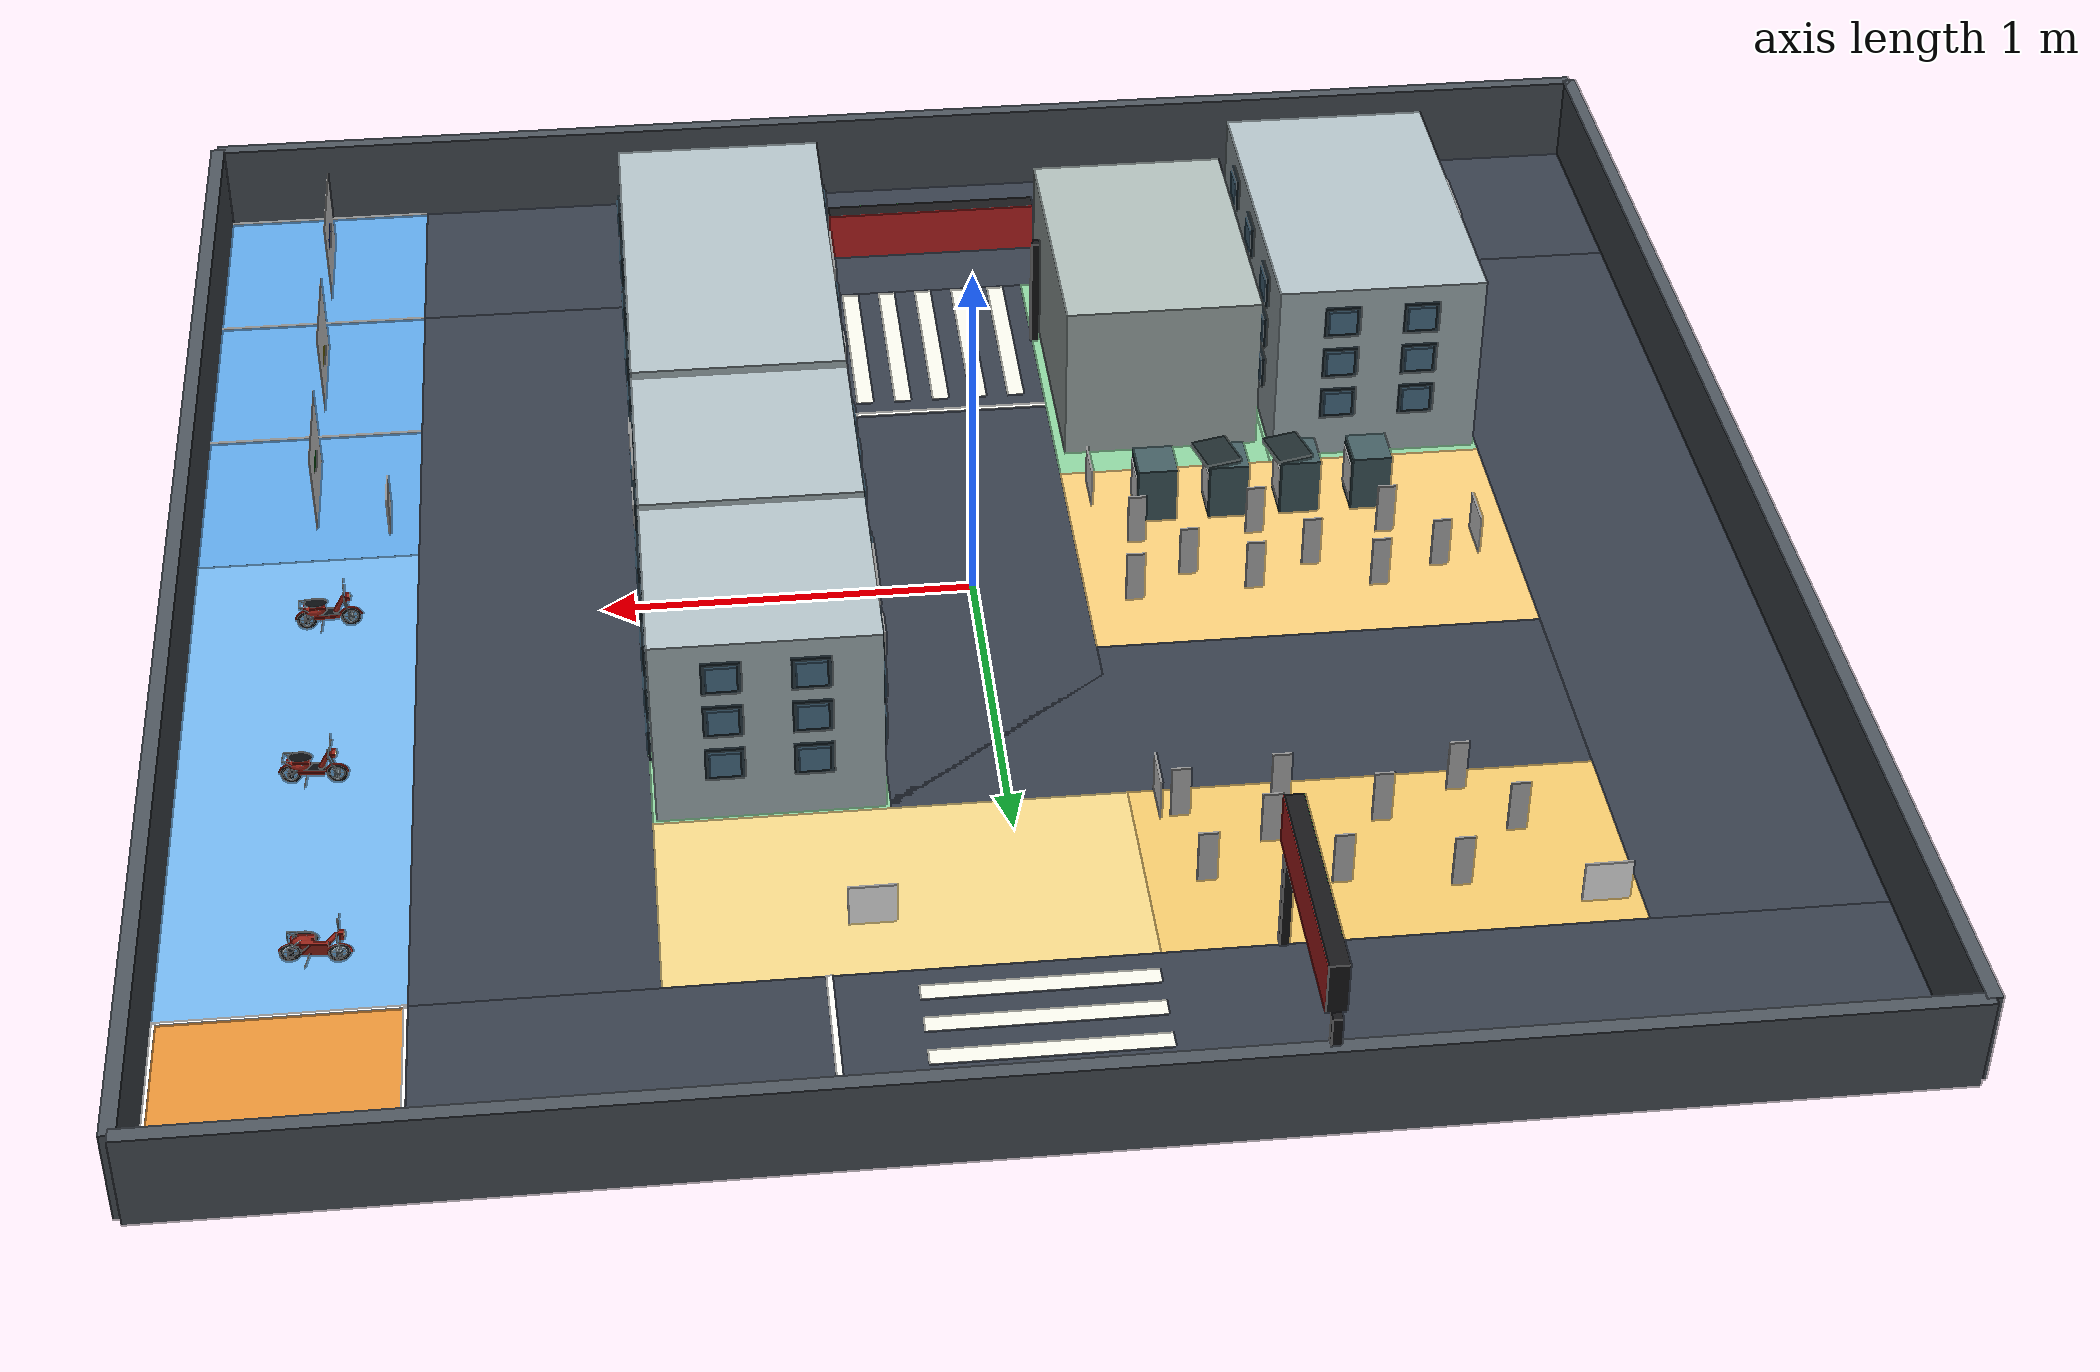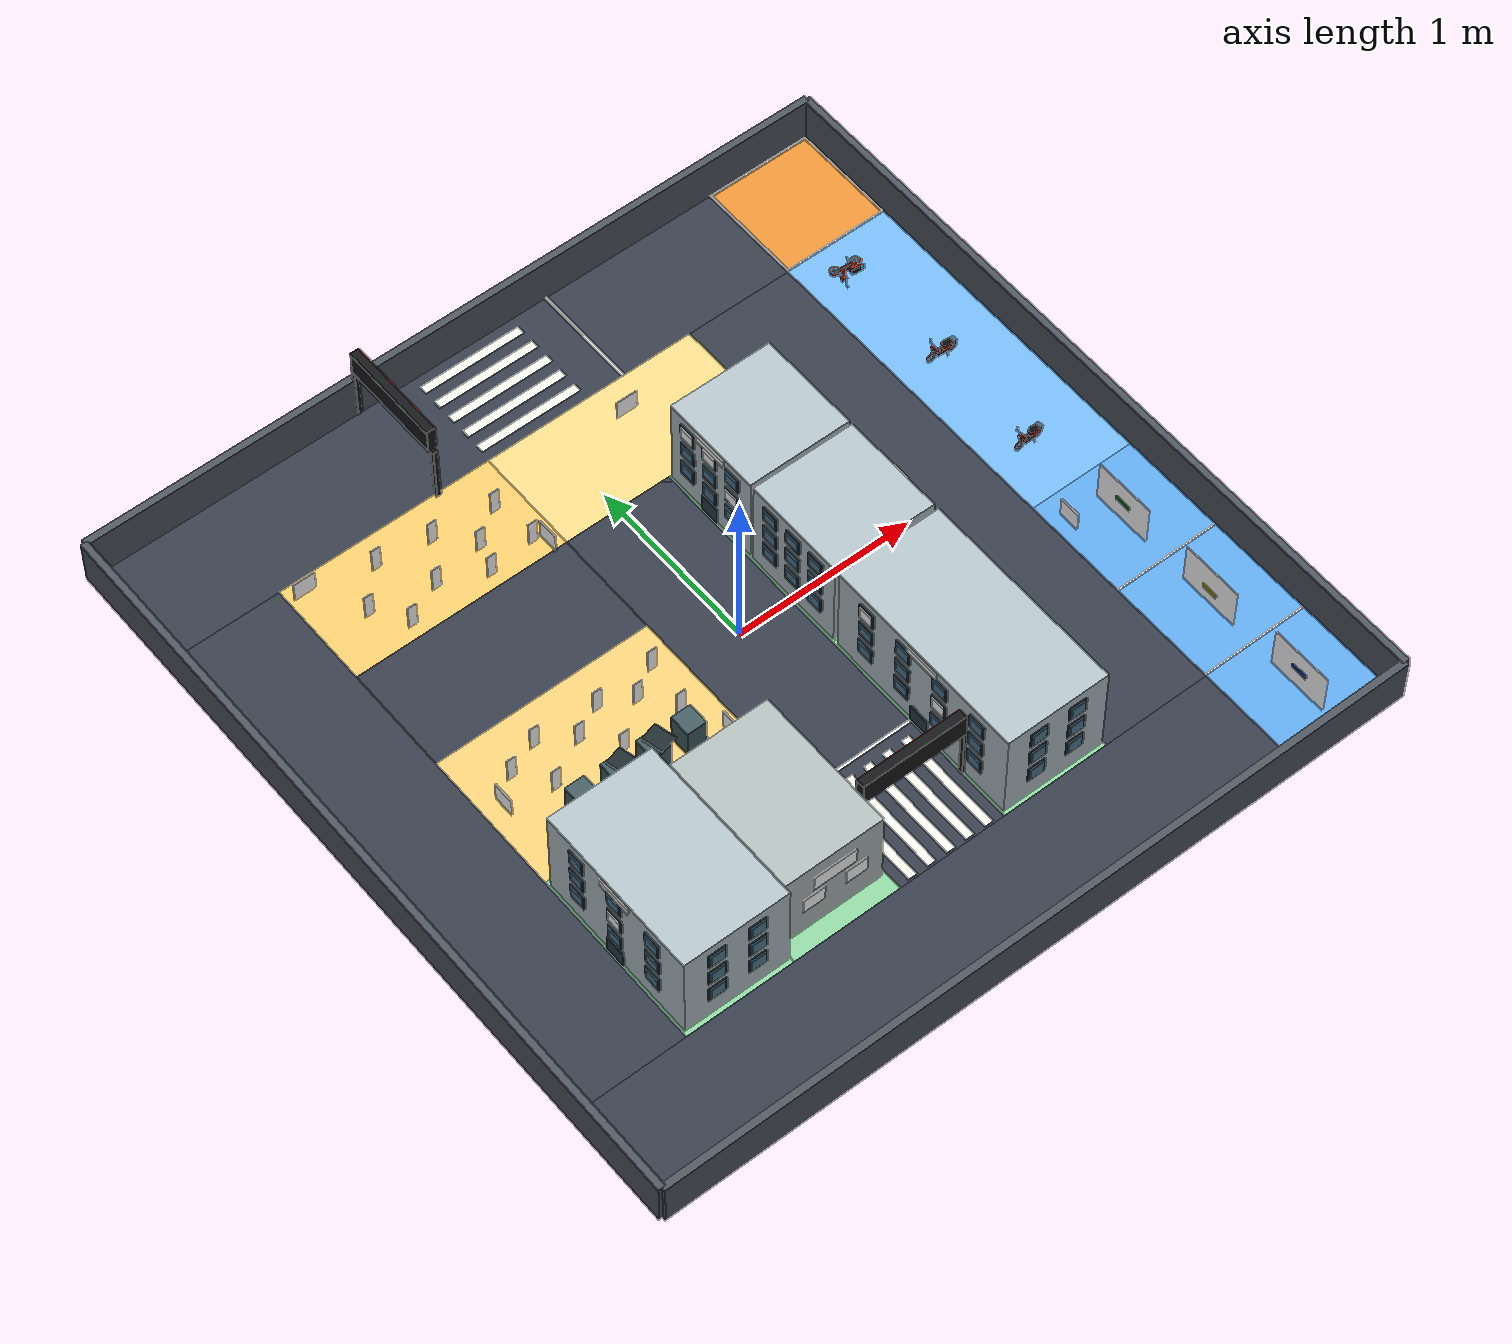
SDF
<sdf version="1.6">
 <world name="sq_community_4p2">
  <include><uri>model://sun</uri></include>
  <gravity>0 0 -9.8</gravity>
  <model name="sq4_floor">
   <static>true</static>
   <link name="floor">
    <visual name="floor_vis">
     <pose>0.0000 0.0000 -0.0150 0 0 0.00000</pose>
     <geometry><box><size>4.2000 4.2000 0.0300</size></box></geometry>
     <material>
      <ambient>0.5300 0.5500 0.5800 1.0000</ambient>
      <diffuse>0.5300 0.5500 0.5800 1.0000</diffuse>
     </material>
    </visual>
    <collision name="floor_col">
     <pose>0.0000 0.0000 -0.0150 0 0 0.00000</pose>
     <geometry><box><size>4.2000 4.2000 0.0300</size></box></geometry>
    </collision>
   </link>
  </model>
  <model name="sq4_road_top">
   <static>true</static>
   <pose>-0.3000 1.8000 0.0000 0 0 0.00000</pose>
   <link name="surface">
    <visual name="surface_vis">
     <pose>0.0000 0.0000 0.0015 0 0 0.00000</pose>
     <geometry><box><size>3.6000 0.6000 0.0030</size></box></geometry>
     <material>
      <ambient>0.2100 0.2400 0.2900 1.0000</ambient>
      <diffuse>0.2100 0.2400 0.2900 1.0000</diffuse>
     </material>
    </visual>
   </link>
  </model>
  <model name="sq4_road_west">
   <static>true</static>
   <pose>-1.8000 0.0000 0.0000 0 0 0.00000</pose>
   <link name="surface">
    <visual name="surface_vis">
     <pose>0.0000 0.0000 0.0015 0 0 0.00000</pose>
     <geometry><box><size>0.6000 3.0000 0.0030</size></box></geometry>
     <material>
      <ambient>0.2100 0.2400 0.2900 1.0000</ambient>
      <diffuse>0.2100 0.2400 0.2900 1.0000</diffuse>
     </material>
    </visual>
   </link>
  </model>
  <model name="sq4_road_connector">
   <static>true</static>
   <pose>-0.6000 0.6000 0.0000 0 0 0.00000</pose>
   <link name="surface">
    <visual name="surface_vis">
     <pose>0.0000 0.0000 0.0015 0 0 0.00000</pose>
     <geometry><box><size>1.8000 0.6000 0.0030</size></box></geometry>
     <material>
      <ambient>0.2100 0.2400 0.2900 1.0000</ambient>
      <diffuse>0.2100 0.2400 0.2900 1.0000</diffuse>
     </material>
    </visual>
   </link>
  </model>
  <model name="sq4_road_central">
   <static>true</static>
   <pose>0.0000 -0.3000 0.0000 0 0 0.00000</pose>
   <link name="surface">
    <visual name="surface_vis">
     <pose>0.0000 0.0000 0.0015 0 0 0.00000</pose>
     <geometry><box><size>0.6000 2.4000 0.0030</size></box></geometry>
     <material>
      <ambient>0.2100 0.2400 0.2900 1.0000</ambient>
      <diffuse>0.2100 0.2400 0.2900 1.0000</diffuse>
     </material>
    </visual>
   </link>
  </model>
  <model name="sq4_road_bottom">
   <static>true</static>
   <pose>-0.3000 -1.8000 0.0000 0 0 0.00000</pose>
   <link name="surface">
    <visual name="surface_vis">
     <pose>0.0000 0.0000 0.0015 0 0 0.00000</pose>
     <geometry><box><size>3.6000 0.6000 0.0030</size></box></geometry>
     <material>
      <ambient>0.2100 0.2400 0.2900 1.0000</ambient>
      <diffuse>0.2100 0.2400 0.2900 1.0000</diffuse>
     </material>
    </visual>
   </link>
  </model>
  <model name="sq4_road_east">
   <static>true</static>
   <pose>1.2000 0.0000 0.0000 0 0 0.00000</pose>
   <link name="surface">
    <visual name="surface_vis">
     <pose>0.0000 0.0000 0.0015 0 0 0.00000</pose>
     <geometry><box><size>0.6000 3.0000 0.0030</size></box></geometry>
     <material>
      <ambient>0.2100 0.2400 0.2900 1.0000</ambient>
      <diffuse>0.2100 0.2400 0.2900 1.0000</diffuse>
     </material>
    </visual>
   </link>
  </model>
  <model name="sq4_zone_start_finish">
   <static>true</static>
   <pose>1.8000 1.8000 0.0000 0 0 0.00000</pose>
   <link name="surface">
    <visual name="surface_vis">
     <pose>0.0000 0.0000 0.0018 0 0 0.00000</pose>
     <geometry><box><size>0.6000 0.6000 0.0035</size></box></geometry>
     <material>
      <ambient>0.9000 0.5700 0.2100 1.0000</ambient>
      <diffuse>0.9000 0.5700 0.2100 1.0000</diffuse>
     </material>
    </visual>
   </link>
  </model>
  <model name="sq4_zone_a_people">
   <static>true</static>
   <pose>-0.9000 1.2000 0.0000 0 0 0.00000</pose>
   <link name="surface">
    <visual name="surface_vis">
     <pose>0.0000 0.0000 0.0018 0 0 0.00000</pose>
     <geometry><box><size>1.2000 0.6000 0.0035</size></box></geometry>
     <material>
      <ambient>0.9400 0.7800 0.4200 1.0000</ambient>
      <diffuse>0.9400 0.7800 0.4200 1.0000</diffuse>
     </material>
    </visual>
   </link>
  </model>
  <model name="sq4_zone_a_street">
   <static>true</static>
   <pose>0.3000 1.2000 0.0000 0 0 0.00000</pose>
   <link name="surface">
    <visual name="surface_vis">
     <pose>0.0000 0.0000 0.0018 0 0 0.00000</pose>
     <geometry><box><size>1.2000 0.6000 0.0035</size></box></geometry>
     <material>
      <ambient>0.9500 0.8400 0.5300 1.0000</ambient>
      <diffuse>0.9500 0.8400 0.5300 1.0000</diffuse>
     </material>
    </visual>
   </link>
  </model>
  <model name="sq4_zone_b_people">
   <static>true</static>
   <pose>-0.9000 -0.1000 0.0000 0 0 0.00000</pose>
   <link name="surface">
    <visual name="surface_vis">
     <pose>0.0000 0.0000 0.0018 0 0 0.00000</pose>
     <geometry><box><size>1.2000 0.8000 0.0035</size></box></geometry>
     <material>
      <ambient>0.9600 0.8000 0.4700 1.0000</ambient>
      <diffuse>0.9600 0.8000 0.4700 1.0000</diffuse>
     </material>
    </visual>
   </link>
  </model>
  <model name="sq4_zone_building_A">
   <static>true</static>
   <pose>0.6000 0.6000 0.0000 0 0 0.00000</pose>
   <link name="surface">
    <visual name="surface_vis">
     <pose>0.0000 0.0000 0.0018 0 0 0.00000</pose>
     <geometry><box><size>0.6000 0.6000 0.0035</size></box></geometry>
     <material>
      <ambient>0.5500 0.8200 0.6200 1.0000</ambient>
      <diffuse>0.5500 0.8200 0.6200 1.0000</diffuse>
     </material>
    </visual>
   </link>
  </model>
  <model name="sq4_zone_building_B">
   <static>true</static>
   <pose>0.6000 0.0000 0.0000 0 0 0.00000</pose>
   <link name="surface">
    <visual name="surface_vis">
     <pose>0.0000 0.0000 0.0018 0 0 0.00000</pose>
     <geometry><box><size>0.6000 0.6000 0.0035</size></box></geometry>
     <material>
      <ambient>0.5500 0.8200 0.6200 1.0000</ambient>
      <diffuse>0.5500 0.8200 0.6200 1.0000</diffuse>
     </material>
    </visual>
   </link>
  </model>
  <model name="sq4_zone_building_C">
   <static>true</static>
   <pose>0.6000 -0.9000 0.0000 0 0 0.00000</pose>
   <link name="surface">
    <visual name="surface_vis">
     <pose>0.0000 0.0000 0.0018 0 0 0.00000</pose>
     <geometry><box><size>0.6000 1.2000 0.0035</size></box></geometry>
     <material>
      <ambient>0.5500 0.8200 0.6200 1.0000</ambient>
      <diffuse>0.5500 0.8200 0.6200 1.0000</diffuse>
     </material>
    </visual>
   </link>
  </model>
  <model name="sq4_zone_building_D">
   <static>true</static>
   <pose>-1.2000 -1.0000 0.0000 0 0 0.00000</pose>
   <link name="surface">
    <visual name="surface_vis">
     <pose>0.0000 0.0000 0.0018 0 0 0.00000</pose>
     <geometry><box><size>0.6000 1.0000 0.0035</size></box></geometry>
     <material>
      <ambient>0.5500 0.8200 0.6200 1.0000</ambient>
      <diffuse>0.5500 0.8200 0.6200 1.0000</diffuse>
     </material>
    </visual>
   </link>
  </model>
  <model name="sq4_zone_station">
   <static>true</static>
   <pose>-0.6000 -1.0000 0.0000 0 0 0.00000</pose>
   <link name="surface">
    <visual name="surface_vis">
     <pose>0.0000 0.0000 0.0018 0 0 0.00000</pose>
     <geometry><box><size>0.6000 1.0000 0.0035</size></box></geometry>
     <material>
      <ambient>0.5500 0.8200 0.6200 1.0000</ambient>
      <diffuse>0.5500 0.8200 0.6200 1.0000</diffuse>
     </material>
    </visual>
   </link>
  </model>
  <model name="sq4_zone_ebike_parking">
   <static>true</static>
   <pose>1.8000 0.6000 0.0000 0 0 0.00000</pose>
   <link name="surface">
    <visual name="surface_vis">
     <pose>0.0000 0.0000 0.0018 0 0 0.00000</pose>
     <geometry><box><size>0.6000 1.8000 0.0035</size></box></geometry>
     <material>
      <ambient>0.4500 0.7100 0.9300 1.0000</ambient>
      <diffuse>0.4500 0.7100 0.9300 1.0000</diffuse>
     </material>
    </visual>
   </link>
  </model>
  <model name="sq4_zone_car_parking">
   <static>true</static>
   <pose>1.8000 -1.2000 0.0000 0 0 0.00000</pose>
   <link name="surface">
    <visual name="surface_vis">
     <pose>0.0000 0.0000 0.0018 0 0 0.00000</pose>
     <geometry><box><size>0.6000 1.8000 0.0035</size></box></geometry>
     <material>
      <ambient>0.4500 0.7100 0.9300 1.0000</ambient>
      <diffuse>0.4500 0.7100 0.9300 1.0000</diffuse>
     </material>
    </visual>
   </link>
  </model>
  <model name="sq4_boundary_north">
   <static>true</static>
   <pose>0.0000 2.1200 0.0000 0 0 0.00000</pose>
   <link name="wall">
    <visual name="wall_vis">
     <pose>0.0000 0.0000 0.1300 0 0 0.00000</pose>
     <geometry><box><size>4.2400 0.0400 0.2600</size></box></geometry>
     <material>
      <ambient>0.3000 0.3300 0.3600 1.0000</ambient>
      <diffuse>0.3000 0.3300 0.3600 1.0000</diffuse>
     </material>
    </visual>
    <collision name="wall_col">
     <pose>0.0000 0.0000 0.1300 0 0 0.00000</pose>
     <geometry><box><size>4.2400 0.0400 0.2600</size></box></geometry>
    </collision>
   </link>
  </model>
  <model name="sq4_boundary_south">
   <static>true</static>
   <pose>0.0000 -2.1200 0.0000 0 0 0.00000</pose>
   <link name="wall">
    <visual name="wall_vis">
     <pose>0.0000 0.0000 0.1300 0 0 0.00000</pose>
     <geometry><box><size>4.2400 0.0400 0.2600</size></box></geometry>
     <material>
      <ambient>0.3000 0.3300 0.3600 1.0000</ambient>
      <diffuse>0.3000 0.3300 0.3600 1.0000</diffuse>
     </material>
    </visual>
    <collision name="wall_col">
     <pose>0.0000 0.0000 0.1300 0 0 0.00000</pose>
     <geometry><box><size>4.2400 0.0400 0.2600</size></box></geometry>
    </collision>
   </link>
  </model>
  <model name="sq4_boundary_west">
   <static>true</static>
   <pose>-2.1200 0.0000 0.0000 0 0 0.00000</pose>
   <link name="wall">
    <visual name="wall_vis">
     <pose>0.0000 0.0000 0.1300 0 0 0.00000</pose>
     <geometry><box><size>0.0400 4.2400 0.2600</size></box></geometry>
     <material>
      <ambient>0.3000 0.3300 0.3600 1.0000</ambient>
      <diffuse>0.3000 0.3300 0.3600 1.0000</diffuse>
     </material>
    </visual>
    <collision name="wall_col">
     <pose>0.0000 0.0000 0.1300 0 0 0.00000</pose>
     <geometry><box><size>0.0400 4.2400 0.2600</size></box></geometry>
    </collision>
   </link>
  </model>
  <model name="sq4_boundary_east">
   <static>true</static>
   <pose>2.1200 0.0000 0.0000 0 0 0.00000</pose>
   <link name="wall">
    <visual name="wall_vis">
     <pose>0.0000 0.0000 0.1300 0 0 0.00000</pose>
     <geometry><box><size>0.0400 4.2400 0.2600</size></box></geometry>
     <material>
      <ambient>0.3000 0.3300 0.3600 1.0000</ambient>
      <diffuse>0.3000 0.3300 0.3600 1.0000</diffuse>
     </material>
    </visual>
    <collision name="wall_col">
     <pose>0.0000 0.0000 0.1300 0 0 0.00000</pose>
     <geometry><box><size>0.0400 4.2400 0.2600</size></box></geometry>
    </collision>
   </link>
  </model>
  <model name="sq4_crossing_upper_0">
   <static>true</static>
   <pose>0.0000 1.5800 0.0000 0 0 0.00000</pose>
   <link name="surface">
    <visual name="surface_vis">
     <pose>0.0000 0.0000 0.0025 0 0 0.00000</pose>
     <geometry><box><size>0.5800 0.0480 0.0050</size></box></geometry>
     <material>
      <ambient>0.9600 0.9600 0.9200 1.0000</ambient>
      <diffuse>0.9600 0.9600 0.9200 1.0000</diffuse>
     </material>
    </visual>
   </link>
  </model>
  <model name="sq4_crossing_upper_1">
   <static>true</static>
   <pose>0.0000 1.6900 0.0000 0 0 0.00000</pose>
   <link name="surface">
    <visual name="surface_vis">
     <pose>0.0000 0.0000 0.0025 0 0 0.00000</pose>
     <geometry><box><size>0.5800 0.0480 0.0050</size></box></geometry>
     <material>
      <ambient>0.9600 0.9600 0.9200 1.0000</ambient>
      <diffuse>0.9600 0.9600 0.9200 1.0000</diffuse>
     </material>
    </visual>
   </link>
  </model>
  <model name="sq4_crossing_upper_2">
   <static>true</static>
   <pose>0.0000 1.8000 0.0000 0 0 0.00000</pose>
   <link name="surface">
    <visual name="surface_vis">
     <pose>0.0000 0.0000 0.0025 0 0 0.00000</pose>
     <geometry><box><size>0.5800 0.0480 0.0050</size></box></geometry>
     <material>
      <ambient>0.9600 0.9600 0.9200 1.0000</ambient>
      <diffuse>0.9600 0.9600 0.9200 1.0000</diffuse>
     </material>
    </visual>
   </link>
  </model>
  <model name="sq4_crossing_upper_3">
   <static>true</static>
   <pose>0.0000 1.9100 0.0000 0 0 0.00000</pose>
   <link name="surface">
    <visual name="surface_vis">
     <pose>0.0000 0.0000 0.0025 0 0 0.00000</pose>
     <geometry><box><size>0.5800 0.0480 0.0050</size></box></geometry>
     <material>
      <ambient>0.9600 0.9600 0.9200 1.0000</ambient>
      <diffuse>0.9600 0.9600 0.9200 1.0000</diffuse>
     </material>
    </visual>
   </link>
  </model>
  <model name="sq4_crossing_upper_4">
   <static>true</static>
   <pose>0.0000 2.0200 0.0000 0 0 0.00000</pose>
   <link name="surface">
    <visual name="surface_vis">
     <pose>0.0000 0.0000 0.0025 0 0 0.00000</pose>
     <geometry><box><size>0.5800 0.0480 0.0050</size></box></geometry>
     <material>
      <ambient>0.9600 0.9600 0.9200 1.0000</ambient>
      <diffuse>0.9600 0.9600 0.9200 1.0000</diffuse>
     </material>
    </visual>
   </link>
  </model>
  <model name="sq4_crossing_lower_0">
   <static>true</static>
   <pose>-0.2200 -1.2000 0.0000 0 0 0.00000</pose>
   <link name="surface">
    <visual name="surface_vis">
     <pose>0.0000 0.0000 0.0025 0 0 0.00000</pose>
     <geometry><box><size>0.0480 0.5800 0.0050</size></box></geometry>
     <material>
      <ambient>0.9600 0.9600 0.9200 1.0000</ambient>
      <diffuse>0.9600 0.9600 0.9200 1.0000</diffuse>
     </material>
    </visual>
   </link>
  </model>
  <model name="sq4_crossing_lower_1">
   <static>true</static>
   <pose>-0.1100 -1.2000 0.0000 0 0 0.00000</pose>
   <link name="surface">
    <visual name="surface_vis">
     <pose>0.0000 0.0000 0.0025 0 0 0.00000</pose>
     <geometry><box><size>0.0480 0.5800 0.0050</size></box></geometry>
     <material>
      <ambient>0.9600 0.9600 0.9200 1.0000</ambient>
      <diffuse>0.9600 0.9600 0.9200 1.0000</diffuse>
     </material>
    </visual>
   </link>
  </model>
  <model name="sq4_crossing_lower_2">
   <static>true</static>
   <pose>0.0000 -1.2000 0.0000 0 0 0.00000</pose>
   <link name="surface">
    <visual name="surface_vis">
     <pose>0.0000 0.0000 0.0025 0 0 0.00000</pose>
     <geometry><box><size>0.0480 0.5800 0.0050</size></box></geometry>
     <material>
      <ambient>0.9600 0.9600 0.9200 1.0000</ambient>
      <diffuse>0.9600 0.9600 0.9200 1.0000</diffuse>
     </material>
    </visual>
   </link>
  </model>
  <model name="sq4_crossing_lower_3">
   <static>true</static>
   <pose>0.1100 -1.2000 0.0000 0 0 0.00000</pose>
   <link name="surface">
    <visual name="surface_vis">
     <pose>0.0000 0.0000 0.0025 0 0 0.00000</pose>
     <geometry><box><size>0.0480 0.5800 0.0050</size></box></geometry>
     <material>
      <ambient>0.9600 0.9600 0.9200 1.0000</ambient>
      <diffuse>0.9600 0.9600 0.9200 1.0000</diffuse>
     </material>
    </visual>
   </link>
  </model>
  <model name="sq4_crossing_lower_4">
   <static>true</static>
   <pose>0.2200 -1.2000 0.0000 0 0 0.00000</pose>
   <link name="surface">
    <visual name="surface_vis">
     <pose>0.0000 0.0000 0.0025 0 0 0.00000</pose>
     <geometry><box><size>0.0480 0.5800 0.0050</size></box></geometry>
     <material>
      <ambient>0.9600 0.9600 0.9200 1.0000</ambient>
      <diffuse>0.9600 0.9600 0.9200 1.0000</diffuse>
     </material>
    </visual>
   </link>
  </model>
  <model name="sq4_stop_upper">
   <static>true</static>
   <pose>0.5000 1.8000 0.0000 0 0 0.00000</pose>
   <link name="surface">
    <visual name="surface_vis">
     <pose>0.0000 0.0000 0.0030 0 0 0.00000</pose>
     <geometry><box><size>0.0160 0.6000 0.0060</size></box></geometry>
     <material>
      <ambient>0.9800 0.9800 0.9600 1.0000</ambient>
      <diffuse>0.9800 0.9800 0.9600 1.0000</diffuse>
     </material>
    </visual>
   </link>
  </model>
  <model name="sq4_stop_lower">
   <static>true</static>
   <pose>0.0000 -0.8500 0.0000 0 0 0.00000</pose>
   <link name="surface">
    <visual name="surface_vis">
     <pose>0.0000 0.0000 0.0030 0 0 0.00000</pose>
     <geometry><box><size>0.6000 0.0160 0.0060</size></box></geometry>
     <material>
      <ambient>0.9800 0.9800 0.9600 1.0000</ambient>
      <diffuse>0.9800 0.9800 0.9600 1.0000</diffuse>
     </material>
    </visual>
   </link>
  </model>
  <model name="sq4_start_outline_0">
   <static>true</static>
   <pose>1.8000 1.5050 0.0000 0 0 0.00000</pose>
   <link name="surface">
    <visual name="surface_vis">
     <pose>0.0000 0.0000 0.0035 0 0 0.00000</pose>
     <geometry><box><size>0.6000 0.0100 0.0070</size></box></geometry>
     <material>
      <ambient>0.9900 0.9900 0.9900 1.0000</ambient>
      <diffuse>0.9900 0.9900 0.9900 1.0000</diffuse>
     </material>
    </visual>
   </link>
  </model>
  <model name="sq4_start_outline_1">
   <static>true</static>
   <pose>1.8000 2.0950 0.0000 0 0 0.00000</pose>
   <link name="surface">
    <visual name="surface_vis">
     <pose>0.0000 0.0000 0.0035 0 0 0.00000</pose>
     <geometry><box><size>0.6000 0.0100 0.0070</size></box></geometry>
     <material>
      <ambient>0.9900 0.9900 0.9900 1.0000</ambient>
      <diffuse>0.9900 0.9900 0.9900 1.0000</diffuse>
     </material>
    </visual>
   </link>
  </model>
  <model name="sq4_start_outline_2">
   <static>true</static>
   <pose>1.5050 1.8000 0.0000 0 0 0.00000</pose>
   <link name="surface">
    <visual name="surface_vis">
     <pose>0.0000 0.0000 0.0035 0 0 0.00000</pose>
     <geometry><box><size>0.0100 0.6000 0.0070</size></box></geometry>
     <material>
      <ambient>0.9900 0.9900 0.9900 1.0000</ambient>
      <diffuse>0.9900 0.9900 0.9900 1.0000</diffuse>
     </material>
    </visual>
   </link>
  </model>
  <model name="sq4_start_outline_3">
   <static>true</static>
   <pose>2.0950 1.8000 0.0000 0 0 0.00000</pose>
   <link name="surface">
    <visual name="surface_vis">
     <pose>0.0000 0.0000 0.0035 0 0 0.00000</pose>
     <geometry><box><size>0.0100 0.6000 0.0070</size></box></geometry>
     <material>
      <ambient>0.9900 0.9900 0.9900 1.0000</ambient>
      <diffuse>0.9900 0.9900 0.9900 1.0000</diffuse>
     </material>
    </visual>
   </link>
  </model>
  <model name="sq4_car_bay_1">
   <static>true</static>
   <pose>1.8000 -1.8000 0.0000 0 0 0.00000</pose>
   <link name="surface">
    <visual name="surface_vis">
     <pose>0.0000 0.0000 0.0020 0 0 0.00000</pose>
     <geometry><box><size>0.6000 0.6000 0.0040</size></box></geometry>
     <material>
      <ambient>0.3700 0.6500 0.9000 1.0000</ambient>
      <diffuse>0.3700 0.6500 0.9000 1.0000</diffuse>
     </material>
    </visual>
   </link>
  </model>
  <model name="sq4_car_bay_line_1">
   <static>true</static>
   <pose>1.8000 -2.0950 0.0000 0 0 0.00000</pose>
   <link name="surface">
    <visual name="surface_vis">
     <pose>0.0000 0.0000 0.0030 0 0 0.00000</pose>
     <geometry><box><size>0.6000 0.0100 0.0060</size></box></geometry>
     <material>
      <ambient>0.9600 0.9700 0.9700 1.0000</ambient>
      <diffuse>0.9600 0.9700 0.9700 1.0000</diffuse>
     </material>
    </visual>
   </link>
  </model>
  <model name="sq4_car_bay_2">
   <static>true</static>
   <pose>1.8000 -1.2000 0.0000 0 0 0.00000</pose>
   <link name="surface">
    <visual name="surface_vis">
     <pose>0.0000 0.0000 0.0020 0 0 0.00000</pose>
     <geometry><box><size>0.6000 0.6000 0.0040</size></box></geometry>
     <material>
      <ambient>0.3700 0.6500 0.9000 1.0000</ambient>
      <diffuse>0.3700 0.6500 0.9000 1.0000</diffuse>
     </material>
    </visual>
   </link>
  </model>
  <model name="sq4_car_bay_line_2">
   <static>true</static>
   <pose>1.8000 -1.4950 0.0000 0 0 0.00000</pose>
   <link name="surface">
    <visual name="surface_vis">
     <pose>0.0000 0.0000 0.0030 0 0 0.00000</pose>
     <geometry><box><size>0.6000 0.0100 0.0060</size></box></geometry>
     <material>
      <ambient>0.9600 0.9700 0.9700 1.0000</ambient>
      <diffuse>0.9600 0.9700 0.9700 1.0000</diffuse>
     </material>
    </visual>
   </link>
  </model>
  <model name="sq4_car_bay_3">
   <static>true</static>
   <pose>1.8000 -0.6000 0.0000 0 0 0.00000</pose>
   <link name="surface">
    <visual name="surface_vis">
     <pose>0.0000 0.0000 0.0020 0 0 0.00000</pose>
     <geometry><box><size>0.6000 0.6000 0.0040</size></box></geometry>
     <material>
      <ambient>0.3700 0.6500 0.9000 1.0000</ambient>
      <diffuse>0.3700 0.6500 0.9000 1.0000</diffuse>
     </material>
    </visual>
   </link>
  </model>
  <model name="sq4_car_bay_line_3">
   <static>true</static>
   <pose>1.8000 -0.8950 0.0000 0 0 0.00000</pose>
   <link name="surface">
    <visual name="surface_vis">
     <pose>0.0000 0.0000 0.0030 0 0 0.00000</pose>
     <geometry><box><size>0.6000 0.0100 0.0060</size></box></geometry>
     <material>
      <ambient>0.9600 0.9700 0.9700 1.0000</ambient>
      <diffuse>0.9600 0.9700 0.9700 1.0000</diffuse>
     </material>
    </visual>
   </link>
  </model>
  <model name="sq4_person_01">
   <static>true</static>
   <pose>-1.25000 1.14000 .004 0 0 1.57079633</pose>
   <link name="panel">
    <visual name="backing">
     <pose>-.0001 0 .075 0 0 0</pose>
     <geometry><box><size>.0048 .05 .15</size></box></geometry>
     <material>
      <lighting>false</lighting>
      <ambient>1 1 1 1</ambient>
      <diffuse>1 1 1 1</diffuse>
      <emissive>1 1 1 1</emissive>
     </material>
    </visual>
    <visual name="portrait">
     <pose>.0024 0 .075 0 0 0</pose>
     <geometry><box><size>.0002 .05 .15</size></box></geometry>
     <material>
      <script>
       <uri>model://sq_competition_assets/materials/scripts</uri>
       <uri>model://sq_competition_assets/materials/textures</uri>
       <name>SQ4_Person_01</name>
      </script>
     </material>
    </visual>
    <collision name="panel_collision">
     <pose>0 0 .075 0 0 0</pose>
     <geometry><box><size>.005 .05 .15</size></box></geometry>
    </collision>
   </link>
  </model>
  <model name="sq4_person_02">
   <static>true</static>
   <pose>-1.07000 1.33000 .004 0 0 1.57079633</pose>
   <link name="panel">
    <visual name="backing">
     <pose>-.0001 0 .075 0 0 0</pose>
     <geometry><box><size>.0048 .05 .15</size></box></geometry>
     <material>
      <lighting>false</lighting>
      <ambient>1 1 1 1</ambient>
      <diffuse>1 1 1 1</diffuse>
      <emissive>1 1 1 1</emissive>
     </material>
    </visual>
    <visual name="portrait">
     <pose>.0024 0 .075 0 0 0</pose>
     <geometry><box><size>.0002 .05 .15</size></box></geometry>
     <material>
      <script>
       <uri>model://sq_competition_assets/materials/scripts</uri>
       <uri>model://sq_competition_assets/materials/textures</uri>
       <name>SQ4_Person_02</name>
      </script>
     </material>
    </visual>
    <collision name="panel_collision">
     <pose>0 0 .075 0 0 0</pose>
     <geometry><box><size>.005 .05 .15</size></box></geometry>
    </collision>
   </link>
  </model>
  <model name="sq4_person_03">
   <static>true</static>
   <pose>-0.92000 1.07000 .004 0 0 1.57079633</pose>
   <link name="panel">
    <visual name="backing">
     <pose>-.0001 0 .075 0 0 0</pose>
     <geometry><box><size>.0048 .05 .15</size></box></geometry>
     <material>
      <lighting>false</lighting>
      <ambient>1 1 1 1</ambient>
      <diffuse>1 1 1 1</diffuse>
      <emissive>1 1 1 1</emissive>
     </material>
    </visual>
    <visual name="portrait">
     <pose>.0024 0 .075 0 0 0</pose>
     <geometry><box><size>.0002 .05 .15</size></box></geometry>
     <material>
      <script>
       <uri>model://sq_competition_assets/materials/scripts</uri>
       <uri>model://sq_competition_assets/materials/textures</uri>
       <name>SQ4_Person_03</name>
      </script>
     </material>
    </visual>
    <collision name="panel_collision">
     <pose>0 0 .075 0 0 0</pose>
     <geometry><box><size>.005 .05 .15</size></box></geometry>
    </collision>
   </link>
  </model>
  <model name="sq4_person_04">
   <static>true</static>
   <pose>-0.78000 1.29000 .004 0 0 1.57079633</pose>
   <link name="panel">
    <visual name="backing">
     <pose>-.0001 0 .075 0 0 0</pose>
     <geometry><box><size>.0048 .05 .15</size></box></geometry>
     <material>
      <lighting>false</lighting>
      <ambient>1 1 1 1</ambient>
      <diffuse>1 1 1 1</diffuse>
      <emissive>1 1 1 1</emissive>
     </material>
    </visual>
    <visual name="portrait">
     <pose>.0024 0 .075 0 0 0</pose>
     <geometry><box><size>.0002 .05 .15</size></box></geometry>
     <material>
      <script>
       <uri>model://sq_competition_assets/materials/scripts</uri>
       <uri>model://sq_competition_assets/materials/textures</uri>
       <name>SQ4_Person_04</name>
      </script>
     </material>
    </visual>
    <collision name="panel_collision">
     <pose>0 0 .075 0 0 0</pose>
     <geometry><box><size>.005 .05 .15</size></box></geometry>
    </collision>
   </link>
  </model>
  <model name="sq4_person_05">
   <static>true</static>
   <pose>-0.63000 1.12000 .004 0 0 1.57079633</pose>
   <link name="panel">
    <visual name="backing">
     <pose>-.0001 0 .075 0 0 0</pose>
     <geometry><box><size>.0048 .05 .15</size></box></geometry>
     <material>
      <lighting>false</lighting>
      <ambient>1 1 1 1</ambient>
      <diffuse>1 1 1 1</diffuse>
      <emissive>1 1 1 1</emissive>
     </material>
    </visual>
    <visual name="portrait">
     <pose>.0024 0 .075 0 0 0</pose>
     <geometry><box><size>.0002 .05 .15</size></box></geometry>
     <material>
      <script>
       <uri>model://sq_competition_assets/materials/scripts</uri>
       <uri>model://sq_competition_assets/materials/textures</uri>
       <name>SQ4_Person_05</name>
      </script>
     </material>
    </visual>
    <collision name="panel_collision">
     <pose>0 0 .075 0 0 0</pose>
     <geometry><box><size>.005 .05 .15</size></box></geometry>
    </collision>
   </link>
  </model>
  <model name="sq4_person_06">
   <static>true</static>
   <pose>-0.45000 1.25000 .004 0 0 1.57079633</pose>
   <link name="panel">
    <visual name="backing">
     <pose>-.0001 0 .075 0 0 0</pose>
     <geometry><box><size>.0048 .05 .15</size></box></geometry>
     <material>
      <lighting>false</lighting>
      <ambient>1 1 1 1</ambient>
      <diffuse>1 1 1 1</diffuse>
      <emissive>1 1 1 1</emissive>
     </material>
    </visual>
    <visual name="portrait">
     <pose>.0024 0 .075 0 0 0</pose>
     <geometry><box><size>.0002 .05 .15</size></box></geometry>
     <material>
      <script>
       <uri>model://sq_competition_assets/materials/scripts</uri>
       <uri>model://sq_competition_assets/materials/textures</uri>
       <name>SQ4_Person_06</name>
      </script>
     </material>
    </visual>
    <collision name="panel_collision">
     <pose>0 0 .075 0 0 0</pose>
     <geometry><box><size>.005 .05 .15</size></box></geometry>
    </collision>
   </link>
  </model>
  <model name="sq4_person_07">
   <static>true</static>
   <pose>-1.13000 0.97000 .004 0 0 1.57079633</pose>
   <link name="panel">
    <visual name="backing">
     <pose>-.0001 0 .075 0 0 0</pose>
     <geometry><box><size>.0048 .05 .15</size></box></geometry>
     <material>
      <lighting>false</lighting>
      <ambient>1 1 1 1</ambient>
      <diffuse>1 1 1 1</diffuse>
      <emissive>1 1 1 1</emissive>
     </material>
    </visual>
    <visual name="portrait">
     <pose>.0024 0 .075 0 0 0</pose>
     <geometry><box><size>.0002 .05 .15</size></box></geometry>
     <material>
      <script>
       <uri>model://sq_competition_assets/materials/scripts</uri>
       <uri>model://sq_competition_assets/materials/textures</uri>
       <name>SQ4_Person_07</name>
      </script>
     </material>
    </visual>
    <collision name="panel_collision">
     <pose>0 0 .075 0 0 0</pose>
     <geometry><box><size>.005 .05 .15</size></box></geometry>
    </collision>
   </link>
  </model>
  <model name="sq4_person_08">
   <static>true</static>
   <pose>-0.68000 0.97000 .004 0 0 1.57079633</pose>
   <link name="panel">
    <visual name="backing">
     <pose>-.0001 0 .075 0 0 0</pose>
     <geometry><box><size>.0048 .05 .15</size></box></geometry>
     <material>
      <lighting>false</lighting>
      <ambient>1 1 1 1</ambient>
      <diffuse>1 1 1 1</diffuse>
      <emissive>1 1 1 1</emissive>
     </material>
    </visual>
    <visual name="portrait">
     <pose>.0024 0 .075 0 0 0</pose>
     <geometry><box><size>.0002 .05 .15</size></box></geometry>
     <material>
      <script>
       <uri>model://sq_competition_assets/materials/scripts</uri>
       <uri>model://sq_competition_assets/materials/textures</uri>
       <name>SQ4_Person_08</name>
      </script>
     </material>
    </visual>
    <collision name="panel_collision">
     <pose>0 0 .075 0 0 0</pose>
     <geometry><box><size>.005 .05 .15</size></box></geometry>
    </collision>
   </link>
  </model>
  <model name="sq4_person_09">
   <static>true</static>
   <pose>-0.42000 1.00000 .004 0 0 1.57079633</pose>
   <link name="panel">
    <visual name="backing">
     <pose>-.0001 0 .075 0 0 0</pose>
     <geometry><box><size>.0048 .05 .15</size></box></geometry>
     <material>
      <lighting>false</lighting>
      <ambient>1 1 1 1</ambient>
      <diffuse>1 1 1 1</diffuse>
      <emissive>1 1 1 1</emissive>
     </material>
    </visual>
    <visual name="portrait">
     <pose>.0024 0 .075 0 0 0</pose>
     <geometry><box><size>.0002 .05 .15</size></box></geometry>
     <material>
      <script>
       <uri>model://sq_competition_assets/materials/scripts</uri>
       <uri>model://sq_competition_assets/materials/textures</uri>
       <name>SQ4_Person_09</name>
      </script>
     </material>
    </visual>
    <collision name="panel_collision">
     <pose>0 0 .075 0 0 0</pose>
     <geometry><box><size>.005 .05 .15</size></box></geometry>
    </collision>
   </link>
  </model>
  <model name="sq4_person_10">
   <static>true</static>
   <pose>-1.28000 0.03000 .004 0 0 1.57079633</pose>
   <link name="panel">
    <visual name="backing">
     <pose>-.0001 0 .075 0 0 0</pose>
     <geometry><box><size>.0048 .05 .15</size></box></geometry>
     <material>
      <lighting>false</lighting>
      <ambient>1 1 1 1</ambient>
      <diffuse>1 1 1 1</diffuse>
      <emissive>1 1 1 1</emissive>
     </material>
    </visual>
    <visual name="portrait">
     <pose>.0024 0 .075 0 0 0</pose>
     <geometry><box><size>.0002 .05 .15</size></box></geometry>
     <material>
      <script>
       <uri>model://sq_competition_assets/materials/scripts</uri>
       <uri>model://sq_competition_assets/materials/textures</uri>
       <name>SQ4_Person_10</name>
      </script>
     </material>
    </visual>
    <collision name="panel_collision">
     <pose>0 0 .075 0 0 0</pose>
     <geometry><box><size>.005 .05 .15</size></box></geometry>
    </collision>
   </link>
  </model>
  <model name="sq4_person_11">
   <static>true</static>
   <pose>-1.10000 0.10000 .004 0 0 1.57079633</pose>
   <link name="panel">
    <visual name="backing">
     <pose>-.0001 0 .075 0 0 0</pose>
     <geometry><box><size>.0048 .05 .15</size></box></geometry>
     <material>
      <lighting>false</lighting>
      <ambient>1 1 1 1</ambient>
      <diffuse>1 1 1 1</diffuse>
      <emissive>1 1 1 1</emissive>
     </material>
    </visual>
    <visual name="portrait">
     <pose>.0024 0 .075 0 0 0</pose>
     <geometry><box><size>.0002 .05 .15</size></box></geometry>
     <material>
      <script>
       <uri>model://sq_competition_assets/materials/scripts</uri>
       <uri>model://sq_competition_assets/materials/textures</uri>
       <name>SQ4_Person_11</name>
      </script>
     </material>
    </visual>
    <collision name="panel_collision">
     <pose>0 0 .075 0 0 0</pose>
     <geometry><box><size>.005 .05 .15</size></box></geometry>
    </collision>
   </link>
  </model>
  <model name="sq4_person_12">
   <static>true</static>
   <pose>-0.93000 -0.01000 .004 0 0 1.57079633</pose>
   <link name="panel">
    <visual name="backing">
     <pose>-.0001 0 .075 0 0 0</pose>
     <geometry><box><size>.0048 .05 .15</size></box></geometry>
     <material>
      <lighting>false</lighting>
      <ambient>1 1 1 1</ambient>
      <diffuse>1 1 1 1</diffuse>
      <emissive>1 1 1 1</emissive>
     </material>
    </visual>
    <visual name="portrait">
     <pose>.0024 0 .075 0 0 0</pose>
     <geometry><box><size>.0002 .05 .15</size></box></geometry>
     <material>
      <script>
       <uri>model://sq_competition_assets/materials/scripts</uri>
       <uri>model://sq_competition_assets/materials/textures</uri>
       <name>SQ4_Person_12</name>
      </script>
     </material>
    </visual>
    <collision name="panel_collision">
     <pose>0 0 .075 0 0 0</pose>
     <geometry><box><size>.005 .05 .15</size></box></geometry>
    </collision>
   </link>
  </model>
  <model name="sq4_person_13">
   <static>true</static>
   <pose>-0.76000 0.08000 .004 0 0 1.57079633</pose>
   <link name="panel">
    <visual name="backing">
     <pose>-.0001 0 .075 0 0 0</pose>
     <geometry><box><size>.0048 .05 .15</size></box></geometry>
     <material>
      <lighting>false</lighting>
      <ambient>1 1 1 1</ambient>
      <diffuse>1 1 1 1</diffuse>
      <emissive>1 1 1 1</emissive>
     </material>
    </visual>
    <visual name="portrait">
     <pose>.0024 0 .075 0 0 0</pose>
     <geometry><box><size>.0002 .05 .15</size></box></geometry>
     <material>
      <script>
       <uri>model://sq_competition_assets/materials/scripts</uri>
       <uri>model://sq_competition_assets/materials/textures</uri>
       <name>SQ4_Person_13</name>
      </script>
     </material>
    </visual>
    <collision name="panel_collision">
     <pose>0 0 .075 0 0 0</pose>
     <geometry><box><size>.005 .05 .15</size></box></geometry>
    </collision>
   </link>
  </model>
  <model name="sq4_person_14">
   <static>true</static>
   <pose>-0.59000 0.00000 .004 0 0 1.57079633</pose>
   <link name="panel">
    <visual name="backing">
     <pose>-.0001 0 .075 0 0 0</pose>
     <geometry><box><size>.0048 .05 .15</size></box></geometry>
     <material>
      <lighting>false</lighting>
      <ambient>1 1 1 1</ambient>
      <diffuse>1 1 1 1</diffuse>
      <emissive>1 1 1 1</emissive>
     </material>
    </visual>
    <visual name="portrait">
     <pose>.0024 0 .075 0 0 0</pose>
     <geometry><box><size>.0002 .05 .15</size></box></geometry>
     <material>
      <script>
       <uri>model://sq_competition_assets/materials/scripts</uri>
       <uri>model://sq_competition_assets/materials/textures</uri>
       <name>SQ4_Person_14</name>
      </script>
     </material>
    </visual>
    <collision name="panel_collision">
     <pose>0 0 .075 0 0 0</pose>
     <geometry><box><size>.005 .05 .15</size></box></geometry>
    </collision>
   </link>
  </model>
  <model name="sq4_person_15">
   <static>true</static>
   <pose>-0.43000 0.10000 .004 0 0 1.57079633</pose>
   <link name="panel">
    <visual name="backing">
     <pose>-.0001 0 .075 0 0 0</pose>
     <geometry><box><size>.0048 .05 .15</size></box></geometry>
     <material>
      <lighting>false</lighting>
      <ambient>1 1 1 1</ambient>
      <diffuse>1 1 1 1</diffuse>
      <emissive>1 1 1 1</emissive>
     </material>
    </visual>
    <visual name="portrait">
     <pose>.0024 0 .075 0 0 0</pose>
     <geometry><box><size>.0002 .05 .15</size></box></geometry>
     <material>
      <script>
       <uri>model://sq_competition_assets/materials/scripts</uri>
       <uri>model://sq_competition_assets/materials/textures</uri>
       <name>SQ4_Person_15</name>
      </script>
     </material>
    </visual>
    <collision name="panel_collision">
     <pose>0 0 .075 0 0 0</pose>
     <geometry><box><size>.005 .05 .15</size></box></geometry>
    </collision>
   </link>
  </model>
  <model name="sq4_person_16">
   <static>true</static>
   <pose>-1.16000 -0.14000 .004 0 0 1.57079633</pose>
   <link name="panel">
    <visual name="backing">
     <pose>-.0001 0 .075 0 0 0</pose>
     <geometry><box><size>.0048 .05 .15</size></box></geometry>
     <material>
      <lighting>false</lighting>
      <ambient>1 1 1 1</ambient>
      <diffuse>1 1 1 1</diffuse>
      <emissive>1 1 1 1</emissive>
     </material>
    </visual>
    <visual name="portrait">
     <pose>.0024 0 .075 0 0 0</pose>
     <geometry><box><size>.0002 .05 .15</size></box></geometry>
     <material>
      <script>
       <uri>model://sq_competition_assets/materials/scripts</uri>
       <uri>model://sq_competition_assets/materials/textures</uri>
       <name>SQ4_Person_16</name>
      </script>
     </material>
    </visual>
    <collision name="panel_collision">
     <pose>0 0 .075 0 0 0</pose>
     <geometry><box><size>.005 .05 .15</size></box></geometry>
    </collision>
   </link>
  </model>
  <model name="sq4_person_17">
   <static>true</static>
   <pose>-0.80000 -0.17000 .004 0 0 1.57079633</pose>
   <link name="panel">
    <visual name="backing">
     <pose>-.0001 0 .075 0 0 0</pose>
     <geometry><box><size>.0048 .05 .15</size></box></geometry>
     <material>
      <lighting>false</lighting>
      <ambient>1 1 1 1</ambient>
      <diffuse>1 1 1 1</diffuse>
      <emissive>1 1 1 1</emissive>
     </material>
    </visual>
    <visual name="portrait">
     <pose>.0024 0 .075 0 0 0</pose>
     <geometry><box><size>.0002 .05 .15</size></box></geometry>
     <material>
      <script>
       <uri>model://sq_competition_assets/materials/scripts</uri>
       <uri>model://sq_competition_assets/materials/textures</uri>
       <name>SQ4_Person_17</name>
      </script>
     </material>
    </visual>
    <collision name="panel_collision">
     <pose>0 0 .075 0 0 0</pose>
     <geometry><box><size>.005 .05 .15</size></box></geometry>
    </collision>
   </link>
  </model>
  <model name="sq4_person_18">
   <static>true</static>
   <pose>-0.47000 -0.16000 .004 0 0 1.57079633</pose>
   <link name="panel">
    <visual name="backing">
     <pose>-.0001 0 .075 0 0 0</pose>
     <geometry><box><size>.0048 .05 .15</size></box></geometry>
     <material>
      <lighting>false</lighting>
      <ambient>1 1 1 1</ambient>
      <diffuse>1 1 1 1</diffuse>
      <emissive>1 1 1 1</emissive>
     </material>
    </visual>
    <visual name="portrait">
     <pose>.0024 0 .075 0 0 0</pose>
     <geometry><box><size>.0002 .05 .15</size></box></geometry>
     <material>
      <script>
       <uri>model://sq_competition_assets/materials/scripts</uri>
       <uri>model://sq_competition_assets/materials/textures</uri>
       <name>SQ4_Person_18</name>
      </script>
     </material>
    </visual>
    <collision name="panel_collision">
     <pose>0 0 .075 0 0 0</pose>
     <geometry><box><size>.005 .05 .15</size></box></geometry>
    </collision>
   </link>
  </model>
  <model name="sq4_building_A">
   <static>true</static>
   <pose>0.6000 0.6000 0.0000 0 0 0.00000</pose>
   <link name="structure">
    <visual name="structure_vis">
     <pose>0.0000 0.0000 0.2750 0 0 0.00000</pose>
     <geometry><box><size>0.5800 0.5800 0.5500</size></box></geometry>
     <material>
      <ambient>0.6900 0.7500 0.7700 1.0000</ambient>
      <diffuse>0.6900 0.7500 0.7700 1.0000</diffuse>
     </material>
    </visual>
    <collision name="structure_col">
     <pose>0.0000 0.0000 0.2750 0 0 0.00000</pose>
     <geometry><box><size>0.5800 0.5800 0.5500</size></box></geometry>
    </collision>
   </link>
   <link name="nameplate">
    <visual name="nameplate_vis">
     <pose>-0.2960 0.0000 0.5150 0 0 0.00000</pose>
     <geometry><box><size>0.0050 0.2000 0.0450</size></box></geometry>
     <material>
      <script>
       <uri>model://sq_textures/materials/scripts</uri>
       <uri>model://sq_textures/materials/textures</uri>
       <name>SQ_bldg_A</name>
      </script>
      <ambient>1 1 1 1</ambient>
      <diffuse>1 1 1 1</diffuse>
     </material>
    </visual>
   </link>
   <link name="entry_door">
    <visual name="entry_door_vis">
     <pose>-0.2960 0.0000 0.0630 0 0 0.00000</pose>
     <geometry><box><size>0.0060 0.1150 0.1050</size></box></geometry>
     <material>
      <ambient>0.1600 0.2300 0.2800 1.0000</ambient>
      <diffuse>0.1600 0.2300 0.2800 1.0000</diffuse>
     </material>
    </visual>
   </link>
   <link name="window_f1_c1_frame">
    <visual name="window_f1_c1_frame_vis">
     <pose>-0.2950 -0.1611 0.1800 0 0 0.00000</pose>
     <geometry><box><size>0.0070 0.1000 0.0930</size></box></geometry>
     <material>
      <ambient>0.1800 0.2400 0.2800 1.0000</ambient>
      <diffuse>0.1800 0.2400 0.2800 1.0000</diffuse>
     </material>
    </visual>
   </link>
   <link name="window_f1_c1_glass">
    <visual name="window_f1_c1_glass_vis">
     <pose>-0.2990 -0.1611 0.1800 0 0 0.00000</pose>
     <geometry><box><size>0.0070 0.0780 0.0720</size></box></geometry>
     <material>
      <ambient>0.3100 0.4700 0.5700 1.0000</ambient>
      <diffuse>0.3100 0.4700 0.5700 1.0000</diffuse>
     </material>
    </visual>
   </link>
   <link name="window_f1_c2_frame">
    <visual name="window_f1_c2_frame_vis">
     <pose>-0.2950 0.0000 0.1800 0 0 0.00000</pose>
     <geometry><box><size>0.0070 0.1000 0.0930</size></box></geometry>
     <material>
      <ambient>0.1800 0.2400 0.2800 1.0000</ambient>
      <diffuse>0.1800 0.2400 0.2800 1.0000</diffuse>
     </material>
    </visual>
   </link>
   <link name="window_f1_c2_glass">
    <visual name="window_f1_c2_glass_vis">
     <pose>-0.2990 0.0000 0.1800 0 0 0.00000</pose>
     <geometry><box><size>0.0070 0.0780 0.0720</size></box></geometry>
     <material>
      <ambient>0.3100 0.4700 0.5700 1.0000</ambient>
      <diffuse>0.3100 0.4700 0.5700 1.0000</diffuse>
     </material>
    </visual>
   </link>
   <link name="window_f1_c3_frame">
    <visual name="window_f1_c3_frame_vis">
     <pose>-0.2950 0.1611 0.1800 0 0 0.00000</pose>
     <geometry><box><size>0.0070 0.1000 0.0930</size></box></geometry>
     <material>
      <ambient>0.1800 0.2400 0.2800 1.0000</ambient>
      <diffuse>0.1800 0.2400 0.2800 1.0000</diffuse>
     </material>
    </visual>
   </link>
   <link name="window_f1_c3_glass">
    <visual name="window_f1_c3_glass_vis">
     <pose>-0.2990 0.1611 0.1800 0 0 0.00000</pose>
     <geometry><box><size>0.0070 0.0780 0.0720</size></box></geometry>
     <material>
      <ambient>0.3100 0.4700 0.5700 1.0000</ambient>
      <diffuse>0.3100 0.4700 0.5700 1.0000</diffuse>
     </material>
    </visual>
   </link>
   <link name="window_f2_c1_frame">
    <visual name="window_f2_c1_frame_vis">
     <pose>-0.2950 -0.1611 0.3150 0 0 0.00000</pose>
     <geometry><box><size>0.0070 0.1000 0.0930</size></box></geometry>
     <material>
      <ambient>0.1800 0.2400 0.2800 1.0000</ambient>
      <diffuse>0.1800 0.2400 0.2800 1.0000</diffuse>
     </material>
    </visual>
   </link>
   <link name="window_f2_c1_glass">
    <visual name="window_f2_c1_glass_vis">
     <pose>-0.2990 -0.1611 0.3150 0 0 0.00000</pose>
     <geometry><box><size>0.0070 0.0780 0.0720</size></box></geometry>
     <material>
      <script>
       <uri>model://sq_textures/materials/scripts</uri>
       <uri>model://sq_textures/materials/textures</uri>
       <name>SQ_win_fire</name>
      </script>
      <ambient>1 1 1 1</ambient>
      <diffuse>1 1 1 1</diffuse>
     </material>
    </visual>
   </link>
   <link name="window_f2_c2_frame">
    <visual name="window_f2_c2_frame_vis">
     <pose>-0.2950 0.0000 0.3150 0 0 0.00000</pose>
     <geometry><box><size>0.0070 0.1000 0.0930</size></box></geometry>
     <material>
      <ambient>0.1800 0.2400 0.2800 1.0000</ambient>
      <diffuse>0.1800 0.2400 0.2800 1.0000</diffuse>
     </material>
    </visual>
   </link>
   <link name="window_f2_c2_glass">
    <visual name="window_f2_c2_glass_vis">
     <pose>-0.2990 0.0000 0.3150 0 0 0.00000</pose>
     <geometry><box><size>0.0070 0.0780 0.0720</size></box></geometry>
     <material>
      <ambient>0.3100 0.4700 0.5700 1.0000</ambient>
      <diffuse>0.3100 0.4700 0.5700 1.0000</diffuse>
     </material>
    </visual>
   </link>
   <link name="window_f2_c3_frame">
    <visual name="window_f2_c3_frame_vis">
     <pose>-0.2950 0.1611 0.3150 0 0 0.00000</pose>
     <geometry><box><size>0.0070 0.1000 0.0930</size></box></geometry>
     <material>
      <ambient>0.1800 0.2400 0.2800 1.0000</ambient>
      <diffuse>0.1800 0.2400 0.2800 1.0000</diffuse>
     </material>
    </visual>
   </link>
   <link name="window_f2_c3_glass">
    <visual name="window_f2_c3_glass_vis">
     <pose>-0.2990 0.1611 0.3150 0 0 0.00000</pose>
     <geometry><box><size>0.0070 0.0780 0.0720</size></box></geometry>
     <material>
      <ambient>0.3100 0.4700 0.5700 1.0000</ambient>
      <diffuse>0.3100 0.4700 0.5700 1.0000</diffuse>
     </material>
    </visual>
   </link>
   <link name="window_f3_c1_frame">
    <visual name="window_f3_c1_frame_vis">
     <pose>-0.2950 -0.1611 0.4500 0 0 0.00000</pose>
     <geometry><box><size>0.0070 0.1000 0.0930</size></box></geometry>
     <material>
      <ambient>0.1800 0.2400 0.2800 1.0000</ambient>
      <diffuse>0.1800 0.2400 0.2800 1.0000</diffuse>
     </material>
    </visual>
   </link>
   <link name="window_f3_c1_glass">
    <visual name="window_f3_c1_glass_vis">
     <pose>-0.2990 -0.1611 0.4500 0 0 0.00000</pose>
     <geometry><box><size>0.0070 0.0780 0.0720</size></box></geometry>
     <material>
      <ambient>0.3100 0.4700 0.5700 1.0000</ambient>
      <diffuse>0.3100 0.4700 0.5700 1.0000</diffuse>
     </material>
    </visual>
   </link>
   <link name="window_f3_c2_frame">
    <visual name="window_f3_c2_frame_vis">
     <pose>-0.2950 0.0000 0.4500 0 0 0.00000</pose>
     <geometry><box><size>0.0070 0.1000 0.0930</size></box></geometry>
     <material>
      <ambient>0.1800 0.2400 0.2800 1.0000</ambient>
      <diffuse>0.1800 0.2400 0.2800 1.0000</diffuse>
     </material>
    </visual>
   </link>
   <link name="window_f3_c2_glass">
    <visual name="window_f3_c2_glass_vis">
     <pose>-0.2990 0.0000 0.4500 0 0 0.00000</pose>
     <geometry><box><size>0.0070 0.0780 0.0720</size></box></geometry>
     <material>
      <script>
       <uri>model://sq_textures/materials/scripts</uri>
       <uri>model://sq_textures/materials/textures</uri>
       <name>SQ_win_fire</name>
      </script>
      <ambient>1 1 1 1</ambient>
      <diffuse>1 1 1 1</diffuse>
     </material>
    </visual>
   </link>
   <link name="window_f3_c3_frame">
    <visual name="window_f3_c3_frame_vis">
     <pose>-0.2950 0.1611 0.4500 0 0 0.00000</pose>
     <geometry><box><size>0.0070 0.1000 0.0930</size></box></geometry>
     <material>
      <ambient>0.1800 0.2400 0.2800 1.0000</ambient>
      <diffuse>0.1800 0.2400 0.2800 1.0000</diffuse>
     </material>
    </visual>
   </link>
   <link name="window_f3_c3_glass">
    <visual name="window_f3_c3_glass_vis">
     <pose>-0.2990 0.1611 0.4500 0 0 0.00000</pose>
     <geometry><box><size>0.0070 0.0780 0.0720</size></box></geometry>
     <material>
      <script>
       <uri>model://sq_textures/materials/scripts</uri>
       <uri>model://sq_textures/materials/textures</uri>
       <name>SQ_win_fire</name>
      </script>
      <ambient>1 1 1 1</ambient>
      <diffuse>1 1 1 1</diffuse>
     </material>
    </visual>
   </link>
   <link name="side_north_f1_c1_frame">
    <visual name="side_north_f1_c1_frame_vis">
     <pose>-0.1115 0.2950 0.1800 0 0 0.00000</pose>
     <geometry><box><size>0.1000 0.0070 0.0930</size></box></geometry>
     <material>
      <ambient>0.1800 0.2400 0.2800 1.0000</ambient>
      <diffuse>0.1800 0.2400 0.2800 1.0000</diffuse>
     </material>
    </visual>
   </link>
   <link name="side_north_f1_c1_glass">
    <visual name="side_north_f1_c1_glass_vis">
     <pose>-0.1115 0.2990 0.1800 0 0 0.00000</pose>
     <geometry><box><size>0.0780 0.0070 0.0720</size></box></geometry>
     <material>
      <ambient>0.3100 0.4700 0.5700 1.0000</ambient>
      <diffuse>0.3100 0.4700 0.5700 1.0000</diffuse>
     </material>
    </visual>
   </link>
   <link name="side_north_f1_c2_frame">
    <visual name="side_north_f1_c2_frame_vis">
     <pose>0.1115 0.2950 0.1800 0 0 0.00000</pose>
     <geometry><box><size>0.1000 0.0070 0.0930</size></box></geometry>
     <material>
      <ambient>0.1800 0.2400 0.2800 1.0000</ambient>
      <diffuse>0.1800 0.2400 0.2800 1.0000</diffuse>
     </material>
    </visual>
   </link>
   <link name="side_north_f1_c2_glass">
    <visual name="side_north_f1_c2_glass_vis">
     <pose>0.1115 0.2990 0.1800 0 0 0.00000</pose>
     <geometry><box><size>0.0780 0.0070 0.0720</size></box></geometry>
     <material>
      <ambient>0.3100 0.4700 0.5700 1.0000</ambient>
      <diffuse>0.3100 0.4700 0.5700 1.0000</diffuse>
     </material>
    </visual>
   </link>
   <link name="side_north_f2_c1_frame">
    <visual name="side_north_f2_c1_frame_vis">
     <pose>-0.1115 0.2950 0.3150 0 0 0.00000</pose>
     <geometry><box><size>0.1000 0.0070 0.0930</size></box></geometry>
     <material>
      <ambient>0.1800 0.2400 0.2800 1.0000</ambient>
      <diffuse>0.1800 0.2400 0.2800 1.0000</diffuse>
     </material>
    </visual>
   </link>
   <link name="side_north_f2_c1_glass">
    <visual name="side_north_f2_c1_glass_vis">
     <pose>-0.1115 0.2990 0.3150 0 0 0.00000</pose>
     <geometry><box><size>0.0780 0.0070 0.0720</size></box></geometry>
     <material>
      <ambient>0.3100 0.4700 0.5700 1.0000</ambient>
      <diffuse>0.3100 0.4700 0.5700 1.0000</diffuse>
     </material>
    </visual>
   </link>
   <link name="side_north_f2_c2_frame">
    <visual name="side_north_f2_c2_frame_vis">
     <pose>0.1115 0.2950 0.3150 0 0 0.00000</pose>
     <geometry><box><size>0.1000 0.0070 0.0930</size></box></geometry>
     <material>
      <ambient>0.1800 0.2400 0.2800 1.0000</ambient>
      <diffuse>0.1800 0.2400 0.2800 1.0000</diffuse>
     </material>
    </visual>
   </link>
   <link name="side_north_f2_c2_glass">
    <visual name="side_north_f2_c2_glass_vis">
     <pose>0.1115 0.2990 0.3150 0 0 0.00000</pose>
     <geometry><box><size>0.0780 0.0070 0.0720</size></box></geometry>
     <material>
      <ambient>0.3100 0.4700 0.5700 1.0000</ambient>
      <diffuse>0.3100 0.4700 0.5700 1.0000</diffuse>
     </material>
    </visual>
   </link>
   <link name="side_north_f3_c1_frame">
    <visual name="side_north_f3_c1_frame_vis">
     <pose>-0.1115 0.2950 0.4500 0 0 0.00000</pose>
     <geometry><box><size>0.1000 0.0070 0.0930</size></box></geometry>
     <material>
      <ambient>0.1800 0.2400 0.2800 1.0000</ambient>
      <diffuse>0.1800 0.2400 0.2800 1.0000</diffuse>
     </material>
    </visual>
   </link>
   <link name="side_north_f3_c1_glass">
    <visual name="side_north_f3_c1_glass_vis">
     <pose>-0.1115 0.2990 0.4500 0 0 0.00000</pose>
     <geometry><box><size>0.0780 0.0070 0.0720</size></box></geometry>
     <material>
      <ambient>0.3100 0.4700 0.5700 1.0000</ambient>
      <diffuse>0.3100 0.4700 0.5700 1.0000</diffuse>
     </material>
    </visual>
   </link>
   <link name="side_north_f3_c2_frame">
    <visual name="side_north_f3_c2_frame_vis">
     <pose>0.1115 0.2950 0.4500 0 0 0.00000</pose>
     <geometry><box><size>0.1000 0.0070 0.0930</size></box></geometry>
     <material>
      <ambient>0.1800 0.2400 0.2800 1.0000</ambient>
      <diffuse>0.1800 0.2400 0.2800 1.0000</diffuse>
     </material>
    </visual>
   </link>
   <link name="side_north_f3_c2_glass">
    <visual name="side_north_f3_c2_glass_vis">
     <pose>0.1115 0.2990 0.4500 0 0 0.00000</pose>
     <geometry><box><size>0.0780 0.0070 0.0720</size></box></geometry>
     <material>
      <ambient>0.3100 0.4700 0.5700 1.0000</ambient>
      <diffuse>0.3100 0.4700 0.5700 1.0000</diffuse>
     </material>
    </visual>
   </link>
   <link name="side_south_f1_c1_frame">
    <visual name="side_south_f1_c1_frame_vis">
     <pose>-0.1115 -0.2950 0.1800 0 0 0.00000</pose>
     <geometry><box><size>0.1000 0.0070 0.0930</size></box></geometry>
     <material>
      <ambient>0.1800 0.2400 0.2800 1.0000</ambient>
      <diffuse>0.1800 0.2400 0.2800 1.0000</diffuse>
     </material>
    </visual>
   </link>
   <link name="side_south_f1_c1_glass">
    <visual name="side_south_f1_c1_glass_vis">
     <pose>-0.1115 -0.2990 0.1800 0 0 0.00000</pose>
     <geometry><box><size>0.0780 0.0070 0.0720</size></box></geometry>
     <material>
      <ambient>0.3100 0.4700 0.5700 1.0000</ambient>
      <diffuse>0.3100 0.4700 0.5700 1.0000</diffuse>
     </material>
    </visual>
   </link>
   <link name="side_south_f1_c2_frame">
    <visual name="side_south_f1_c2_frame_vis">
     <pose>0.1115 -0.2950 0.1800 0 0 0.00000</pose>
     <geometry><box><size>0.1000 0.0070 0.0930</size></box></geometry>
     <material>
      <ambient>0.1800 0.2400 0.2800 1.0000</ambient>
      <diffuse>0.1800 0.2400 0.2800 1.0000</diffuse>
     </material>
    </visual>
   </link>
   <link name="side_south_f1_c2_glass">
    <visual name="side_south_f1_c2_glass_vis">
     <pose>0.1115 -0.2990 0.1800 0 0 0.00000</pose>
     <geometry><box><size>0.0780 0.0070 0.0720</size></box></geometry>
     <material>
      <ambient>0.3100 0.4700 0.5700 1.0000</ambient>
      <diffuse>0.3100 0.4700 0.5700 1.0000</diffuse>
     </material>
    </visual>
   </link>
   <link name="side_south_f2_c1_frame">
    <visual name="side_south_f2_c1_frame_vis">
     <pose>-0.1115 -0.2950 0.3150 0 0 0.00000</pose>
     <geometry><box><size>0.1000 0.0070 0.0930</size></box></geometry>
     <material>
      <ambient>0.1800 0.2400 0.2800 1.0000</ambient>
      <diffuse>0.1800 0.2400 0.2800 1.0000</diffuse>
     </material>
    </visual>
   </link>
   <link name="side_south_f2_c1_glass">
    <visual name="side_south_f2_c1_glass_vis">
     <pose>-0.1115 -0.2990 0.3150 0 0 0.00000</pose>
     <geometry><box><size>0.0780 0.0070 0.0720</size></box></geometry>
     <material>
      <ambient>0.3100 0.4700 0.5700 1.0000</ambient>
      <diffuse>0.3100 0.4700 0.5700 1.0000</diffuse>
     </material>
    </visual>
   </link>
   <link name="side_south_f2_c2_frame">
    <visual name="side_south_f2_c2_frame_vis">
     <pose>0.1115 -0.2950 0.3150 0 0 0.00000</pose>
     <geometry><box><size>0.1000 0.0070 0.0930</size></box></geometry>
     <material>
      <ambient>0.1800 0.2400 0.2800 1.0000</ambient>
      <diffuse>0.1800 0.2400 0.2800 1.0000</diffuse>
     </material>
    </visual>
   </link>
   <link name="side_south_f2_c2_glass">
    <visual name="side_south_f2_c2_glass_vis">
     <pose>0.1115 -0.2990 0.3150 0 0 0.00000</pose>
     <geometry><box><size>0.0780 0.0070 0.0720</size></box></geometry>
     <material>
      <ambient>0.3100 0.4700 0.5700 1.0000</ambient>
      <diffuse>0.3100 0.4700 0.5700 1.0000</diffuse>
     </material>
    </visual>
   </link>
   <link name="side_south_f3_c1_frame">
    <visual name="side_south_f3_c1_frame_vis">
     <pose>-0.1115 -0.2950 0.4500 0 0 0.00000</pose>
     <geometry><box><size>0.1000 0.0070 0.0930</size></box></geometry>
     <material>
      <ambient>0.1800 0.2400 0.2800 1.0000</ambient>
      <diffuse>0.1800 0.2400 0.2800 1.0000</diffuse>
     </material>
    </visual>
   </link>
   <link name="side_south_f3_c1_glass">
    <visual name="side_south_f3_c1_glass_vis">
     <pose>-0.1115 -0.2990 0.4500 0 0 0.00000</pose>
     <geometry><box><size>0.0780 0.0070 0.0720</size></box></geometry>
     <material>
      <ambient>0.3100 0.4700 0.5700 1.0000</ambient>
      <diffuse>0.3100 0.4700 0.5700 1.0000</diffuse>
     </material>
    </visual>
   </link>
   <link name="side_south_f3_c2_frame">
    <visual name="side_south_f3_c2_frame_vis">
     <pose>0.1115 -0.2950 0.4500 0 0 0.00000</pose>
     <geometry><box><size>0.1000 0.0070 0.0930</size></box></geometry>
     <material>
      <ambient>0.1800 0.2400 0.2800 1.0000</ambient>
      <diffuse>0.1800 0.2400 0.2800 1.0000</diffuse>
     </material>
    </visual>
   </link>
   <link name="side_south_f3_c2_glass">
    <visual name="side_south_f3_c2_glass_vis">
     <pose>0.1115 -0.2990 0.4500 0 0 0.00000</pose>
     <geometry><box><size>0.0780 0.0070 0.0720</size></box></geometry>
     <material>
      <ambient>0.3100 0.4700 0.5700 1.0000</ambient>
      <diffuse>0.3100 0.4700 0.5700 1.0000</diffuse>
     </material>
    </visual>
   </link>
   <link name="rear_f1_c1_frame">
    <visual name="rear_f1_c1_frame_vis">
     <pose>0.2950 -0.1611 0.1800 0 0 0.00000</pose>
     <geometry><box><size>0.0070 0.1000 0.0930</size></box></geometry>
     <material>
      <ambient>0.1800 0.2400 0.2800 1.0000</ambient>
      <diffuse>0.1800 0.2400 0.2800 1.0000</diffuse>
     </material>
    </visual>
   </link>
   <link name="rear_f1_c1_glass">
    <visual name="rear_f1_c1_glass_vis">
     <pose>0.2990 -0.1611 0.1800 0 0 0.00000</pose>
     <geometry><box><size>0.0070 0.0780 0.0720</size></box></geometry>
     <material>
      <ambient>0.3100 0.4700 0.5700 1.0000</ambient>
      <diffuse>0.3100 0.4700 0.5700 1.0000</diffuse>
     </material>
    </visual>
   </link>
   <link name="rear_f1_c2_frame">
    <visual name="rear_f1_c2_frame_vis">
     <pose>0.2950 0.0000 0.1800 0 0 0.00000</pose>
     <geometry><box><size>0.0070 0.1000 0.0930</size></box></geometry>
     <material>
      <ambient>0.1800 0.2400 0.2800 1.0000</ambient>
      <diffuse>0.1800 0.2400 0.2800 1.0000</diffuse>
     </material>
    </visual>
   </link>
   <link name="rear_f1_c2_glass">
    <visual name="rear_f1_c2_glass_vis">
     <pose>0.2990 0.0000 0.1800 0 0 0.00000</pose>
     <geometry><box><size>0.0070 0.0780 0.0720</size></box></geometry>
     <material>
      <ambient>0.3100 0.4700 0.5700 1.0000</ambient>
      <diffuse>0.3100 0.4700 0.5700 1.0000</diffuse>
     </material>
    </visual>
   </link>
   <link name="rear_f1_c3_frame">
    <visual name="rear_f1_c3_frame_vis">
     <pose>0.2950 0.1611 0.1800 0 0 0.00000</pose>
     <geometry><box><size>0.0070 0.1000 0.0930</size></box></geometry>
     <material>
      <ambient>0.1800 0.2400 0.2800 1.0000</ambient>
      <diffuse>0.1800 0.2400 0.2800 1.0000</diffuse>
     </material>
    </visual>
   </link>
   <link name="rear_f1_c3_glass">
    <visual name="rear_f1_c3_glass_vis">
     <pose>0.2990 0.1611 0.1800 0 0 0.00000</pose>
     <geometry><box><size>0.0070 0.0780 0.0720</size></box></geometry>
     <material>
      <ambient>0.3100 0.4700 0.5700 1.0000</ambient>
      <diffuse>0.3100 0.4700 0.5700 1.0000</diffuse>
     </material>
    </visual>
   </link>
   <link name="rear_f2_c1_frame">
    <visual name="rear_f2_c1_frame_vis">
     <pose>0.2950 -0.1611 0.3150 0 0 0.00000</pose>
     <geometry><box><size>0.0070 0.1000 0.0930</size></box></geometry>
     <material>
      <ambient>0.1800 0.2400 0.2800 1.0000</ambient>
      <diffuse>0.1800 0.2400 0.2800 1.0000</diffuse>
     </material>
    </visual>
   </link>
   <link name="rear_f2_c1_glass">
    <visual name="rear_f2_c1_glass_vis">
     <pose>0.2990 -0.1611 0.3150 0 0 0.00000</pose>
     <geometry><box><size>0.0070 0.0780 0.0720</size></box></geometry>
     <material>
      <ambient>0.3100 0.4700 0.5700 1.0000</ambient>
      <diffuse>0.3100 0.4700 0.5700 1.0000</diffuse>
     </material>
    </visual>
   </link>
   <link name="rear_f2_c2_frame">
    <visual name="rear_f2_c2_frame_vis">
     <pose>0.2950 0.0000 0.3150 0 0 0.00000</pose>
     <geometry><box><size>0.0070 0.1000 0.0930</size></box></geometry>
     <material>
      <ambient>0.1800 0.2400 0.2800 1.0000</ambient>
      <diffuse>0.1800 0.2400 0.2800 1.0000</diffuse>
     </material>
    </visual>
   </link>
   <link name="rear_f2_c2_glass">
    <visual name="rear_f2_c2_glass_vis">
     <pose>0.2990 0.0000 0.3150 0 0 0.00000</pose>
     <geometry><box><size>0.0070 0.0780 0.0720</size></box></geometry>
     <material>
      <ambient>0.3100 0.4700 0.5700 1.0000</ambient>
      <diffuse>0.3100 0.4700 0.5700 1.0000</diffuse>
     </material>
    </visual>
   </link>
   <link name="rear_f2_c3_frame">
    <visual name="rear_f2_c3_frame_vis">
     <pose>0.2950 0.1611 0.3150 0 0 0.00000</pose>
     <geometry><box><size>0.0070 0.1000 0.0930</size></box></geometry>
     <material>
      <ambient>0.1800 0.2400 0.2800 1.0000</ambient>
      <diffuse>0.1800 0.2400 0.2800 1.0000</diffuse>
     </material>
    </visual>
   </link>
   <link name="rear_f2_c3_glass">
    <visual name="rear_f2_c3_glass_vis">
     <pose>0.2990 0.1611 0.3150 0 0 0.00000</pose>
     <geometry><box><size>0.0070 0.0780 0.0720</size></box></geometry>
     <material>
      <ambient>0.3100 0.4700 0.5700 1.0000</ambient>
      <diffuse>0.3100 0.4700 0.5700 1.0000</diffuse>
     </material>
    </visual>
   </link>
   <link name="rear_f3_c1_frame">
    <visual name="rear_f3_c1_frame_vis">
     <pose>0.2950 -0.1611 0.4500 0 0 0.00000</pose>
     <geometry><box><size>0.0070 0.1000 0.0930</size></box></geometry>
     <material>
      <ambient>0.1800 0.2400 0.2800 1.0000</ambient>
      <diffuse>0.1800 0.2400 0.2800 1.0000</diffuse>
     </material>
    </visual>
   </link>
   <link name="rear_f3_c1_glass">
    <visual name="rear_f3_c1_glass_vis">
     <pose>0.2990 -0.1611 0.4500 0 0 0.00000</pose>
     <geometry><box><size>0.0070 0.0780 0.0720</size></box></geometry>
     <material>
      <ambient>0.3100 0.4700 0.5700 1.0000</ambient>
      <diffuse>0.3100 0.4700 0.5700 1.0000</diffuse>
     </material>
    </visual>
   </link>
   <link name="rear_f3_c2_frame">
    <visual name="rear_f3_c2_frame_vis">
     <pose>0.2950 0.0000 0.4500 0 0 0.00000</pose>
     <geometry><box><size>0.0070 0.1000 0.0930</size></box></geometry>
     <material>
      <ambient>0.1800 0.2400 0.2800 1.0000</ambient>
      <diffuse>0.1800 0.2400 0.2800 1.0000</diffuse>
     </material>
    </visual>
   </link>
   <link name="rear_f3_c2_glass">
    <visual name="rear_f3_c2_glass_vis">
     <pose>0.2990 0.0000 0.4500 0 0 0.00000</pose>
     <geometry><box><size>0.0070 0.0780 0.0720</size></box></geometry>
     <material>
      <ambient>0.3100 0.4700 0.5700 1.0000</ambient>
      <diffuse>0.3100 0.4700 0.5700 1.0000</diffuse>
     </material>
    </visual>
   </link>
   <link name="rear_f3_c3_frame">
    <visual name="rear_f3_c3_frame_vis">
     <pose>0.2950 0.1611 0.4500 0 0 0.00000</pose>
     <geometry><box><size>0.0070 0.1000 0.0930</size></box></geometry>
     <material>
      <ambient>0.1800 0.2400 0.2800 1.0000</ambient>
      <diffuse>0.1800 0.2400 0.2800 1.0000</diffuse>
     </material>
    </visual>
   </link>
   <link name="rear_f3_c3_glass">
    <visual name="rear_f3_c3_glass_vis">
     <pose>0.2990 0.1611 0.4500 0 0 0.00000</pose>
     <geometry><box><size>0.0070 0.0780 0.0720</size></box></geometry>
     <material>
      <ambient>0.3100 0.4700 0.5700 1.0000</ambient>
      <diffuse>0.3100 0.4700 0.5700 1.0000</diffuse>
     </material>
    </visual>
   </link>
  </model>
  <model name="sq4_building_B">
   <static>true</static>
   <pose>0.6000 0.0000 0.0000 0 0 0.00000</pose>
   <link name="structure">
    <visual name="structure_vis">
     <pose>0.0000 0.0000 0.2750 0 0 0.00000</pose>
     <geometry><box><size>0.5800 0.5800 0.5500</size></box></geometry>
     <material>
      <ambient>0.6900 0.7500 0.7700 1.0000</ambient>
      <diffuse>0.6900 0.7500 0.7700 1.0000</diffuse>
     </material>
    </visual>
    <collision name="structure_col">
     <pose>0.0000 0.0000 0.2750 0 0 0.00000</pose>
     <geometry><box><size>0.5800 0.5800 0.5500</size></box></geometry>
    </collision>
   </link>
   <link name="nameplate">
    <visual name="nameplate_vis">
     <pose>0.2960 0.0000 0.5150 0 0 0.00000</pose>
     <geometry><box><size>0.0050 0.2000 0.0450</size></box></geometry>
     <material>
      <script>
       <uri>model://sq_textures/materials/scripts</uri>
       <uri>model://sq_textures/materials/textures</uri>
       <name>SQ_bldg_B</name>
      </script>
      <ambient>1 1 1 1</ambient>
      <diffuse>1 1 1 1</diffuse>
     </material>
    </visual>
   </link>
   <link name="entry_door">
    <visual name="entry_door_vis">
     <pose>0.2960 0.0000 0.0630 0 0 0.00000</pose>
     <geometry><box><size>0.0060 0.1150 0.1050</size></box></geometry>
     <material>
      <ambient>0.1600 0.2300 0.2800 1.0000</ambient>
      <diffuse>0.1600 0.2300 0.2800 1.0000</diffuse>
     </material>
    </visual>
   </link>
   <link name="window_f1_c1_frame">
    <visual name="window_f1_c1_frame_vis">
     <pose>0.2950 -0.1611 0.1800 0 0 0.00000</pose>
     <geometry><box><size>0.0070 0.1000 0.0930</size></box></geometry>
     <material>
      <ambient>0.1800 0.2400 0.2800 1.0000</ambient>
      <diffuse>0.1800 0.2400 0.2800 1.0000</diffuse>
     </material>
    </visual>
   </link>
   <link name="window_f1_c1_glass">
    <visual name="window_f1_c1_glass_vis">
     <pose>0.2990 -0.1611 0.1800 0 0 0.00000</pose>
     <geometry><box><size>0.0070 0.0780 0.0720</size></box></geometry>
     <material>
      <script>
       <uri>model://sq_textures/materials/scripts</uri>
       <uri>model://sq_textures/materials/textures</uri>
       <name>SQ_win_fire</name>
      </script>
      <ambient>1 1 1 1</ambient>
      <diffuse>1 1 1 1</diffuse>
     </material>
    </visual>
   </link>
   <link name="window_f1_c2_frame">
    <visual name="window_f1_c2_frame_vis">
     <pose>0.2950 0.0000 0.1800 0 0 0.00000</pose>
     <geometry><box><size>0.0070 0.1000 0.0930</size></box></geometry>
     <material>
      <ambient>0.1800 0.2400 0.2800 1.0000</ambient>
      <diffuse>0.1800 0.2400 0.2800 1.0000</diffuse>
     </material>
    </visual>
   </link>
   <link name="window_f1_c2_glass">
    <visual name="window_f1_c2_glass_vis">
     <pose>0.2990 0.0000 0.1800 0 0 0.00000</pose>
     <geometry><box><size>0.0070 0.0780 0.0720</size></box></geometry>
     <material>
      <ambient>0.3100 0.4700 0.5700 1.0000</ambient>
      <diffuse>0.3100 0.4700 0.5700 1.0000</diffuse>
     </material>
    </visual>
   </link>
   <link name="window_f1_c3_frame">
    <visual name="window_f1_c3_frame_vis">
     <pose>0.2950 0.1611 0.1800 0 0 0.00000</pose>
     <geometry><box><size>0.0070 0.1000 0.0930</size></box></geometry>
     <material>
      <ambient>0.1800 0.2400 0.2800 1.0000</ambient>
      <diffuse>0.1800 0.2400 0.2800 1.0000</diffuse>
     </material>
    </visual>
   </link>
   <link name="window_f1_c3_glass">
    <visual name="window_f1_c3_glass_vis">
     <pose>0.2990 0.1611 0.1800 0 0 0.00000</pose>
     <geometry><box><size>0.0070 0.0780 0.0720</size></box></geometry>
     <material>
      <script>
       <uri>model://sq_textures/materials/scripts</uri>
       <uri>model://sq_textures/materials/textures</uri>
       <name>SQ_win_fire</name>
      </script>
      <ambient>1 1 1 1</ambient>
      <diffuse>1 1 1 1</diffuse>
     </material>
    </visual>
   </link>
   <link name="window_f2_c1_frame">
    <visual name="window_f2_c1_frame_vis">
     <pose>0.2950 -0.1611 0.3150 0 0 0.00000</pose>
     <geometry><box><size>0.0070 0.1000 0.0930</size></box></geometry>
     <material>
      <ambient>0.1800 0.2400 0.2800 1.0000</ambient>
      <diffuse>0.1800 0.2400 0.2800 1.0000</diffuse>
     </material>
    </visual>
   </link>
   <link name="window_f2_c1_glass">
    <visual name="window_f2_c1_glass_vis">
     <pose>0.2990 -0.1611 0.3150 0 0 0.00000</pose>
     <geometry><box><size>0.0070 0.0780 0.0720</size></box></geometry>
     <material>
      <ambient>0.3100 0.4700 0.5700 1.0000</ambient>
      <diffuse>0.3100 0.4700 0.5700 1.0000</diffuse>
     </material>
    </visual>
   </link>
   <link name="window_f2_c2_frame">
    <visual name="window_f2_c2_frame_vis">
     <pose>0.2950 0.0000 0.3150 0 0 0.00000</pose>
     <geometry><box><size>0.0070 0.1000 0.0930</size></box></geometry>
     <material>
      <ambient>0.1800 0.2400 0.2800 1.0000</ambient>
      <diffuse>0.1800 0.2400 0.2800 1.0000</diffuse>
     </material>
    </visual>
   </link>
   <link name="window_f2_c2_glass">
    <visual name="window_f2_c2_glass_vis">
     <pose>0.2990 0.0000 0.3150 0 0 0.00000</pose>
     <geometry><box><size>0.0070 0.0780 0.0720</size></box></geometry>
     <material>
      <script>
       <uri>model://sq_textures/materials/scripts</uri>
       <uri>model://sq_textures/materials/textures</uri>
       <name>SQ_win_fire</name>
      </script>
      <ambient>1 1 1 1</ambient>
      <diffuse>1 1 1 1</diffuse>
     </material>
    </visual>
   </link>
   <link name="window_f2_c3_frame">
    <visual name="window_f2_c3_frame_vis">
     <pose>0.2950 0.1611 0.3150 0 0 0.00000</pose>
     <geometry><box><size>0.0070 0.1000 0.0930</size></box></geometry>
     <material>
      <ambient>0.1800 0.2400 0.2800 1.0000</ambient>
      <diffuse>0.1800 0.2400 0.2800 1.0000</diffuse>
     </material>
    </visual>
   </link>
   <link name="window_f2_c3_glass">
    <visual name="window_f2_c3_glass_vis">
     <pose>0.2990 0.1611 0.3150 0 0 0.00000</pose>
     <geometry><box><size>0.0070 0.0780 0.0720</size></box></geometry>
     <material>
      <ambient>0.3100 0.4700 0.5700 1.0000</ambient>
      <diffuse>0.3100 0.4700 0.5700 1.0000</diffuse>
     </material>
    </visual>
   </link>
   <link name="window_f3_c1_frame">
    <visual name="window_f3_c1_frame_vis">
     <pose>0.2950 -0.1611 0.4500 0 0 0.00000</pose>
     <geometry><box><size>0.0070 0.1000 0.0930</size></box></geometry>
     <material>
      <ambient>0.1800 0.2400 0.2800 1.0000</ambient>
      <diffuse>0.1800 0.2400 0.2800 1.0000</diffuse>
     </material>
    </visual>
   </link>
   <link name="window_f3_c1_glass">
    <visual name="window_f3_c1_glass_vis">
     <pose>0.2990 -0.1611 0.4500 0 0 0.00000</pose>
     <geometry><box><size>0.0070 0.0780 0.0720</size></box></geometry>
     <material>
      <script>
       <uri>model://sq_textures/materials/scripts</uri>
       <uri>model://sq_textures/materials/textures</uri>
       <name>SQ_win_fire</name>
      </script>
      <ambient>1 1 1 1</ambient>
      <diffuse>1 1 1 1</diffuse>
     </material>
    </visual>
   </link>
   <link name="window_f3_c2_frame">
    <visual name="window_f3_c2_frame_vis">
     <pose>0.2950 0.0000 0.4500 0 0 0.00000</pose>
     <geometry><box><size>0.0070 0.1000 0.0930</size></box></geometry>
     <material>
      <ambient>0.1800 0.2400 0.2800 1.0000</ambient>
      <diffuse>0.1800 0.2400 0.2800 1.0000</diffuse>
     </material>
    </visual>
   </link>
   <link name="window_f3_c2_glass">
    <visual name="window_f3_c2_glass_vis">
     <pose>0.2990 0.0000 0.4500 0 0 0.00000</pose>
     <geometry><box><size>0.0070 0.0780 0.0720</size></box></geometry>
     <material>
      <ambient>0.3100 0.4700 0.5700 1.0000</ambient>
      <diffuse>0.3100 0.4700 0.5700 1.0000</diffuse>
     </material>
    </visual>
   </link>
   <link name="window_f3_c3_frame">
    <visual name="window_f3_c3_frame_vis">
     <pose>0.2950 0.1611 0.4500 0 0 0.00000</pose>
     <geometry><box><size>0.0070 0.1000 0.0930</size></box></geometry>
     <material>
      <ambient>0.1800 0.2400 0.2800 1.0000</ambient>
      <diffuse>0.1800 0.2400 0.2800 1.0000</diffuse>
     </material>
    </visual>
   </link>
   <link name="window_f3_c3_glass">
    <visual name="window_f3_c3_glass_vis">
     <pose>0.2990 0.1611 0.4500 0 0 0.00000</pose>
     <geometry><box><size>0.0070 0.0780 0.0720</size></box></geometry>
     <material>
      <script>
       <uri>model://sq_textures/materials/scripts</uri>
       <uri>model://sq_textures/materials/textures</uri>
       <name>SQ_win_fire</name>
      </script>
      <ambient>1 1 1 1</ambient>
      <diffuse>1 1 1 1</diffuse>
     </material>
    </visual>
   </link>
   <link name="side_north_f1_c1_frame">
    <visual name="side_north_f1_c1_frame_vis">
     <pose>-0.1115 0.2950 0.1800 0 0 0.00000</pose>
     <geometry><box><size>0.1000 0.0070 0.0930</size></box></geometry>
     <material>
      <ambient>0.1800 0.2400 0.2800 1.0000</ambient>
      <diffuse>0.1800 0.2400 0.2800 1.0000</diffuse>
     </material>
    </visual>
   </link>
   <link name="side_north_f1_c1_glass">
    <visual name="side_north_f1_c1_glass_vis">
     <pose>-0.1115 0.2990 0.1800 0 0 0.00000</pose>
     <geometry><box><size>0.0780 0.0070 0.0720</size></box></geometry>
     <material>
      <ambient>0.3100 0.4700 0.5700 1.0000</ambient>
      <diffuse>0.3100 0.4700 0.5700 1.0000</diffuse>
     </material>
    </visual>
   </link>
   <link name="side_north_f1_c2_frame">
    <visual name="side_north_f1_c2_frame_vis">
     <pose>0.1115 0.2950 0.1800 0 0 0.00000</pose>
     <geometry><box><size>0.1000 0.0070 0.0930</size></box></geometry>
     <material>
      <ambient>0.1800 0.2400 0.2800 1.0000</ambient>
      <diffuse>0.1800 0.2400 0.2800 1.0000</diffuse>
     </material>
    </visual>
   </link>
   <link name="side_north_f1_c2_glass">
    <visual name="side_north_f1_c2_glass_vis">
     <pose>0.1115 0.2990 0.1800 0 0 0.00000</pose>
     <geometry><box><size>0.0780 0.0070 0.0720</size></box></geometry>
     <material>
      <ambient>0.3100 0.4700 0.5700 1.0000</ambient>
      <diffuse>0.3100 0.4700 0.5700 1.0000</diffuse>
     </material>
    </visual>
   </link>
   <link name="side_north_f2_c1_frame">
    <visual name="side_north_f2_c1_frame_vis">
     <pose>-0.1115 0.2950 0.3150 0 0 0.00000</pose>
     <geometry><box><size>0.1000 0.0070 0.0930</size></box></geometry>
     <material>
      <ambient>0.1800 0.2400 0.2800 1.0000</ambient>
      <diffuse>0.1800 0.2400 0.2800 1.0000</diffuse>
     </material>
    </visual>
   </link>
   <link name="side_north_f2_c1_glass">
    <visual name="side_north_f2_c1_glass_vis">
     <pose>-0.1115 0.2990 0.3150 0 0 0.00000</pose>
     <geometry><box><size>0.0780 0.0070 0.0720</size></box></geometry>
     <material>
      <ambient>0.3100 0.4700 0.5700 1.0000</ambient>
      <diffuse>0.3100 0.4700 0.5700 1.0000</diffuse>
     </material>
    </visual>
   </link>
   <link name="side_north_f2_c2_frame">
    <visual name="side_north_f2_c2_frame_vis">
     <pose>0.1115 0.2950 0.3150 0 0 0.00000</pose>
     <geometry><box><size>0.1000 0.0070 0.0930</size></box></geometry>
     <material>
      <ambient>0.1800 0.2400 0.2800 1.0000</ambient>
      <diffuse>0.1800 0.2400 0.2800 1.0000</diffuse>
     </material>
    </visual>
   </link>
   <link name="side_north_f2_c2_glass">
    <visual name="side_north_f2_c2_glass_vis">
     <pose>0.1115 0.2990 0.3150 0 0 0.00000</pose>
     <geometry><box><size>0.0780 0.0070 0.0720</size></box></geometry>
     <material>
      <ambient>0.3100 0.4700 0.5700 1.0000</ambient>
      <diffuse>0.3100 0.4700 0.5700 1.0000</diffuse>
     </material>
    </visual>
   </link>
   <link name="side_north_f3_c1_frame">
    <visual name="side_north_f3_c1_frame_vis">
     <pose>-0.1115 0.2950 0.4500 0 0 0.00000</pose>
     <geometry><box><size>0.1000 0.0070 0.0930</size></box></geometry>
     <material>
      <ambient>0.1800 0.2400 0.2800 1.0000</ambient>
      <diffuse>0.1800 0.2400 0.2800 1.0000</diffuse>
     </material>
    </visual>
   </link>
   <link name="side_north_f3_c1_glass">
    <visual name="side_north_f3_c1_glass_vis">
     <pose>-0.1115 0.2990 0.4500 0 0 0.00000</pose>
     <geometry><box><size>0.0780 0.0070 0.0720</size></box></geometry>
     <material>
      <ambient>0.3100 0.4700 0.5700 1.0000</ambient>
      <diffuse>0.3100 0.4700 0.5700 1.0000</diffuse>
     </material>
    </visual>
   </link>
   <link name="side_north_f3_c2_frame">
    <visual name="side_north_f3_c2_frame_vis">
     <pose>0.1115 0.2950 0.4500 0 0 0.00000</pose>
     <geometry><box><size>0.1000 0.0070 0.0930</size></box></geometry>
     <material>
      <ambient>0.1800 0.2400 0.2800 1.0000</ambient>
      <diffuse>0.1800 0.2400 0.2800 1.0000</diffuse>
     </material>
    </visual>
   </link>
   <link name="side_north_f3_c2_glass">
    <visual name="side_north_f3_c2_glass_vis">
     <pose>0.1115 0.2990 0.4500 0 0 0.00000</pose>
     <geometry><box><size>0.0780 0.0070 0.0720</size></box></geometry>
     <material>
      <ambient>0.3100 0.4700 0.5700 1.0000</ambient>
      <diffuse>0.3100 0.4700 0.5700 1.0000</diffuse>
     </material>
    </visual>
   </link>
   <link name="side_south_f1_c1_frame">
    <visual name="side_south_f1_c1_frame_vis">
     <pose>-0.1115 -0.2950 0.1800 0 0 0.00000</pose>
     <geometry><box><size>0.1000 0.0070 0.0930</size></box></geometry>
     <material>
      <ambient>0.1800 0.2400 0.2800 1.0000</ambient>
      <diffuse>0.1800 0.2400 0.2800 1.0000</diffuse>
     </material>
    </visual>
   </link>
   <link name="side_south_f1_c1_glass">
    <visual name="side_south_f1_c1_glass_vis">
     <pose>-0.1115 -0.2990 0.1800 0 0 0.00000</pose>
     <geometry><box><size>0.0780 0.0070 0.0720</size></box></geometry>
     <material>
      <ambient>0.3100 0.4700 0.5700 1.0000</ambient>
      <diffuse>0.3100 0.4700 0.5700 1.0000</diffuse>
     </material>
    </visual>
   </link>
   <link name="side_south_f1_c2_frame">
    <visual name="side_south_f1_c2_frame_vis">
     <pose>0.1115 -0.2950 0.1800 0 0 0.00000</pose>
     <geometry><box><size>0.1000 0.0070 0.0930</size></box></geometry>
     <material>
      <ambient>0.1800 0.2400 0.2800 1.0000</ambient>
      <diffuse>0.1800 0.2400 0.2800 1.0000</diffuse>
     </material>
    </visual>
   </link>
   <link name="side_south_f1_c2_glass">
    <visual name="side_south_f1_c2_glass_vis">
     <pose>0.1115 -0.2990 0.1800 0 0 0.00000</pose>
     <geometry><box><size>0.0780 0.0070 0.0720</size></box></geometry>
     <material>
      <ambient>0.3100 0.4700 0.5700 1.0000</ambient>
      <diffuse>0.3100 0.4700 0.5700 1.0000</diffuse>
     </material>
    </visual>
   </link>
   <link name="side_south_f2_c1_frame">
    <visual name="side_south_f2_c1_frame_vis">
     <pose>-0.1115 -0.2950 0.3150 0 0 0.00000</pose>
     <geometry><box><size>0.1000 0.0070 0.0930</size></box></geometry>
     <material>
      <ambient>0.1800 0.2400 0.2800 1.0000</ambient>
      <diffuse>0.1800 0.2400 0.2800 1.0000</diffuse>
     </material>
    </visual>
   </link>
   <link name="side_south_f2_c1_glass">
    <visual name="side_south_f2_c1_glass_vis">
     <pose>-0.1115 -0.2990 0.3150 0 0 0.00000</pose>
     <geometry><box><size>0.0780 0.0070 0.0720</size></box></geometry>
     <material>
      <ambient>0.3100 0.4700 0.5700 1.0000</ambient>
      <diffuse>0.3100 0.4700 0.5700 1.0000</diffuse>
     </material>
    </visual>
   </link>
   <link name="side_south_f2_c2_frame">
    <visual name="side_south_f2_c2_frame_vis">
     <pose>0.1115 -0.2950 0.3150 0 0 0.00000</pose>
     <geometry><box><size>0.1000 0.0070 0.0930</size></box></geometry>
     <material>
      <ambient>0.1800 0.2400 0.2800 1.0000</ambient>
      <diffuse>0.1800 0.2400 0.2800 1.0000</diffuse>
     </material>
    </visual>
   </link>
   <link name="side_south_f2_c2_glass">
    <visual name="side_south_f2_c2_glass_vis">
     <pose>0.1115 -0.2990 0.3150 0 0 0.00000</pose>
     <geometry><box><size>0.0780 0.0070 0.0720</size></box></geometry>
     <material>
      <ambient>0.3100 0.4700 0.5700 1.0000</ambient>
      <diffuse>0.3100 0.4700 0.5700 1.0000</diffuse>
     </material>
    </visual>
   </link>
   <link name="side_south_f3_c1_frame">
    <visual name="side_south_f3_c1_frame_vis">
     <pose>-0.1115 -0.2950 0.4500 0 0 0.00000</pose>
     <geometry><box><size>0.1000 0.0070 0.0930</size></box></geometry>
     <material>
      <ambient>0.1800 0.2400 0.2800 1.0000</ambient>
      <diffuse>0.1800 0.2400 0.2800 1.0000</diffuse>
     </material>
    </visual>
   </link>
   <link name="side_south_f3_c1_glass">
    <visual name="side_south_f3_c1_glass_vis">
     <pose>-0.1115 -0.2990 0.4500 0 0 0.00000</pose>
     <geometry><box><size>0.0780 0.0070 0.0720</size></box></geometry>
     <material>
      <ambient>0.3100 0.4700 0.5700 1.0000</ambient>
      <diffuse>0.3100 0.4700 0.5700 1.0000</diffuse>
     </material>
    </visual>
   </link>
   <link name="side_south_f3_c2_frame">
    <visual name="side_south_f3_c2_frame_vis">
     <pose>0.1115 -0.2950 0.4500 0 0 0.00000</pose>
     <geometry><box><size>0.1000 0.0070 0.0930</size></box></geometry>
     <material>
      <ambient>0.1800 0.2400 0.2800 1.0000</ambient>
      <diffuse>0.1800 0.2400 0.2800 1.0000</diffuse>
     </material>
    </visual>
   </link>
   <link name="side_south_f3_c2_glass">
    <visual name="side_south_f3_c2_glass_vis">
     <pose>0.1115 -0.2990 0.4500 0 0 0.00000</pose>
     <geometry><box><size>0.0780 0.0070 0.0720</size></box></geometry>
     <material>
      <ambient>0.3100 0.4700 0.5700 1.0000</ambient>
      <diffuse>0.3100 0.4700 0.5700 1.0000</diffuse>
     </material>
    </visual>
   </link>
   <link name="rear_f1_c1_frame">
    <visual name="rear_f1_c1_frame_vis">
     <pose>-0.2950 -0.1611 0.1800 0 0 0.00000</pose>
     <geometry><box><size>0.0070 0.1000 0.0930</size></box></geometry>
     <material>
      <ambient>0.1800 0.2400 0.2800 1.0000</ambient>
      <diffuse>0.1800 0.2400 0.2800 1.0000</diffuse>
     </material>
    </visual>
   </link>
   <link name="rear_f1_c1_glass">
    <visual name="rear_f1_c1_glass_vis">
     <pose>-0.2990 -0.1611 0.1800 0 0 0.00000</pose>
     <geometry><box><size>0.0070 0.0780 0.0720</size></box></geometry>
     <material>
      <ambient>0.3100 0.4700 0.5700 1.0000</ambient>
      <diffuse>0.3100 0.4700 0.5700 1.0000</diffuse>
     </material>
    </visual>
   </link>
   <link name="rear_f1_c2_frame">
    <visual name="rear_f1_c2_frame_vis">
     <pose>-0.2950 0.0000 0.1800 0 0 0.00000</pose>
     <geometry><box><size>0.0070 0.1000 0.0930</size></box></geometry>
     <material>
      <ambient>0.1800 0.2400 0.2800 1.0000</ambient>
      <diffuse>0.1800 0.2400 0.2800 1.0000</diffuse>
     </material>
    </visual>
   </link>
   <link name="rear_f1_c2_glass">
    <visual name="rear_f1_c2_glass_vis">
     <pose>-0.2990 0.0000 0.1800 0 0 0.00000</pose>
     <geometry><box><size>0.0070 0.0780 0.0720</size></box></geometry>
     <material>
      <ambient>0.3100 0.4700 0.5700 1.0000</ambient>
      <diffuse>0.3100 0.4700 0.5700 1.0000</diffuse>
     </material>
    </visual>
   </link>
   <link name="rear_f1_c3_frame">
    <visual name="rear_f1_c3_frame_vis">
     <pose>-0.2950 0.1611 0.1800 0 0 0.00000</pose>
     <geometry><box><size>0.0070 0.1000 0.0930</size></box></geometry>
     <material>
      <ambient>0.1800 0.2400 0.2800 1.0000</ambient>
      <diffuse>0.1800 0.2400 0.2800 1.0000</diffuse>
     </material>
    </visual>
   </link>
   <link name="rear_f1_c3_glass">
    <visual name="rear_f1_c3_glass_vis">
     <pose>-0.2990 0.1611 0.1800 0 0 0.00000</pose>
     <geometry><box><size>0.0070 0.0780 0.0720</size></box></geometry>
     <material>
      <ambient>0.3100 0.4700 0.5700 1.0000</ambient>
      <diffuse>0.3100 0.4700 0.5700 1.0000</diffuse>
     </material>
    </visual>
   </link>
   <link name="rear_f2_c1_frame">
    <visual name="rear_f2_c1_frame_vis">
     <pose>-0.2950 -0.1611 0.3150 0 0 0.00000</pose>
     <geometry><box><size>0.0070 0.1000 0.0930</size></box></geometry>
     <material>
      <ambient>0.1800 0.2400 0.2800 1.0000</ambient>
      <diffuse>0.1800 0.2400 0.2800 1.0000</diffuse>
     </material>
    </visual>
   </link>
   <link name="rear_f2_c1_glass">
    <visual name="rear_f2_c1_glass_vis">
     <pose>-0.2990 -0.1611 0.3150 0 0 0.00000</pose>
     <geometry><box><size>0.0070 0.0780 0.0720</size></box></geometry>
     <material>
      <ambient>0.3100 0.4700 0.5700 1.0000</ambient>
      <diffuse>0.3100 0.4700 0.5700 1.0000</diffuse>
     </material>
    </visual>
   </link>
   <link name="rear_f2_c2_frame">
    <visual name="rear_f2_c2_frame_vis">
     <pose>-0.2950 0.0000 0.3150 0 0 0.00000</pose>
     <geometry><box><size>0.0070 0.1000 0.0930</size></box></geometry>
     <material>
      <ambient>0.1800 0.2400 0.2800 1.0000</ambient>
      <diffuse>0.1800 0.2400 0.2800 1.0000</diffuse>
     </material>
    </visual>
   </link>
   <link name="rear_f2_c2_glass">
    <visual name="rear_f2_c2_glass_vis">
     <pose>-0.2990 0.0000 0.3150 0 0 0.00000</pose>
     <geometry><box><size>0.0070 0.0780 0.0720</size></box></geometry>
     <material>
      <ambient>0.3100 0.4700 0.5700 1.0000</ambient>
      <diffuse>0.3100 0.4700 0.5700 1.0000</diffuse>
     </material>
    </visual>
   </link>
   <link name="rear_f2_c3_frame">
    <visual name="rear_f2_c3_frame_vis">
     <pose>-0.2950 0.1611 0.3150 0 0 0.00000</pose>
     <geometry><box><size>0.0070 0.1000 0.0930</size></box></geometry>
     <material>
      <ambient>0.1800 0.2400 0.2800 1.0000</ambient>
      <diffuse>0.1800 0.2400 0.2800 1.0000</diffuse>
     </material>
    </visual>
   </link>
   <link name="rear_f2_c3_glass">
    <visual name="rear_f2_c3_glass_vis">
     <pose>-0.2990 0.1611 0.3150 0 0 0.00000</pose>
     <geometry><box><size>0.0070 0.0780 0.0720</size></box></geometry>
     <material>
      <ambient>0.3100 0.4700 0.5700 1.0000</ambient>
      <diffuse>0.3100 0.4700 0.5700 1.0000</diffuse>
     </material>
    </visual>
   </link>
   <link name="rear_f3_c1_frame">
    <visual name="rear_f3_c1_frame_vis">
     <pose>-0.2950 -0.1611 0.4500 0 0 0.00000</pose>
     <geometry><box><size>0.0070 0.1000 0.0930</size></box></geometry>
     <material>
      <ambient>0.1800 0.2400 0.2800 1.0000</ambient>
      <diffuse>0.1800 0.2400 0.2800 1.0000</diffuse>
     </material>
    </visual>
   </link>
   <link name="rear_f3_c1_glass">
    <visual name="rear_f3_c1_glass_vis">
     <pose>-0.2990 -0.1611 0.4500 0 0 0.00000</pose>
     <geometry><box><size>0.0070 0.0780 0.0720</size></box></geometry>
     <material>
      <ambient>0.3100 0.4700 0.5700 1.0000</ambient>
      <diffuse>0.3100 0.4700 0.5700 1.0000</diffuse>
     </material>
    </visual>
   </link>
   <link name="rear_f3_c2_frame">
    <visual name="rear_f3_c2_frame_vis">
     <pose>-0.2950 0.0000 0.4500 0 0 0.00000</pose>
     <geometry><box><size>0.0070 0.1000 0.0930</size></box></geometry>
     <material>
      <ambient>0.1800 0.2400 0.2800 1.0000</ambient>
      <diffuse>0.1800 0.2400 0.2800 1.0000</diffuse>
     </material>
    </visual>
   </link>
   <link name="rear_f3_c2_glass">
    <visual name="rear_f3_c2_glass_vis">
     <pose>-0.2990 0.0000 0.4500 0 0 0.00000</pose>
     <geometry><box><size>0.0070 0.0780 0.0720</size></box></geometry>
     <material>
      <ambient>0.3100 0.4700 0.5700 1.0000</ambient>
      <diffuse>0.3100 0.4700 0.5700 1.0000</diffuse>
     </material>
    </visual>
   </link>
   <link name="rear_f3_c3_frame">
    <visual name="rear_f3_c3_frame_vis">
     <pose>-0.2950 0.1611 0.4500 0 0 0.00000</pose>
     <geometry><box><size>0.0070 0.1000 0.0930</size></box></geometry>
     <material>
      <ambient>0.1800 0.2400 0.2800 1.0000</ambient>
      <diffuse>0.1800 0.2400 0.2800 1.0000</diffuse>
     </material>
    </visual>
   </link>
   <link name="rear_f3_c3_glass">
    <visual name="rear_f3_c3_glass_vis">
     <pose>-0.2990 0.1611 0.4500 0 0 0.00000</pose>
     <geometry><box><size>0.0070 0.0780 0.0720</size></box></geometry>
     <material>
      <ambient>0.3100 0.4700 0.5700 1.0000</ambient>
      <diffuse>0.3100 0.4700 0.5700 1.0000</diffuse>
     </material>
    </visual>
   </link>
  </model>
  <model name="sq4_building_C">
   <static>true</static>
   <pose>0.6000 -0.9000 0.0000 0 0 0.00000</pose>
   <link name="structure">
    <visual name="structure_vis">
     <pose>0.0000 0.0000 0.2750 0 0 0.00000</pose>
     <geometry><box><size>0.5800 1.1600 0.5500</size></box></geometry>
     <material>
      <ambient>0.6900 0.7500 0.7700 1.0000</ambient>
      <diffuse>0.6900 0.7500 0.7700 1.0000</diffuse>
     </material>
    </visual>
    <collision name="structure_col">
     <pose>0.0000 0.0000 0.2750 0 0 0.00000</pose>
     <geometry><box><size>0.5800 1.1600 0.5500</size></box></geometry>
    </collision>
   </link>
   <link name="nameplate">
    <visual name="nameplate_vis">
     <pose>-0.2960 0.0000 0.5150 0 0 0.00000</pose>
     <geometry><box><size>0.0050 0.2000 0.0450</size></box></geometry>
     <material>
      <script>
       <uri>model://sq_textures/materials/scripts</uri>
       <uri>model://sq_textures/materials/textures</uri>
       <name>SQ_bldg_C</name>
      </script>
      <ambient>1 1 1 1</ambient>
      <diffuse>1 1 1 1</diffuse>
     </material>
    </visual>
   </link>
   <link name="entry_door">
    <visual name="entry_door_vis">
     <pose>-0.2960 0.0000 0.0630 0 0 0.00000</pose>
     <geometry><box><size>0.0060 0.1150 0.1050</size></box></geometry>
     <material>
      <ambient>0.1600 0.2300 0.2800 1.0000</ambient>
      <diffuse>0.1600 0.2300 0.2800 1.0000</diffuse>
     </material>
    </visual>
   </link>
   <link name="window_f1_c1_frame">
    <visual name="window_f1_c1_frame_vis">
     <pose>-0.2950 -0.3783 0.1800 0 0 0.00000</pose>
     <geometry><box><size>0.0070 0.1000 0.0930</size></box></geometry>
     <material>
      <ambient>0.1800 0.2400 0.2800 1.0000</ambient>
      <diffuse>0.1800 0.2400 0.2800 1.0000</diffuse>
     </material>
    </visual>
   </link>
   <link name="window_f1_c1_glass">
    <visual name="window_f1_c1_glass_vis">
     <pose>-0.2990 -0.3783 0.1800 0 0 0.00000</pose>
     <geometry><box><size>0.0070 0.0780 0.0720</size></box></geometry>
     <material>
      <ambient>0.3100 0.4700 0.5700 1.0000</ambient>
      <diffuse>0.3100 0.4700 0.5700 1.0000</diffuse>
     </material>
    </visual>
   </link>
   <link name="window_f1_c2_frame">
    <visual name="window_f1_c2_frame_vis">
     <pose>-0.2950 -0.1261 0.1800 0 0 0.00000</pose>
     <geometry><box><size>0.0070 0.1000 0.0930</size></box></geometry>
     <material>
      <ambient>0.1800 0.2400 0.2800 1.0000</ambient>
      <diffuse>0.1800 0.2400 0.2800 1.0000</diffuse>
     </material>
    </visual>
   </link>
   <link name="window_f1_c2_glass">
    <visual name="window_f1_c2_glass_vis">
     <pose>-0.2990 -0.1261 0.1800 0 0 0.00000</pose>
     <geometry><box><size>0.0070 0.0780 0.0720</size></box></geometry>
     <material>
      <ambient>0.3100 0.4700 0.5700 1.0000</ambient>
      <diffuse>0.3100 0.4700 0.5700 1.0000</diffuse>
     </material>
    </visual>
   </link>
   <link name="window_f1_c3_frame">
    <visual name="window_f1_c3_frame_vis">
     <pose>-0.2950 0.1261 0.1800 0 0 0.00000</pose>
     <geometry><box><size>0.0070 0.1000 0.0930</size></box></geometry>
     <material>
      <ambient>0.1800 0.2400 0.2800 1.0000</ambient>
      <diffuse>0.1800 0.2400 0.2800 1.0000</diffuse>
     </material>
    </visual>
   </link>
   <link name="window_f1_c3_glass">
    <visual name="window_f1_c3_glass_vis">
     <pose>-0.2990 0.1261 0.1800 0 0 0.00000</pose>
     <geometry><box><size>0.0070 0.0780 0.0720</size></box></geometry>
     <material>
      <ambient>0.3100 0.4700 0.5700 1.0000</ambient>
      <diffuse>0.3100 0.4700 0.5700 1.0000</diffuse>
     </material>
    </visual>
   </link>
   <link name="window_f1_c4_frame">
    <visual name="window_f1_c4_frame_vis">
     <pose>-0.2950 0.3783 0.1800 0 0 0.00000</pose>
     <geometry><box><size>0.0070 0.1000 0.0930</size></box></geometry>
     <material>
      <ambient>0.1800 0.2400 0.2800 1.0000</ambient>
      <diffuse>0.1800 0.2400 0.2800 1.0000</diffuse>
     </material>
    </visual>
   </link>
   <link name="window_f1_c4_glass">
    <visual name="window_f1_c4_glass_vis">
     <pose>-0.2990 0.3783 0.1800 0 0 0.00000</pose>
     <geometry><box><size>0.0070 0.0780 0.0720</size></box></geometry>
     <material>
      <ambient>0.3100 0.4700 0.5700 1.0000</ambient>
      <diffuse>0.3100 0.4700 0.5700 1.0000</diffuse>
     </material>
    </visual>
   </link>
   <link name="window_f2_c1_frame">
    <visual name="window_f2_c1_frame_vis">
     <pose>-0.2950 -0.3783 0.3150 0 0 0.00000</pose>
     <geometry><box><size>0.0070 0.1000 0.0930</size></box></geometry>
     <material>
      <ambient>0.1800 0.2400 0.2800 1.0000</ambient>
      <diffuse>0.1800 0.2400 0.2800 1.0000</diffuse>
     </material>
    </visual>
   </link>
   <link name="window_f2_c1_glass">
    <visual name="window_f2_c1_glass_vis">
     <pose>-0.2990 -0.3783 0.3150 0 0 0.00000</pose>
     <geometry><box><size>0.0070 0.0780 0.0720</size></box></geometry>
     <material>
      <ambient>0.3100 0.4700 0.5700 1.0000</ambient>
      <diffuse>0.3100 0.4700 0.5700 1.0000</diffuse>
     </material>
    </visual>
   </link>
   <link name="window_f2_c2_frame">
    <visual name="window_f2_c2_frame_vis">
     <pose>-0.2950 -0.1261 0.3150 0 0 0.00000</pose>
     <geometry><box><size>0.0070 0.1000 0.0930</size></box></geometry>
     <material>
      <ambient>0.1800 0.2400 0.2800 1.0000</ambient>
      <diffuse>0.1800 0.2400 0.2800 1.0000</diffuse>
     </material>
    </visual>
   </link>
   <link name="window_f2_c2_glass">
    <visual name="window_f2_c2_glass_vis">
     <pose>-0.2990 -0.1261 0.3150 0 0 0.00000</pose>
     <geometry><box><size>0.0070 0.0780 0.0720</size></box></geometry>
     <material>
      <script>
       <uri>model://sq_textures/materials/scripts</uri>
       <uri>model://sq_textures/materials/textures</uri>
       <name>SQ_win_fire</name>
      </script>
      <ambient>1 1 1 1</ambient>
      <diffuse>1 1 1 1</diffuse>
     </material>
    </visual>
   </link>
   <link name="window_f2_c3_frame">
    <visual name="window_f2_c3_frame_vis">
     <pose>-0.2950 0.1261 0.3150 0 0 0.00000</pose>
     <geometry><box><size>0.0070 0.1000 0.0930</size></box></geometry>
     <material>
      <ambient>0.1800 0.2400 0.2800 1.0000</ambient>
      <diffuse>0.1800 0.2400 0.2800 1.0000</diffuse>
     </material>
    </visual>
   </link>
   <link name="window_f2_c3_glass">
    <visual name="window_f2_c3_glass_vis">
     <pose>-0.2990 0.1261 0.3150 0 0 0.00000</pose>
     <geometry><box><size>0.0070 0.0780 0.0720</size></box></geometry>
     <material>
      <ambient>0.3100 0.4700 0.5700 1.0000</ambient>
      <diffuse>0.3100 0.4700 0.5700 1.0000</diffuse>
     </material>
    </visual>
   </link>
   <link name="window_f2_c4_frame">
    <visual name="window_f2_c4_frame_vis">
     <pose>-0.2950 0.3783 0.3150 0 0 0.00000</pose>
     <geometry><box><size>0.0070 0.1000 0.0930</size></box></geometry>
     <material>
      <ambient>0.1800 0.2400 0.2800 1.0000</ambient>
      <diffuse>0.1800 0.2400 0.2800 1.0000</diffuse>
     </material>
    </visual>
   </link>
   <link name="window_f2_c4_glass">
    <visual name="window_f2_c4_glass_vis">
     <pose>-0.2990 0.3783 0.3150 0 0 0.00000</pose>
     <geometry><box><size>0.0070 0.0780 0.0720</size></box></geometry>
     <material>
      <ambient>0.3100 0.4700 0.5700 1.0000</ambient>
      <diffuse>0.3100 0.4700 0.5700 1.0000</diffuse>
     </material>
    </visual>
   </link>
   <link name="window_f3_c1_frame">
    <visual name="window_f3_c1_frame_vis">
     <pose>-0.2950 -0.3783 0.4500 0 0 0.00000</pose>
     <geometry><box><size>0.0070 0.1000 0.0930</size></box></geometry>
     <material>
      <ambient>0.1800 0.2400 0.2800 1.0000</ambient>
      <diffuse>0.1800 0.2400 0.2800 1.0000</diffuse>
     </material>
    </visual>
   </link>
   <link name="window_f3_c1_glass">
    <visual name="window_f3_c1_glass_vis">
     <pose>-0.2990 -0.3783 0.4500 0 0 0.00000</pose>
     <geometry><box><size>0.0070 0.0780 0.0720</size></box></geometry>
     <material>
      <ambient>0.3100 0.4700 0.5700 1.0000</ambient>
      <diffuse>0.3100 0.4700 0.5700 1.0000</diffuse>
     </material>
    </visual>
   </link>
   <link name="window_f3_c2_frame">
    <visual name="window_f3_c2_frame_vis">
     <pose>-0.2950 -0.1261 0.4500 0 0 0.00000</pose>
     <geometry><box><size>0.0070 0.1000 0.0930</size></box></geometry>
     <material>
      <ambient>0.1800 0.2400 0.2800 1.0000</ambient>
      <diffuse>0.1800 0.2400 0.2800 1.0000</diffuse>
     </material>
    </visual>
   </link>
   <link name="window_f3_c2_glass">
    <visual name="window_f3_c2_glass_vis">
     <pose>-0.2990 -0.1261 0.4500 0 0 0.00000</pose>
     <geometry><box><size>0.0070 0.0780 0.0720</size></box></geometry>
     <material>
      <ambient>0.3100 0.4700 0.5700 1.0000</ambient>
      <diffuse>0.3100 0.4700 0.5700 1.0000</diffuse>
     </material>
    </visual>
   </link>
   <link name="window_f3_c3_frame">
    <visual name="window_f3_c3_frame_vis">
     <pose>-0.2950 0.1261 0.4500 0 0 0.00000</pose>
     <geometry><box><size>0.0070 0.1000 0.0930</size></box></geometry>
     <material>
      <ambient>0.1800 0.2400 0.2800 1.0000</ambient>
      <diffuse>0.1800 0.2400 0.2800 1.0000</diffuse>
     </material>
    </visual>
   </link>
   <link name="window_f3_c3_glass">
    <visual name="window_f3_c3_glass_vis">
     <pose>-0.2990 0.1261 0.4500 0 0 0.00000</pose>
     <geometry><box><size>0.0070 0.0780 0.0720</size></box></geometry>
     <material>
      <ambient>0.3100 0.4700 0.5700 1.0000</ambient>
      <diffuse>0.3100 0.4700 0.5700 1.0000</diffuse>
     </material>
    </visual>
   </link>
   <link name="window_f3_c4_frame">
    <visual name="window_f3_c4_frame_vis">
     <pose>-0.2950 0.3783 0.4500 0 0 0.00000</pose>
     <geometry><box><size>0.0070 0.1000 0.0930</size></box></geometry>
     <material>
      <ambient>0.1800 0.2400 0.2800 1.0000</ambient>
      <diffuse>0.1800 0.2400 0.2800 1.0000</diffuse>
     </material>
    </visual>
   </link>
   <link name="window_f3_c4_glass">
    <visual name="window_f3_c4_glass_vis">
     <pose>-0.2990 0.3783 0.4500 0 0 0.00000</pose>
     <geometry><box><size>0.0070 0.0780 0.0720</size></box></geometry>
     <material>
      <script>
       <uri>model://sq_textures/materials/scripts</uri>
       <uri>model://sq_textures/materials/textures</uri>
       <name>SQ_win_fire</name>
      </script>
      <ambient>1 1 1 1</ambient>
      <diffuse>1 1 1 1</diffuse>
     </material>
    </visual>
   </link>
   <link name="side_north_f1_c1_frame">
    <visual name="side_north_f1_c1_frame_vis">
     <pose>-0.1115 0.5850 0.1800 0 0 0.00000</pose>
     <geometry><box><size>0.1000 0.0070 0.0930</size></box></geometry>
     <material>
      <ambient>0.1800 0.2400 0.2800 1.0000</ambient>
      <diffuse>0.1800 0.2400 0.2800 1.0000</diffuse>
     </material>
    </visual>
   </link>
   <link name="side_north_f1_c1_glass">
    <visual name="side_north_f1_c1_glass_vis">
     <pose>-0.1115 0.5890 0.1800 0 0 0.00000</pose>
     <geometry><box><size>0.0780 0.0070 0.0720</size></box></geometry>
     <material>
      <ambient>0.3100 0.4700 0.5700 1.0000</ambient>
      <diffuse>0.3100 0.4700 0.5700 1.0000</diffuse>
     </material>
    </visual>
   </link>
   <link name="side_north_f1_c2_frame">
    <visual name="side_north_f1_c2_frame_vis">
     <pose>0.1115 0.5850 0.1800 0 0 0.00000</pose>
     <geometry><box><size>0.1000 0.0070 0.0930</size></box></geometry>
     <material>
      <ambient>0.1800 0.2400 0.2800 1.0000</ambient>
      <diffuse>0.1800 0.2400 0.2800 1.0000</diffuse>
     </material>
    </visual>
   </link>
   <link name="side_north_f1_c2_glass">
    <visual name="side_north_f1_c2_glass_vis">
     <pose>0.1115 0.5890 0.1800 0 0 0.00000</pose>
     <geometry><box><size>0.0780 0.0070 0.0720</size></box></geometry>
     <material>
      <ambient>0.3100 0.4700 0.5700 1.0000</ambient>
      <diffuse>0.3100 0.4700 0.5700 1.0000</diffuse>
     </material>
    </visual>
   </link>
   <link name="side_north_f2_c1_frame">
    <visual name="side_north_f2_c1_frame_vis">
     <pose>-0.1115 0.5850 0.3150 0 0 0.00000</pose>
     <geometry><box><size>0.1000 0.0070 0.0930</size></box></geometry>
     <material>
      <ambient>0.1800 0.2400 0.2800 1.0000</ambient>
      <diffuse>0.1800 0.2400 0.2800 1.0000</diffuse>
     </material>
    </visual>
   </link>
   <link name="side_north_f2_c1_glass">
    <visual name="side_north_f2_c1_glass_vis">
     <pose>-0.1115 0.5890 0.3150 0 0 0.00000</pose>
     <geometry><box><size>0.0780 0.0070 0.0720</size></box></geometry>
     <material>
      <ambient>0.3100 0.4700 0.5700 1.0000</ambient>
      <diffuse>0.3100 0.4700 0.5700 1.0000</diffuse>
     </material>
    </visual>
   </link>
   <link name="side_north_f2_c2_frame">
    <visual name="side_north_f2_c2_frame_vis">
     <pose>0.1115 0.5850 0.3150 0 0 0.00000</pose>
     <geometry><box><size>0.1000 0.0070 0.0930</size></box></geometry>
     <material>
      <ambient>0.1800 0.2400 0.2800 1.0000</ambient>
      <diffuse>0.1800 0.2400 0.2800 1.0000</diffuse>
     </material>
    </visual>
   </link>
   <link name="side_north_f2_c2_glass">
    <visual name="side_north_f2_c2_glass_vis">
     <pose>0.1115 0.5890 0.3150 0 0 0.00000</pose>
     <geometry><box><size>0.0780 0.0070 0.0720</size></box></geometry>
     <material>
      <ambient>0.3100 0.4700 0.5700 1.0000</ambient>
      <diffuse>0.3100 0.4700 0.5700 1.0000</diffuse>
     </material>
    </visual>
   </link>
   <link name="side_north_f3_c1_frame">
    <visual name="side_north_f3_c1_frame_vis">
     <pose>-0.1115 0.5850 0.4500 0 0 0.00000</pose>
     <geometry><box><size>0.1000 0.0070 0.0930</size></box></geometry>
     <material>
      <ambient>0.1800 0.2400 0.2800 1.0000</ambient>
      <diffuse>0.1800 0.2400 0.2800 1.0000</diffuse>
     </material>
    </visual>
   </link>
   <link name="side_north_f3_c1_glass">
    <visual name="side_north_f3_c1_glass_vis">
     <pose>-0.1115 0.5890 0.4500 0 0 0.00000</pose>
     <geometry><box><size>0.0780 0.0070 0.0720</size></box></geometry>
     <material>
      <ambient>0.3100 0.4700 0.5700 1.0000</ambient>
      <diffuse>0.3100 0.4700 0.5700 1.0000</diffuse>
     </material>
    </visual>
   </link>
   <link name="side_north_f3_c2_frame">
    <visual name="side_north_f3_c2_frame_vis">
     <pose>0.1115 0.5850 0.4500 0 0 0.00000</pose>
     <geometry><box><size>0.1000 0.0070 0.0930</size></box></geometry>
     <material>
      <ambient>0.1800 0.2400 0.2800 1.0000</ambient>
      <diffuse>0.1800 0.2400 0.2800 1.0000</diffuse>
     </material>
    </visual>
   </link>
   <link name="side_north_f3_c2_glass">
    <visual name="side_north_f3_c2_glass_vis">
     <pose>0.1115 0.5890 0.4500 0 0 0.00000</pose>
     <geometry><box><size>0.0780 0.0070 0.0720</size></box></geometry>
     <material>
      <ambient>0.3100 0.4700 0.5700 1.0000</ambient>
      <diffuse>0.3100 0.4700 0.5700 1.0000</diffuse>
     </material>
    </visual>
   </link>
   <link name="side_south_f1_c1_frame">
    <visual name="side_south_f1_c1_frame_vis">
     <pose>-0.1115 -0.5850 0.1800 0 0 0.00000</pose>
     <geometry><box><size>0.1000 0.0070 0.0930</size></box></geometry>
     <material>
      <ambient>0.1800 0.2400 0.2800 1.0000</ambient>
      <diffuse>0.1800 0.2400 0.2800 1.0000</diffuse>
     </material>
    </visual>
   </link>
   <link name="side_south_f1_c1_glass">
    <visual name="side_south_f1_c1_glass_vis">
     <pose>-0.1115 -0.5890 0.1800 0 0 0.00000</pose>
     <geometry><box><size>0.0780 0.0070 0.0720</size></box></geometry>
     <material>
      <ambient>0.3100 0.4700 0.5700 1.0000</ambient>
      <diffuse>0.3100 0.4700 0.5700 1.0000</diffuse>
     </material>
    </visual>
   </link>
   <link name="side_south_f1_c2_frame">
    <visual name="side_south_f1_c2_frame_vis">
     <pose>0.1115 -0.5850 0.1800 0 0 0.00000</pose>
     <geometry><box><size>0.1000 0.0070 0.0930</size></box></geometry>
     <material>
      <ambient>0.1800 0.2400 0.2800 1.0000</ambient>
      <diffuse>0.1800 0.2400 0.2800 1.0000</diffuse>
     </material>
    </visual>
   </link>
   <link name="side_south_f1_c2_glass">
    <visual name="side_south_f1_c2_glass_vis">
     <pose>0.1115 -0.5890 0.1800 0 0 0.00000</pose>
     <geometry><box><size>0.0780 0.0070 0.0720</size></box></geometry>
     <material>
      <ambient>0.3100 0.4700 0.5700 1.0000</ambient>
      <diffuse>0.3100 0.4700 0.5700 1.0000</diffuse>
     </material>
    </visual>
   </link>
   <link name="side_south_f2_c1_frame">
    <visual name="side_south_f2_c1_frame_vis">
     <pose>-0.1115 -0.5850 0.3150 0 0 0.00000</pose>
     <geometry><box><size>0.1000 0.0070 0.0930</size></box></geometry>
     <material>
      <ambient>0.1800 0.2400 0.2800 1.0000</ambient>
      <diffuse>0.1800 0.2400 0.2800 1.0000</diffuse>
     </material>
    </visual>
   </link>
   <link name="side_south_f2_c1_glass">
    <visual name="side_south_f2_c1_glass_vis">
     <pose>-0.1115 -0.5890 0.3150 0 0 0.00000</pose>
     <geometry><box><size>0.0780 0.0070 0.0720</size></box></geometry>
     <material>
      <ambient>0.3100 0.4700 0.5700 1.0000</ambient>
      <diffuse>0.3100 0.4700 0.5700 1.0000</diffuse>
     </material>
    </visual>
   </link>
   <link name="side_south_f2_c2_frame">
    <visual name="side_south_f2_c2_frame_vis">
     <pose>0.1115 -0.5850 0.3150 0 0 0.00000</pose>
     <geometry><box><size>0.1000 0.0070 0.0930</size></box></geometry>
     <material>
      <ambient>0.1800 0.2400 0.2800 1.0000</ambient>
      <diffuse>0.1800 0.2400 0.2800 1.0000</diffuse>
     </material>
    </visual>
   </link>
   <link name="side_south_f2_c2_glass">
    <visual name="side_south_f2_c2_glass_vis">
     <pose>0.1115 -0.5890 0.3150 0 0 0.00000</pose>
     <geometry><box><size>0.0780 0.0070 0.0720</size></box></geometry>
     <material>
      <ambient>0.3100 0.4700 0.5700 1.0000</ambient>
      <diffuse>0.3100 0.4700 0.5700 1.0000</diffuse>
     </material>
    </visual>
   </link>
   <link name="side_south_f3_c1_frame">
    <visual name="side_south_f3_c1_frame_vis">
     <pose>-0.1115 -0.5850 0.4500 0 0 0.00000</pose>
     <geometry><box><size>0.1000 0.0070 0.0930</size></box></geometry>
     <material>
      <ambient>0.1800 0.2400 0.2800 1.0000</ambient>
      <diffuse>0.1800 0.2400 0.2800 1.0000</diffuse>
     </material>
    </visual>
   </link>
   <link name="side_south_f3_c1_glass">
    <visual name="side_south_f3_c1_glass_vis">
     <pose>-0.1115 -0.5890 0.4500 0 0 0.00000</pose>
     <geometry><box><size>0.0780 0.0070 0.0720</size></box></geometry>
     <material>
      <ambient>0.3100 0.4700 0.5700 1.0000</ambient>
      <diffuse>0.3100 0.4700 0.5700 1.0000</diffuse>
     </material>
    </visual>
   </link>
   <link name="side_south_f3_c2_frame">
    <visual name="side_south_f3_c2_frame_vis">
     <pose>0.1115 -0.5850 0.4500 0 0 0.00000</pose>
     <geometry><box><size>0.1000 0.0070 0.0930</size></box></geometry>
     <material>
      <ambient>0.1800 0.2400 0.2800 1.0000</ambient>
      <diffuse>0.1800 0.2400 0.2800 1.0000</diffuse>
     </material>
    </visual>
   </link>
   <link name="side_south_f3_c2_glass">
    <visual name="side_south_f3_c2_glass_vis">
     <pose>0.1115 -0.5890 0.4500 0 0 0.00000</pose>
     <geometry><box><size>0.0780 0.0070 0.0720</size></box></geometry>
     <material>
      <ambient>0.3100 0.4700 0.5700 1.0000</ambient>
      <diffuse>0.3100 0.4700 0.5700 1.0000</diffuse>
     </material>
    </visual>
   </link>
   <link name="rear_f1_c1_frame">
    <visual name="rear_f1_c1_frame_vis">
     <pose>0.2950 -0.3783 0.1800 0 0 0.00000</pose>
     <geometry><box><size>0.0070 0.1000 0.0930</size></box></geometry>
     <material>
      <ambient>0.1800 0.2400 0.2800 1.0000</ambient>
      <diffuse>0.1800 0.2400 0.2800 1.0000</diffuse>
     </material>
    </visual>
   </link>
   <link name="rear_f1_c1_glass">
    <visual name="rear_f1_c1_glass_vis">
     <pose>0.2990 -0.3783 0.1800 0 0 0.00000</pose>
     <geometry><box><size>0.0070 0.0780 0.0720</size></box></geometry>
     <material>
      <ambient>0.3100 0.4700 0.5700 1.0000</ambient>
      <diffuse>0.3100 0.4700 0.5700 1.0000</diffuse>
     </material>
    </visual>
   </link>
   <link name="rear_f1_c2_frame">
    <visual name="rear_f1_c2_frame_vis">
     <pose>0.2950 -0.1261 0.1800 0 0 0.00000</pose>
     <geometry><box><size>0.0070 0.1000 0.0930</size></box></geometry>
     <material>
      <ambient>0.1800 0.2400 0.2800 1.0000</ambient>
      <diffuse>0.1800 0.2400 0.2800 1.0000</diffuse>
     </material>
    </visual>
   </link>
   <link name="rear_f1_c2_glass">
    <visual name="rear_f1_c2_glass_vis">
     <pose>0.2990 -0.1261 0.1800 0 0 0.00000</pose>
     <geometry><box><size>0.0070 0.0780 0.0720</size></box></geometry>
     <material>
      <ambient>0.3100 0.4700 0.5700 1.0000</ambient>
      <diffuse>0.3100 0.4700 0.5700 1.0000</diffuse>
     </material>
    </visual>
   </link>
   <link name="rear_f1_c3_frame">
    <visual name="rear_f1_c3_frame_vis">
     <pose>0.2950 0.1261 0.1800 0 0 0.00000</pose>
     <geometry><box><size>0.0070 0.1000 0.0930</size></box></geometry>
     <material>
      <ambient>0.1800 0.2400 0.2800 1.0000</ambient>
      <diffuse>0.1800 0.2400 0.2800 1.0000</diffuse>
     </material>
    </visual>
   </link>
   <link name="rear_f1_c3_glass">
    <visual name="rear_f1_c3_glass_vis">
     <pose>0.2990 0.1261 0.1800 0 0 0.00000</pose>
     <geometry><box><size>0.0070 0.0780 0.0720</size></box></geometry>
     <material>
      <ambient>0.3100 0.4700 0.5700 1.0000</ambient>
      <diffuse>0.3100 0.4700 0.5700 1.0000</diffuse>
     </material>
    </visual>
   </link>
   <link name="rear_f1_c4_frame">
    <visual name="rear_f1_c4_frame_vis">
     <pose>0.2950 0.3783 0.1800 0 0 0.00000</pose>
     <geometry><box><size>0.0070 0.1000 0.0930</size></box></geometry>
     <material>
      <ambient>0.1800 0.2400 0.2800 1.0000</ambient>
      <diffuse>0.1800 0.2400 0.2800 1.0000</diffuse>
     </material>
    </visual>
   </link>
   <link name="rear_f1_c4_glass">
    <visual name="rear_f1_c4_glass_vis">
     <pose>0.2990 0.3783 0.1800 0 0 0.00000</pose>
     <geometry><box><size>0.0070 0.0780 0.0720</size></box></geometry>
     <material>
      <ambient>0.3100 0.4700 0.5700 1.0000</ambient>
      <diffuse>0.3100 0.4700 0.5700 1.0000</diffuse>
     </material>
    </visual>
   </link>
   <link name="rear_f2_c1_frame">
    <visual name="rear_f2_c1_frame_vis">
     <pose>0.2950 -0.3783 0.3150 0 0 0.00000</pose>
     <geometry><box><size>0.0070 0.1000 0.0930</size></box></geometry>
     <material>
      <ambient>0.1800 0.2400 0.2800 1.0000</ambient>
      <diffuse>0.1800 0.2400 0.2800 1.0000</diffuse>
     </material>
    </visual>
   </link>
   <link name="rear_f2_c1_glass">
    <visual name="rear_f2_c1_glass_vis">
     <pose>0.2990 -0.3783 0.3150 0 0 0.00000</pose>
     <geometry><box><size>0.0070 0.0780 0.0720</size></box></geometry>
     <material>
      <ambient>0.3100 0.4700 0.5700 1.0000</ambient>
      <diffuse>0.3100 0.4700 0.5700 1.0000</diffuse>
     </material>
    </visual>
   </link>
   <link name="rear_f2_c2_frame">
    <visual name="rear_f2_c2_frame_vis">
     <pose>0.2950 -0.1261 0.3150 0 0 0.00000</pose>
     <geometry><box><size>0.0070 0.1000 0.0930</size></box></geometry>
     <material>
      <ambient>0.1800 0.2400 0.2800 1.0000</ambient>
      <diffuse>0.1800 0.2400 0.2800 1.0000</diffuse>
     </material>
    </visual>
   </link>
   <link name="rear_f2_c2_glass">
    <visual name="rear_f2_c2_glass_vis">
     <pose>0.2990 -0.1261 0.3150 0 0 0.00000</pose>
     <geometry><box><size>0.0070 0.0780 0.0720</size></box></geometry>
     <material>
      <ambient>0.3100 0.4700 0.5700 1.0000</ambient>
      <diffuse>0.3100 0.4700 0.5700 1.0000</diffuse>
     </material>
    </visual>
   </link>
   <link name="rear_f2_c3_frame">
    <visual name="rear_f2_c3_frame_vis">
     <pose>0.2950 0.1261 0.3150 0 0 0.00000</pose>
     <geometry><box><size>0.0070 0.1000 0.0930</size></box></geometry>
     <material>
      <ambient>0.1800 0.2400 0.2800 1.0000</ambient>
      <diffuse>0.1800 0.2400 0.2800 1.0000</diffuse>
     </material>
    </visual>
   </link>
   <link name="rear_f2_c3_glass">
    <visual name="rear_f2_c3_glass_vis">
     <pose>0.2990 0.1261 0.3150 0 0 0.00000</pose>
     <geometry><box><size>0.0070 0.0780 0.0720</size></box></geometry>
     <material>
      <ambient>0.3100 0.4700 0.5700 1.0000</ambient>
      <diffuse>0.3100 0.4700 0.5700 1.0000</diffuse>
     </material>
    </visual>
   </link>
   <link name="rear_f2_c4_frame">
    <visual name="rear_f2_c4_frame_vis">
     <pose>0.2950 0.3783 0.3150 0 0 0.00000</pose>
     <geometry><box><size>0.0070 0.1000 0.0930</size></box></geometry>
     <material>
      <ambient>0.1800 0.2400 0.2800 1.0000</ambient>
      <diffuse>0.1800 0.2400 0.2800 1.0000</diffuse>
     </material>
    </visual>
   </link>
   <link name="rear_f2_c4_glass">
    <visual name="rear_f2_c4_glass_vis">
     <pose>0.2990 0.3783 0.3150 0 0 0.00000</pose>
     <geometry><box><size>0.0070 0.0780 0.0720</size></box></geometry>
     <material>
      <ambient>0.3100 0.4700 0.5700 1.0000</ambient>
      <diffuse>0.3100 0.4700 0.5700 1.0000</diffuse>
     </material>
    </visual>
   </link>
   <link name="rear_f3_c1_frame">
    <visual name="rear_f3_c1_frame_vis">
     <pose>0.2950 -0.3783 0.4500 0 0 0.00000</pose>
     <geometry><box><size>0.0070 0.1000 0.0930</size></box></geometry>
     <material>
      <ambient>0.1800 0.2400 0.2800 1.0000</ambient>
      <diffuse>0.1800 0.2400 0.2800 1.0000</diffuse>
     </material>
    </visual>
   </link>
   <link name="rear_f3_c1_glass">
    <visual name="rear_f3_c1_glass_vis">
     <pose>0.2990 -0.3783 0.4500 0 0 0.00000</pose>
     <geometry><box><size>0.0070 0.0780 0.0720</size></box></geometry>
     <material>
      <ambient>0.3100 0.4700 0.5700 1.0000</ambient>
      <diffuse>0.3100 0.4700 0.5700 1.0000</diffuse>
     </material>
    </visual>
   </link>
   <link name="rear_f3_c2_frame">
    <visual name="rear_f3_c2_frame_vis">
     <pose>0.2950 -0.1261 0.4500 0 0 0.00000</pose>
     <geometry><box><size>0.0070 0.1000 0.0930</size></box></geometry>
     <material>
      <ambient>0.1800 0.2400 0.2800 1.0000</ambient>
      <diffuse>0.1800 0.2400 0.2800 1.0000</diffuse>
     </material>
    </visual>
   </link>
   <link name="rear_f3_c2_glass">
    <visual name="rear_f3_c2_glass_vis">
     <pose>0.2990 -0.1261 0.4500 0 0 0.00000</pose>
     <geometry><box><size>0.0070 0.0780 0.0720</size></box></geometry>
     <material>
      <ambient>0.3100 0.4700 0.5700 1.0000</ambient>
      <diffuse>0.3100 0.4700 0.5700 1.0000</diffuse>
     </material>
    </visual>
   </link>
   <link name="rear_f3_c3_frame">
    <visual name="rear_f3_c3_frame_vis">
     <pose>0.2950 0.1261 0.4500 0 0 0.00000</pose>
     <geometry><box><size>0.0070 0.1000 0.0930</size></box></geometry>
     <material>
      <ambient>0.1800 0.2400 0.2800 1.0000</ambient>
      <diffuse>0.1800 0.2400 0.2800 1.0000</diffuse>
     </material>
    </visual>
   </link>
   <link name="rear_f3_c3_glass">
    <visual name="rear_f3_c3_glass_vis">
     <pose>0.2990 0.1261 0.4500 0 0 0.00000</pose>
     <geometry><box><size>0.0070 0.0780 0.0720</size></box></geometry>
     <material>
      <ambient>0.3100 0.4700 0.5700 1.0000</ambient>
      <diffuse>0.3100 0.4700 0.5700 1.0000</diffuse>
     </material>
    </visual>
   </link>
   <link name="rear_f3_c4_frame">
    <visual name="rear_f3_c4_frame_vis">
     <pose>0.2950 0.3783 0.4500 0 0 0.00000</pose>
     <geometry><box><size>0.0070 0.1000 0.0930</size></box></geometry>
     <material>
      <ambient>0.1800 0.2400 0.2800 1.0000</ambient>
      <diffuse>0.1800 0.2400 0.2800 1.0000</diffuse>
     </material>
    </visual>
   </link>
   <link name="rear_f3_c4_glass">
    <visual name="rear_f3_c4_glass_vis">
     <pose>0.2990 0.3783 0.4500 0 0 0.00000</pose>
     <geometry><box><size>0.0070 0.0780 0.0720</size></box></geometry>
     <material>
      <ambient>0.3100 0.4700 0.5700 1.0000</ambient>
      <diffuse>0.3100 0.4700 0.5700 1.0000</diffuse>
     </material>
    </visual>
   </link>
  </model>
  <model name="sq4_building_D">
   <static>true</static>
   <pose>-1.2000 -1.0000 0.0000 0 0 0.00000</pose>
   <link name="structure">
    <visual name="structure_vis">
     <pose>0.0000 0.0000 0.2750 0 0 0.00000</pose>
     <geometry><box><size>0.5800 0.9500 0.5500</size></box></geometry>
     <material>
      <ambient>0.6900 0.7500 0.7700 1.0000</ambient>
      <diffuse>0.6900 0.7500 0.7700 1.0000</diffuse>
     </material>
    </visual>
    <collision name="structure_col">
     <pose>0.0000 0.0000 0.2750 0 0 0.00000</pose>
     <geometry><box><size>0.5800 0.9500 0.5500</size></box></geometry>
    </collision>
   </link>
   <link name="nameplate">
    <visual name="nameplate_vis">
     <pose>-0.2960 0.0000 0.5150 0 0 0.00000</pose>
     <geometry><box><size>0.0050 0.2000 0.0450</size></box></geometry>
     <material>
      <script>
       <uri>model://sq_textures/materials/scripts</uri>
       <uri>model://sq_textures/materials/textures</uri>
       <name>SQ_bldg_D</name>
      </script>
      <ambient>1 1 1 1</ambient>
      <diffuse>1 1 1 1</diffuse>
     </material>
    </visual>
   </link>
   <link name="entry_door">
    <visual name="entry_door_vis">
     <pose>-0.2960 0.0000 0.0630 0 0 0.00000</pose>
     <geometry><box><size>0.0060 0.1150 0.1050</size></box></geometry>
     <material>
      <ambient>0.1600 0.2300 0.2800 1.0000</ambient>
      <diffuse>0.1600 0.2300 0.2800 1.0000</diffuse>
     </material>
    </visual>
   </link>
   <link name="window_f1_c1_frame">
    <visual name="window_f1_c1_frame_vis">
     <pose>-0.2950 -0.2639 0.1800 0 0 0.00000</pose>
     <geometry><box><size>0.0070 0.1000 0.0930</size></box></geometry>
     <material>
      <ambient>0.1800 0.2400 0.2800 1.0000</ambient>
      <diffuse>0.1800 0.2400 0.2800 1.0000</diffuse>
     </material>
    </visual>
   </link>
   <link name="window_f1_c1_glass">
    <visual name="window_f1_c1_glass_vis">
     <pose>-0.2990 -0.2639 0.1800 0 0 0.00000</pose>
     <geometry><box><size>0.0070 0.0780 0.0720</size></box></geometry>
     <material>
      <ambient>0.3100 0.4700 0.5700 1.0000</ambient>
      <diffuse>0.3100 0.4700 0.5700 1.0000</diffuse>
     </material>
    </visual>
   </link>
   <link name="window_f1_c2_frame">
    <visual name="window_f1_c2_frame_vis">
     <pose>-0.2950 0.0000 0.1800 0 0 0.00000</pose>
     <geometry><box><size>0.0070 0.1000 0.0930</size></box></geometry>
     <material>
      <ambient>0.1800 0.2400 0.2800 1.0000</ambient>
      <diffuse>0.1800 0.2400 0.2800 1.0000</diffuse>
     </material>
    </visual>
   </link>
   <link name="window_f1_c2_glass">
    <visual name="window_f1_c2_glass_vis">
     <pose>-0.2990 0.0000 0.1800 0 0 0.00000</pose>
     <geometry><box><size>0.0070 0.0780 0.0720</size></box></geometry>
     <material>
      <ambient>0.3100 0.4700 0.5700 1.0000</ambient>
      <diffuse>0.3100 0.4700 0.5700 1.0000</diffuse>
     </material>
    </visual>
   </link>
   <link name="window_f1_c3_frame">
    <visual name="window_f1_c3_frame_vis">
     <pose>-0.2950 0.2639 0.1800 0 0 0.00000</pose>
     <geometry><box><size>0.0070 0.1000 0.0930</size></box></geometry>
     <material>
      <ambient>0.1800 0.2400 0.2800 1.0000</ambient>
      <diffuse>0.1800 0.2400 0.2800 1.0000</diffuse>
     </material>
    </visual>
   </link>
   <link name="window_f1_c3_glass">
    <visual name="window_f1_c3_glass_vis">
     <pose>-0.2990 0.2639 0.1800 0 0 0.00000</pose>
     <geometry><box><size>0.0070 0.0780 0.0720</size></box></geometry>
     <material>
      <ambient>0.3100 0.4700 0.5700 1.0000</ambient>
      <diffuse>0.3100 0.4700 0.5700 1.0000</diffuse>
     </material>
    </visual>
   </link>
   <link name="window_f2_c1_frame">
    <visual name="window_f2_c1_frame_vis">
     <pose>-0.2950 -0.2639 0.3150 0 0 0.00000</pose>
     <geometry><box><size>0.0070 0.1000 0.0930</size></box></geometry>
     <material>
      <ambient>0.1800 0.2400 0.2800 1.0000</ambient>
      <diffuse>0.1800 0.2400 0.2800 1.0000</diffuse>
     </material>
    </visual>
   </link>
   <link name="window_f2_c1_glass">
    <visual name="window_f2_c1_glass_vis">
     <pose>-0.2990 -0.2639 0.3150 0 0 0.00000</pose>
     <geometry><box><size>0.0070 0.0780 0.0720</size></box></geometry>
     <material>
      <ambient>0.3100 0.4700 0.5700 1.0000</ambient>
      <diffuse>0.3100 0.4700 0.5700 1.0000</diffuse>
     </material>
    </visual>
   </link>
   <link name="window_f2_c2_frame">
    <visual name="window_f2_c2_frame_vis">
     <pose>-0.2950 0.0000 0.3150 0 0 0.00000</pose>
     <geometry><box><size>0.0070 0.1000 0.0930</size></box></geometry>
     <material>
      <ambient>0.1800 0.2400 0.2800 1.0000</ambient>
      <diffuse>0.1800 0.2400 0.2800 1.0000</diffuse>
     </material>
    </visual>
   </link>
   <link name="window_f2_c2_glass">
    <visual name="window_f2_c2_glass_vis">
     <pose>-0.2990 0.0000 0.3150 0 0 0.00000</pose>
     <geometry><box><size>0.0070 0.0780 0.0720</size></box></geometry>
     <material>
      <script>
       <uri>model://sq_textures/materials/scripts</uri>
       <uri>model://sq_textures/materials/textures</uri>
       <name>SQ_win_hot</name>
      </script>
      <ambient>1 1 1 1</ambient>
      <diffuse>1 1 1 1</diffuse>
     </material>
    </visual>
   </link>
   <link name="window_f2_c3_frame">
    <visual name="window_f2_c3_frame_vis">
     <pose>-0.2950 0.2639 0.3150 0 0 0.00000</pose>
     <geometry><box><size>0.0070 0.1000 0.0930</size></box></geometry>
     <material>
      <ambient>0.1800 0.2400 0.2800 1.0000</ambient>
      <diffuse>0.1800 0.2400 0.2800 1.0000</diffuse>
     </material>
    </visual>
   </link>
   <link name="window_f2_c3_glass">
    <visual name="window_f2_c3_glass_vis">
     <pose>-0.2990 0.2639 0.3150 0 0 0.00000</pose>
     <geometry><box><size>0.0070 0.0780 0.0720</size></box></geometry>
     <material>
      <ambient>0.3100 0.4700 0.5700 1.0000</ambient>
      <diffuse>0.3100 0.4700 0.5700 1.0000</diffuse>
     </material>
    </visual>
   </link>
   <link name="window_f3_c1_frame">
    <visual name="window_f3_c1_frame_vis">
     <pose>-0.2950 -0.2639 0.4500 0 0 0.00000</pose>
     <geometry><box><size>0.0070 0.1000 0.0930</size></box></geometry>
     <material>
      <ambient>0.1800 0.2400 0.2800 1.0000</ambient>
      <diffuse>0.1800 0.2400 0.2800 1.0000</diffuse>
     </material>
    </visual>
   </link>
   <link name="window_f3_c1_glass">
    <visual name="window_f3_c1_glass_vis">
     <pose>-0.2990 -0.2639 0.4500 0 0 0.00000</pose>
     <geometry><box><size>0.0070 0.0780 0.0720</size></box></geometry>
     <material>
      <ambient>0.3100 0.4700 0.5700 1.0000</ambient>
      <diffuse>0.3100 0.4700 0.5700 1.0000</diffuse>
     </material>
    </visual>
   </link>
   <link name="window_f3_c2_frame">
    <visual name="window_f3_c2_frame_vis">
     <pose>-0.2950 0.0000 0.4500 0 0 0.00000</pose>
     <geometry><box><size>0.0070 0.1000 0.0930</size></box></geometry>
     <material>
      <ambient>0.1800 0.2400 0.2800 1.0000</ambient>
      <diffuse>0.1800 0.2400 0.2800 1.0000</diffuse>
     </material>
    </visual>
   </link>
   <link name="window_f3_c2_glass">
    <visual name="window_f3_c2_glass_vis">
     <pose>-0.2990 0.0000 0.4500 0 0 0.00000</pose>
     <geometry><box><size>0.0070 0.0780 0.0720</size></box></geometry>
     <material>
      <ambient>0.3100 0.4700 0.5700 1.0000</ambient>
      <diffuse>0.3100 0.4700 0.5700 1.0000</diffuse>
     </material>
    </visual>
   </link>
   <link name="window_f3_c3_frame">
    <visual name="window_f3_c3_frame_vis">
     <pose>-0.2950 0.2639 0.4500 0 0 0.00000</pose>
     <geometry><box><size>0.0070 0.1000 0.0930</size></box></geometry>
     <material>
      <ambient>0.1800 0.2400 0.2800 1.0000</ambient>
      <diffuse>0.1800 0.2400 0.2800 1.0000</diffuse>
     </material>
    </visual>
   </link>
   <link name="window_f3_c3_glass">
    <visual name="window_f3_c3_glass_vis">
     <pose>-0.2990 0.2639 0.4500 0 0 0.00000</pose>
     <geometry><box><size>0.0070 0.0780 0.0720</size></box></geometry>
     <material>
      <ambient>0.3100 0.4700 0.5700 1.0000</ambient>
      <diffuse>0.3100 0.4700 0.5700 1.0000</diffuse>
     </material>
    </visual>
   </link>
   <link name="side_north_f1_c1_frame">
    <visual name="side_north_f1_c1_frame_vis">
     <pose>-0.1115 0.4800 0.1800 0 0 0.00000</pose>
     <geometry><box><size>0.1000 0.0070 0.0930</size></box></geometry>
     <material>
      <ambient>0.1800 0.2400 0.2800 1.0000</ambient>
      <diffuse>0.1800 0.2400 0.2800 1.0000</diffuse>
     </material>
    </visual>
   </link>
   <link name="side_north_f1_c1_glass">
    <visual name="side_north_f1_c1_glass_vis">
     <pose>-0.1115 0.4840 0.1800 0 0 0.00000</pose>
     <geometry><box><size>0.0780 0.0070 0.0720</size></box></geometry>
     <material>
      <ambient>0.3100 0.4700 0.5700 1.0000</ambient>
      <diffuse>0.3100 0.4700 0.5700 1.0000</diffuse>
     </material>
    </visual>
   </link>
   <link name="side_north_f1_c2_frame">
    <visual name="side_north_f1_c2_frame_vis">
     <pose>0.1115 0.4800 0.1800 0 0 0.00000</pose>
     <geometry><box><size>0.1000 0.0070 0.0930</size></box></geometry>
     <material>
      <ambient>0.1800 0.2400 0.2800 1.0000</ambient>
      <diffuse>0.1800 0.2400 0.2800 1.0000</diffuse>
     </material>
    </visual>
   </link>
   <link name="side_north_f1_c2_glass">
    <visual name="side_north_f1_c2_glass_vis">
     <pose>0.1115 0.4840 0.1800 0 0 0.00000</pose>
     <geometry><box><size>0.0780 0.0070 0.0720</size></box></geometry>
     <material>
      <ambient>0.3100 0.4700 0.5700 1.0000</ambient>
      <diffuse>0.3100 0.4700 0.5700 1.0000</diffuse>
     </material>
    </visual>
   </link>
   <link name="side_north_f2_c1_frame">
    <visual name="side_north_f2_c1_frame_vis">
     <pose>-0.1115 0.4800 0.3150 0 0 0.00000</pose>
     <geometry><box><size>0.1000 0.0070 0.0930</size></box></geometry>
     <material>
      <ambient>0.1800 0.2400 0.2800 1.0000</ambient>
      <diffuse>0.1800 0.2400 0.2800 1.0000</diffuse>
     </material>
    </visual>
   </link>
   <link name="side_north_f2_c1_glass">
    <visual name="side_north_f2_c1_glass_vis">
     <pose>-0.1115 0.4840 0.3150 0 0 0.00000</pose>
     <geometry><box><size>0.0780 0.0070 0.0720</size></box></geometry>
     <material>
      <ambient>0.3100 0.4700 0.5700 1.0000</ambient>
      <diffuse>0.3100 0.4700 0.5700 1.0000</diffuse>
     </material>
    </visual>
   </link>
   <link name="side_north_f2_c2_frame">
    <visual name="side_north_f2_c2_frame_vis">
     <pose>0.1115 0.4800 0.3150 0 0 0.00000</pose>
     <geometry><box><size>0.1000 0.0070 0.0930</size></box></geometry>
     <material>
      <ambient>0.1800 0.2400 0.2800 1.0000</ambient>
      <diffuse>0.1800 0.2400 0.2800 1.0000</diffuse>
     </material>
    </visual>
   </link>
   <link name="side_north_f2_c2_glass">
    <visual name="side_north_f2_c2_glass_vis">
     <pose>0.1115 0.4840 0.3150 0 0 0.00000</pose>
     <geometry><box><size>0.0780 0.0070 0.0720</size></box></geometry>
     <material>
      <ambient>0.3100 0.4700 0.5700 1.0000</ambient>
      <diffuse>0.3100 0.4700 0.5700 1.0000</diffuse>
     </material>
    </visual>
   </link>
   <link name="side_north_f3_c1_frame">
    <visual name="side_north_f3_c1_frame_vis">
     <pose>-0.1115 0.4800 0.4500 0 0 0.00000</pose>
     <geometry><box><size>0.1000 0.0070 0.0930</size></box></geometry>
     <material>
      <ambient>0.1800 0.2400 0.2800 1.0000</ambient>
      <diffuse>0.1800 0.2400 0.2800 1.0000</diffuse>
     </material>
    </visual>
   </link>
   <link name="side_north_f3_c1_glass">
    <visual name="side_north_f3_c1_glass_vis">
     <pose>-0.1115 0.4840 0.4500 0 0 0.00000</pose>
     <geometry><box><size>0.0780 0.0070 0.0720</size></box></geometry>
     <material>
      <ambient>0.3100 0.4700 0.5700 1.0000</ambient>
      <diffuse>0.3100 0.4700 0.5700 1.0000</diffuse>
     </material>
    </visual>
   </link>
   <link name="side_north_f3_c2_frame">
    <visual name="side_north_f3_c2_frame_vis">
     <pose>0.1115 0.4800 0.4500 0 0 0.00000</pose>
     <geometry><box><size>0.1000 0.0070 0.0930</size></box></geometry>
     <material>
      <ambient>0.1800 0.2400 0.2800 1.0000</ambient>
      <diffuse>0.1800 0.2400 0.2800 1.0000</diffuse>
     </material>
    </visual>
   </link>
   <link name="side_north_f3_c2_glass">
    <visual name="side_north_f3_c2_glass_vis">
     <pose>0.1115 0.4840 0.4500 0 0 0.00000</pose>
     <geometry><box><size>0.0780 0.0070 0.0720</size></box></geometry>
     <material>
      <ambient>0.3100 0.4700 0.5700 1.0000</ambient>
      <diffuse>0.3100 0.4700 0.5700 1.0000</diffuse>
     </material>
    </visual>
   </link>
   <link name="side_south_f1_c1_frame">
    <visual name="side_south_f1_c1_frame_vis">
     <pose>-0.1115 -0.4800 0.1800 0 0 0.00000</pose>
     <geometry><box><size>0.1000 0.0070 0.0930</size></box></geometry>
     <material>
      <ambient>0.1800 0.2400 0.2800 1.0000</ambient>
      <diffuse>0.1800 0.2400 0.2800 1.0000</diffuse>
     </material>
    </visual>
   </link>
   <link name="side_south_f1_c1_glass">
    <visual name="side_south_f1_c1_glass_vis">
     <pose>-0.1115 -0.4840 0.1800 0 0 0.00000</pose>
     <geometry><box><size>0.0780 0.0070 0.0720</size></box></geometry>
     <material>
      <ambient>0.3100 0.4700 0.5700 1.0000</ambient>
      <diffuse>0.3100 0.4700 0.5700 1.0000</diffuse>
     </material>
    </visual>
   </link>
   <link name="side_south_f1_c2_frame">
    <visual name="side_south_f1_c2_frame_vis">
     <pose>0.1115 -0.4800 0.1800 0 0 0.00000</pose>
     <geometry><box><size>0.1000 0.0070 0.0930</size></box></geometry>
     <material>
      <ambient>0.1800 0.2400 0.2800 1.0000</ambient>
      <diffuse>0.1800 0.2400 0.2800 1.0000</diffuse>
     </material>
    </visual>
   </link>
   <link name="side_south_f1_c2_glass">
    <visual name="side_south_f1_c2_glass_vis">
     <pose>0.1115 -0.4840 0.1800 0 0 0.00000</pose>
     <geometry><box><size>0.0780 0.0070 0.0720</size></box></geometry>
     <material>
      <ambient>0.3100 0.4700 0.5700 1.0000</ambient>
      <diffuse>0.3100 0.4700 0.5700 1.0000</diffuse>
     </material>
    </visual>
   </link>
   <link name="side_south_f2_c1_frame">
    <visual name="side_south_f2_c1_frame_vis">
     <pose>-0.1115 -0.4800 0.3150 0 0 0.00000</pose>
     <geometry><box><size>0.1000 0.0070 0.0930</size></box></geometry>
     <material>
      <ambient>0.1800 0.2400 0.2800 1.0000</ambient>
      <diffuse>0.1800 0.2400 0.2800 1.0000</diffuse>
     </material>
    </visual>
   </link>
   <link name="side_south_f2_c1_glass">
    <visual name="side_south_f2_c1_glass_vis">
     <pose>-0.1115 -0.4840 0.3150 0 0 0.00000</pose>
     <geometry><box><size>0.0780 0.0070 0.0720</size></box></geometry>
     <material>
      <ambient>0.3100 0.4700 0.5700 1.0000</ambient>
      <diffuse>0.3100 0.4700 0.5700 1.0000</diffuse>
     </material>
    </visual>
   </link>
   <link name="side_south_f2_c2_frame">
    <visual name="side_south_f2_c2_frame_vis">
     <pose>0.1115 -0.4800 0.3150 0 0 0.00000</pose>
     <geometry><box><size>0.1000 0.0070 0.0930</size></box></geometry>
     <material>
      <ambient>0.1800 0.2400 0.2800 1.0000</ambient>
      <diffuse>0.1800 0.2400 0.2800 1.0000</diffuse>
     </material>
    </visual>
   </link>
   <link name="side_south_f2_c2_glass">
    <visual name="side_south_f2_c2_glass_vis">
     <pose>0.1115 -0.4840 0.3150 0 0 0.00000</pose>
     <geometry><box><size>0.0780 0.0070 0.0720</size></box></geometry>
     <material>
      <ambient>0.3100 0.4700 0.5700 1.0000</ambient>
      <diffuse>0.3100 0.4700 0.5700 1.0000</diffuse>
     </material>
    </visual>
   </link>
   <link name="side_south_f3_c1_frame">
    <visual name="side_south_f3_c1_frame_vis">
     <pose>-0.1115 -0.4800 0.4500 0 0 0.00000</pose>
     <geometry><box><size>0.1000 0.0070 0.0930</size></box></geometry>
     <material>
      <ambient>0.1800 0.2400 0.2800 1.0000</ambient>
      <diffuse>0.1800 0.2400 0.2800 1.0000</diffuse>
     </material>
    </visual>
   </link>
   <link name="side_south_f3_c1_glass">
    <visual name="side_south_f3_c1_glass_vis">
     <pose>-0.1115 -0.4840 0.4500 0 0 0.00000</pose>
     <geometry><box><size>0.0780 0.0070 0.0720</size></box></geometry>
     <material>
      <ambient>0.3100 0.4700 0.5700 1.0000</ambient>
      <diffuse>0.3100 0.4700 0.5700 1.0000</diffuse>
     </material>
    </visual>
   </link>
   <link name="side_south_f3_c2_frame">
    <visual name="side_south_f3_c2_frame_vis">
     <pose>0.1115 -0.4800 0.4500 0 0 0.00000</pose>
     <geometry><box><size>0.1000 0.0070 0.0930</size></box></geometry>
     <material>
      <ambient>0.1800 0.2400 0.2800 1.0000</ambient>
      <diffuse>0.1800 0.2400 0.2800 1.0000</diffuse>
     </material>
    </visual>
   </link>
   <link name="side_south_f3_c2_glass">
    <visual name="side_south_f3_c2_glass_vis">
     <pose>0.1115 -0.4840 0.4500 0 0 0.00000</pose>
     <geometry><box><size>0.0780 0.0070 0.0720</size></box></geometry>
     <material>
      <ambient>0.3100 0.4700 0.5700 1.0000</ambient>
      <diffuse>0.3100 0.4700 0.5700 1.0000</diffuse>
     </material>
    </visual>
   </link>
   <link name="rear_f1_c1_frame">
    <visual name="rear_f1_c1_frame_vis">
     <pose>0.2950 -0.2639 0.1800 0 0 0.00000</pose>
     <geometry><box><size>0.0070 0.1000 0.0930</size></box></geometry>
     <material>
      <ambient>0.1800 0.2400 0.2800 1.0000</ambient>
      <diffuse>0.1800 0.2400 0.2800 1.0000</diffuse>
     </material>
    </visual>
   </link>
   <link name="rear_f1_c1_glass">
    <visual name="rear_f1_c1_glass_vis">
     <pose>0.2990 -0.2639 0.1800 0 0 0.00000</pose>
     <geometry><box><size>0.0070 0.0780 0.0720</size></box></geometry>
     <material>
      <ambient>0.3100 0.4700 0.5700 1.0000</ambient>
      <diffuse>0.3100 0.4700 0.5700 1.0000</diffuse>
     </material>
    </visual>
   </link>
   <link name="rear_f1_c2_frame">
    <visual name="rear_f1_c2_frame_vis">
     <pose>0.2950 0.0000 0.1800 0 0 0.00000</pose>
     <geometry><box><size>0.0070 0.1000 0.0930</size></box></geometry>
     <material>
      <ambient>0.1800 0.2400 0.2800 1.0000</ambient>
      <diffuse>0.1800 0.2400 0.2800 1.0000</diffuse>
     </material>
    </visual>
   </link>
   <link name="rear_f1_c2_glass">
    <visual name="rear_f1_c2_glass_vis">
     <pose>0.2990 0.0000 0.1800 0 0 0.00000</pose>
     <geometry><box><size>0.0070 0.0780 0.0720</size></box></geometry>
     <material>
      <ambient>0.3100 0.4700 0.5700 1.0000</ambient>
      <diffuse>0.3100 0.4700 0.5700 1.0000</diffuse>
     </material>
    </visual>
   </link>
   <link name="rear_f1_c3_frame">
    <visual name="rear_f1_c3_frame_vis">
     <pose>0.2950 0.2639 0.1800 0 0 0.00000</pose>
     <geometry><box><size>0.0070 0.1000 0.0930</size></box></geometry>
     <material>
      <ambient>0.1800 0.2400 0.2800 1.0000</ambient>
      <diffuse>0.1800 0.2400 0.2800 1.0000</diffuse>
     </material>
    </visual>
   </link>
   <link name="rear_f1_c3_glass">
    <visual name="rear_f1_c3_glass_vis">
     <pose>0.2990 0.2639 0.1800 0 0 0.00000</pose>
     <geometry><box><size>0.0070 0.0780 0.0720</size></box></geometry>
     <material>
      <ambient>0.3100 0.4700 0.5700 1.0000</ambient>
      <diffuse>0.3100 0.4700 0.5700 1.0000</diffuse>
     </material>
    </visual>
   </link>
   <link name="rear_f2_c1_frame">
    <visual name="rear_f2_c1_frame_vis">
     <pose>0.2950 -0.2639 0.3150 0 0 0.00000</pose>
     <geometry><box><size>0.0070 0.1000 0.0930</size></box></geometry>
     <material>
      <ambient>0.1800 0.2400 0.2800 1.0000</ambient>
      <diffuse>0.1800 0.2400 0.2800 1.0000</diffuse>
     </material>
    </visual>
   </link>
   <link name="rear_f2_c1_glass">
    <visual name="rear_f2_c1_glass_vis">
     <pose>0.2990 -0.2639 0.3150 0 0 0.00000</pose>
     <geometry><box><size>0.0070 0.0780 0.0720</size></box></geometry>
     <material>
      <ambient>0.3100 0.4700 0.5700 1.0000</ambient>
      <diffuse>0.3100 0.4700 0.5700 1.0000</diffuse>
     </material>
    </visual>
   </link>
   <link name="rear_f2_c2_frame">
    <visual name="rear_f2_c2_frame_vis">
     <pose>0.2950 0.0000 0.3150 0 0 0.00000</pose>
     <geometry><box><size>0.0070 0.1000 0.0930</size></box></geometry>
     <material>
      <ambient>0.1800 0.2400 0.2800 1.0000</ambient>
      <diffuse>0.1800 0.2400 0.2800 1.0000</diffuse>
     </material>
    </visual>
   </link>
   <link name="rear_f2_c2_glass">
    <visual name="rear_f2_c2_glass_vis">
     <pose>0.2990 0.0000 0.3150 0 0 0.00000</pose>
     <geometry><box><size>0.0070 0.0780 0.0720</size></box></geometry>
     <material>
      <ambient>0.3100 0.4700 0.5700 1.0000</ambient>
      <diffuse>0.3100 0.4700 0.5700 1.0000</diffuse>
     </material>
    </visual>
   </link>
   <link name="rear_f2_c3_frame">
    <visual name="rear_f2_c3_frame_vis">
     <pose>0.2950 0.2639 0.3150 0 0 0.00000</pose>
     <geometry><box><size>0.0070 0.1000 0.0930</size></box></geometry>
     <material>
      <ambient>0.1800 0.2400 0.2800 1.0000</ambient>
      <diffuse>0.1800 0.2400 0.2800 1.0000</diffuse>
     </material>
    </visual>
   </link>
   <link name="rear_f2_c3_glass">
    <visual name="rear_f2_c3_glass_vis">
     <pose>0.2990 0.2639 0.3150 0 0 0.00000</pose>
     <geometry><box><size>0.0070 0.0780 0.0720</size></box></geometry>
     <material>
      <ambient>0.3100 0.4700 0.5700 1.0000</ambient>
      <diffuse>0.3100 0.4700 0.5700 1.0000</diffuse>
     </material>
    </visual>
   </link>
   <link name="rear_f3_c1_frame">
    <visual name="rear_f3_c1_frame_vis">
     <pose>0.2950 -0.2639 0.4500 0 0 0.00000</pose>
     <geometry><box><size>0.0070 0.1000 0.0930</size></box></geometry>
     <material>
      <ambient>0.1800 0.2400 0.2800 1.0000</ambient>
      <diffuse>0.1800 0.2400 0.2800 1.0000</diffuse>
     </material>
    </visual>
   </link>
   <link name="rear_f3_c1_glass">
    <visual name="rear_f3_c1_glass_vis">
     <pose>0.2990 -0.2639 0.4500 0 0 0.00000</pose>
     <geometry><box><size>0.0070 0.0780 0.0720</size></box></geometry>
     <material>
      <ambient>0.3100 0.4700 0.5700 1.0000</ambient>
      <diffuse>0.3100 0.4700 0.5700 1.0000</diffuse>
     </material>
    </visual>
   </link>
   <link name="rear_f3_c2_frame">
    <visual name="rear_f3_c2_frame_vis">
     <pose>0.2950 0.0000 0.4500 0 0 0.00000</pose>
     <geometry><box><size>0.0070 0.1000 0.0930</size></box></geometry>
     <material>
      <ambient>0.1800 0.2400 0.2800 1.0000</ambient>
      <diffuse>0.1800 0.2400 0.2800 1.0000</diffuse>
     </material>
    </visual>
   </link>
   <link name="rear_f3_c2_glass">
    <visual name="rear_f3_c2_glass_vis">
     <pose>0.2990 0.0000 0.4500 0 0 0.00000</pose>
     <geometry><box><size>0.0070 0.0780 0.0720</size></box></geometry>
     <material>
      <ambient>0.3100 0.4700 0.5700 1.0000</ambient>
      <diffuse>0.3100 0.4700 0.5700 1.0000</diffuse>
     </material>
    </visual>
   </link>
   <link name="rear_f3_c3_frame">
    <visual name="rear_f3_c3_frame_vis">
     <pose>0.2950 0.2639 0.4500 0 0 0.00000</pose>
     <geometry><box><size>0.0070 0.1000 0.0930</size></box></geometry>
     <material>
      <ambient>0.1800 0.2400 0.2800 1.0000</ambient>
      <diffuse>0.1800 0.2400 0.2800 1.0000</diffuse>
     </material>
    </visual>
   </link>
   <link name="rear_f3_c3_glass">
    <visual name="rear_f3_c3_glass_vis">
     <pose>0.2990 0.2639 0.4500 0 0 0.00000</pose>
     <geometry><box><size>0.0070 0.0780 0.0720</size></box></geometry>
     <material>
      <ambient>0.3100 0.4700 0.5700 1.0000</ambient>
      <diffuse>0.3100 0.4700 0.5700 1.0000</diffuse>
     </material>
    </visual>
   </link>
  </model>
  <model name="sq4_station">
   <static>true</static>
   <pose>-0.6000 -1.0000 0.0000 0 0 0.00000</pose>
   <link name="structure">
    <visual name="structure_vis">
     <pose>0.0000 0.0000 0.2350 0 0 0.00000</pose>
     <geometry><box><size>0.5500 0.8000 0.4700</size></box></geometry>
     <material>
      <ambient>0.6800 0.7300 0.7200 1.0000</ambient>
      <diffuse>0.6800 0.7300 0.7200 1.0000</diffuse>
     </material>
    </visual>
    <collision name="structure_col">
     <pose>0.0000 0.0000 0.2350 0 0 0.00000</pose>
     <geometry><box><size>0.5500 0.8000 0.4700</size></box></geometry>
    </collision>
   </link>
   <link name="station_name">
    <visual name="station_name_vis">
     <pose>0.0000 -0.4050 0.3400 0 0 -1.57080</pose>
     <geometry><box><size>0.0060 0.2400 0.0900</size></box></geometry>
     <material>
      <script>
       <uri>model://sq_textures/materials/scripts</uri>
       <uri>model://sq_textures/materials/textures</uri>
       <name>SQ_station_plate</name>
      </script>
      <ambient>1 1 1 1</ambient>
      <diffuse>1 1 1 1</diffuse>
     </material>
    </visual>
   </link>
   <link name="gauge_1">
    <visual name="gauge_1_vis">
     <pose>-0.1200 -0.4090 0.2200 0 0 -1.57080</pose>
     <geometry><box><size>0.0060 0.1200 0.0900</size></box></geometry>
     <material>
      <script>
       <uri>model://sq_textures/materials/scripts</uri>
       <uri>model://sq_textures/materials/textures</uri>
       <name>SQ_gauge_1</name>
      </script>
      <ambient>1 1 1 1</ambient>
      <diffuse>1 1 1 1</diffuse>
     </material>
    </visual>
   </link>
   <link name="gauge_2">
    <visual name="gauge_2_vis">
     <pose>0.1200 -0.4090 0.2200 0 0 -1.57080</pose>
     <geometry><box><size>0.0060 0.1200 0.0900</size></box></geometry>
     <material>
      <script>
       <uri>model://sq_textures/materials/scripts</uri>
       <uri>model://sq_textures/materials/textures</uri>
       <name>SQ_gauge_2</name>
      </script>
      <ambient>1 1 1 1</ambient>
      <diffuse>1 1 1 1</diffuse>
     </material>
    </visual>
   </link>
  </model>
  <model name="sq4_bin_recycle">
   <static>true</static>
   <pose>-1.1400 -0.3100 0.0000 0 0 0.00000</pose>
   <link name="body">
    <visual name="body_vis">
     <pose>0.0000 0.0000 0.0850 0 0 0.00000</pose>
     <geometry><box><size>0.1100 0.1200 0.1700</size></box></geometry>
     <material>
      <ambient>0.2600 0.3600 0.3800 1.0000</ambient>
      <diffuse>0.2600 0.3600 0.3800 1.0000</diffuse>
     </material>
    </visual>
    <collision name="body_col">
     <pose>0.0000 0.0000 0.0850 0 0 0.00000</pose>
     <geometry><box><size>0.1100 0.1200 0.1700</size></box></geometry>
    </collision>
   </link>
   <link name="front">
    <visual name="front_vis">
     <pose>0.0570 0.0000 0.0850 0 0 0.00000</pose>
     <geometry><box><size>0.0030 0.1000 0.1200</size></box></geometry>
     <material>
      <script>
       <uri>model://sq_textures/materials/scripts</uri>
       <uri>model://sq_textures/materials/textures</uri>
       <name>SQ_bin_recycle</name>
      </script>
      <ambient>1 1 1 1</ambient>
      <diffuse>1 1 1 1</diffuse>
     </material>
    </visual>
   </link>
  </model>
  <model name="sq4_bin_hazard">
   <static>true</static>
   <pose>-0.9400 -0.3100 0.0000 0 0 0.00000</pose>
   <link name="body">
    <visual name="body_vis">
     <pose>0.0000 0.0000 0.0850 0 0 0.00000</pose>
     <geometry><box><size>0.1100 0.1200 0.1700</size></box></geometry>
     <material>
      <ambient>0.2600 0.3600 0.3800 1.0000</ambient>
      <diffuse>0.2600 0.3600 0.3800 1.0000</diffuse>
     </material>
    </visual>
    <collision name="body_col">
     <pose>0.0000 0.0000 0.0850 0 0 0.00000</pose>
     <geometry><box><size>0.1100 0.1200 0.1700</size></box></geometry>
    </collision>
   </link>
   <link name="front">
    <visual name="front_vis">
     <pose>0.0570 0.0000 0.0850 0 0 0.00000</pose>
     <geometry><box><size>0.0030 0.1000 0.1200</size></box></geometry>
     <material>
      <script>
       <uri>model://sq_textures/materials/scripts</uri>
       <uri>model://sq_textures/materials/textures</uri>
       <name>SQ_bin_hazard</name>
      </script>
      <ambient>1 1 1 1</ambient>
      <diffuse>1 1 1 1</diffuse>
     </material>
    </visual>
   </link>
   <link name="open_lid">
    <visual name="open_lid_vis">
     <pose>0.0300 0.0000 0.1800 0 0 0.25000</pose>
     <geometry><box><size>0.1000 0.1200 0.0120</size></box></geometry>
     <material>
      <ambient>0.1200 0.1700 0.1800 1.0000</ambient>
      <diffuse>0.1200 0.1700 0.1800 1.0000</diffuse>
     </material>
    </visual>
   </link>
  </model>
  <model name="sq4_bin_kitchen">
   <static>true</static>
   <pose>-0.7400 -0.3100 0.0000 0 0 0.00000</pose>
   <link name="body">
    <visual name="body_vis">
     <pose>0.0000 0.0000 0.0850 0 0 0.00000</pose>
     <geometry><box><size>0.1100 0.1200 0.1700</size></box></geometry>
     <material>
      <ambient>0.2600 0.3600 0.3800 1.0000</ambient>
      <diffuse>0.2600 0.3600 0.3800 1.0000</diffuse>
     </material>
    </visual>
    <collision name="body_col">
     <pose>0.0000 0.0000 0.0850 0 0 0.00000</pose>
     <geometry><box><size>0.1100 0.1200 0.1700</size></box></geometry>
    </collision>
   </link>
   <link name="front">
    <visual name="front_vis">
     <pose>0.0570 0.0000 0.0850 0 0 0.00000</pose>
     <geometry><box><size>0.0030 0.1000 0.1200</size></box></geometry>
     <material>
      <script>
       <uri>model://sq_textures/materials/scripts</uri>
       <uri>model://sq_textures/materials/textures</uri>
       <name>SQ_bin_kitchen</name>
      </script>
      <ambient>1 1 1 1</ambient>
      <diffuse>1 1 1 1</diffuse>
     </material>
    </visual>
   </link>
   <link name="open_lid">
    <visual name="open_lid_vis">
     <pose>0.0300 0.0000 0.1800 0 0 0.25000</pose>
     <geometry><box><size>0.1000 0.1200 0.0120</size></box></geometry>
     <material>
      <ambient>0.1200 0.1700 0.1800 1.0000</ambient>
      <diffuse>0.1200 0.1700 0.1800 1.0000</diffuse>
     </material>
    </visual>
   </link>
  </model>
  <model name="sq4_bin_other">
   <static>true</static>
   <pose>-0.5400 -0.3100 0.0000 0 0 0.00000</pose>
   <link name="body">
    <visual name="body_vis">
     <pose>0.0000 0.0000 0.0850 0 0 0.00000</pose>
     <geometry><box><size>0.1100 0.1200 0.1700</size></box></geometry>
     <material>
      <ambient>0.2600 0.3600 0.3800 1.0000</ambient>
      <diffuse>0.2600 0.3600 0.3800 1.0000</diffuse>
     </material>
    </visual>
    <collision name="body_col">
     <pose>0.0000 0.0000 0.0850 0 0 0.00000</pose>
     <geometry><box><size>0.1100 0.1200 0.1700</size></box></geometry>
    </collision>
   </link>
   <link name="front">
    <visual name="front_vis">
     <pose>0.0570 0.0000 0.0850 0 0 0.00000</pose>
     <geometry><box><size>0.0030 0.1000 0.1200</size></box></geometry>
     <material>
      <script>
       <uri>model://sq_textures/materials/scripts</uri>
       <uri>model://sq_textures/materials/textures</uri>
       <name>SQ_bin_other</name>
      </script>
      <ambient>1 1 1 1</ambient>
      <diffuse>1 1 1 1</diffuse>
     </material>
    </visual>
   </link>
  </model>
  <model name="sq4_car_1">
   <static>true</static>
   <pose>1.7800 -1.8000 0.0000 0 0 3.14159</pose>
   <link name="car_rear">
    <visual name="car_rear_vis">
     <pose>0.0000 0.0000 0.1250 0 0 0.00000</pose>
     <geometry><box><size>0.0005 0.3450 0.2500</size></box></geometry>
     <material>
      <script>
       <uri>model://sq_competition_assets/materials/scripts</uri>
       <uri>model://sq_competition_assets/materials/textures</uri>
       <name>SQ4_CarRear</name>
      </script>
      <ambient>1 1 1 1</ambient>
      <diffuse>1 1 1 1</diffuse>
     </material>
    </visual>
   </link>
   <link name="plate">
    <visual name="plate_vis">
     <pose>0.0004 0.0000 0.1250 0 0 0.00000</pose>
     <geometry><box><size>0.0001 0.0950 0.0300</size></box></geometry>
     <material>
      <script>
       <uri>model://sq_competition_assets/materials/scripts</uri>
       <uri>model://sq_competition_assets/materials/textures</uri>
       <name>SQ4_Plate_Blue</name>
      </script>
      <ambient>1 1 1 1</ambient>
      <diffuse>1 1 1 1</diffuse>
     </material>
    </visual>
   </link>
  </model>
  <model name="sq4_car_2">
   <static>true</static>
   <pose>1.7800 -1.2000 0.0000 0 0 3.14159</pose>
   <link name="car_rear">
    <visual name="car_rear_vis">
     <pose>0.0000 0.0000 0.1250 0 0 0.00000</pose>
     <geometry><box><size>0.0005 0.3450 0.2500</size></box></geometry>
     <material>
      <script>
       <uri>model://sq_competition_assets/materials/scripts</uri>
       <uri>model://sq_competition_assets/materials/textures</uri>
       <name>SQ4_CarRearLarge</name>
      </script>
      <ambient>1 1 1 1</ambient>
      <diffuse>1 1 1 1</diffuse>
     </material>
    </visual>
   </link>
   <link name="plate">
    <visual name="plate_vis">
     <pose>0.0004 0.0000 0.0900 0 0 0.00000</pose>
     <geometry><box><size>0.0001 0.0950 0.0300</size></box></geometry>
     <material>
      <script>
       <uri>model://sq_competition_assets/materials/scripts</uri>
       <uri>model://sq_competition_assets/materials/textures</uri>
       <name>SQ4_Plate_Yellow</name>
      </script>
      <ambient>1 1 1 1</ambient>
      <diffuse>1 1 1 1</diffuse>
     </material>
    </visual>
   </link>
  </model>
  <model name="sq4_car_3">
   <static>true</static>
   <pose>1.7800 -0.6000 0.0000 0 0 3.14159</pose>
   <link name="car_rear">
    <visual name="car_rear_vis">
     <pose>0.0000 0.0000 0.1250 0 0 0.00000</pose>
     <geometry><box><size>0.0005 0.3450 0.2500</size></box></geometry>
     <material>
      <script>
       <uri>model://sq_competition_assets/materials/scripts</uri>
       <uri>model://sq_competition_assets/materials/textures</uri>
       <name>SQ4_CarRear</name>
      </script>
      <ambient>1 1 1 1</ambient>
      <diffuse>1 1 1 1</diffuse>
     </material>
    </visual>
   </link>
   <link name="plate">
    <visual name="plate_vis">
     <pose>0.0004 0.0000 0.1250 0 0 0.00000</pose>
     <geometry><box><size>0.0001 0.0950 0.0300</size></box></geometry>
     <material>
      <script>
       <uri>model://sq_competition_assets/materials/scripts</uri>
       <uri>model://sq_competition_assets/materials/textures</uri>
       <name>SQ4_Plate_Green</name>
      </script>
      <ambient>1 1 1 1</ambient>
      <diffuse>1 1 1 1</diffuse>
     </material>
    </visual>
   </link>
  </model>
  <model name="sq4_ebike_02">
   <static>true</static>
   <pose>1.730000 0.002000 0.004000 0.00000000 0 3.19395253</pose>
   <link name="body">
    <visual name="body_visual">
     <geometry><mesh><uri>model://sq_ebikes_3d/meshes/ebike_1.dae</uri></mesh></geometry>
    </visual>
    <collision name="body_collision">
     <pose>0 0 0.065000 0 0 0</pose>
     <geometry><box><size>0.180000 0.075000 0.130000</size></box></geometry>
    </collision>
   </link>
  </model>
  <model name="sq4_ebike_06">
   <static>true</static>
   <pose>1.746000 0.650000 0.004000 0.00000000 0 3.07177948</pose>
   <link name="body">
    <visual name="body_visual">
     <geometry><mesh><uri>model://sq_ebikes_3d/meshes/ebike_1.dae</uri></mesh></geometry>
    </visual>
    <collision name="body_collision">
     <pose>0 0 0.065000 0 0 0</pose>
     <geometry><box><size>0.180000 0.075000 0.130000</size></box></geometry>
    </collision>
   </link>
  </model>
  <model name="sq4_ebike_10">
   <static>true</static>
   <pose>1.720794 1.362644 0.041500 -1.57079633 0 3.03687290</pose>
   <link name="body">
    <visual name="body_visual">
     <geometry><mesh><uri>model://sq_ebikes_3d/meshes/ebike_1.dae</uri></mesh></geometry>
    </visual>
    <collision name="body_collision">
     <pose>0 0 0.065000 0 0 0</pose>
     <geometry><box><size>0.180000 0.075000 0.130000</size></box></geometry>
    </collision>
   </link>
  </model>
  <model name="sq4_sign_speed30">
   <static>true</static>
   <pose>-1.4100 1.4200 0.0000 0 0 1.57080</pose>
   <link name="panel">
    <visual name="panel_vis">
     <pose>0.0000 0.0000 0.0600 0 0 0.00000</pose>
     <geometry><box><size>0.0050 0.1200 0.1200</size></box></geometry>
     <material>
      <script>
       <uri>model://sq_textures/materials/scripts</uri>
       <uri>model://sq_textures/materials/textures</uri>
       <name>SQ_sign_speed30</name>
      </script>
      <ambient>1 1 1 1</ambient>
      <diffuse>1 1 1 1</diffuse>
     </material>
    </visual>
   </link>
  </model>
  <model name="sq4_sign_crosswalk">
   <static>true</static>
   <pose>0.3800 1.3200 0.0000 0 0 1.57080</pose>
   <link name="panel">
    <visual name="panel_vis">
     <pose>0.0000 0.0000 0.0600 0 0 0.00000</pose>
     <geometry><box><size>0.0050 0.1200 0.1200</size></box></geometry>
     <material>
      <script>
       <uri>model://sq_textures/materials/scripts</uri>
       <uri>model://sq_textures/materials/textures</uri>
       <name>SQ_sign_crosswalk</name>
      </script>
      <ambient>1 1 1 1</ambient>
      <diffuse>1 1 1 1</diffuse>
     </material>
    </visual>
   </link>
  </model>
  <model name="sq4_sign_no_straight">
   <static>true</static>
   <pose>-1.4000 -0.0700 0.0000 0 0 3.14159</pose>
   <link name="panel">
    <visual name="panel_vis">
     <pose>0.0000 0.0000 0.0600 0 0 0.00000</pose>
     <geometry><box><size>0.0050 0.1200 0.1200</size></box></geometry>
     <material>
      <script>
       <uri>model://sq_textures/materials/scripts</uri>
       <uri>model://sq_textures/materials/textures</uri>
       <name>SQ_sign_no_straight</name>
      </script>
      <ambient>1 1 1 1</ambient>
      <diffuse>1 1 1 1</diffuse>
     </material>
    </visual>
   </link>
  </model>
  <model name="sq4_sign_turn_left">
   <static>true</static>
   <pose>-0.3700 0.9500 0.0000 0 0 3.14159</pose>
   <link name="panel">
    <visual name="panel_vis">
     <pose>0.0000 0.0000 0.0600 0 0 0.00000</pose>
     <geometry><box><size>0.0050 0.1200 0.1200</size></box></geometry>
     <material>
      <script>
       <uri>model://sq_textures/materials/scripts</uri>
       <uri>model://sq_textures/materials/textures</uri>
       <name>SQ_sign_turn_left</name>
      </script>
      <ambient>1 1 1 1</ambient>
      <diffuse>1 1 1 1</diffuse>
     </material>
    </visual>
   </link>
  </model>
  <model name="sq4_sign_no_entry">
   <static>true</static>
   <pose>-0.3700 -0.4000 0.0000 0 0 0.00000</pose>
   <link name="panel">
    <visual name="panel_vis">
     <pose>0.0000 0.0000 0.0600 0 0 0.00000</pose>
     <geometry><box><size>0.0050 0.1200 0.1200</size></box></geometry>
     <material>
      <script>
       <uri>model://sq_textures/materials/scripts</uri>
       <uri>model://sq_textures/materials/textures</uri>
       <name>SQ_sign_no_entry</name>
      </script>
      <ambient>1 1 1 1</ambient>
      <diffuse>1 1 1 1</diffuse>
     </material>
    </visual>
   </link>
  </model>
  <model name="sq4_sign_turn_right">
   <static>true</static>
   <pose>1.5800 -0.4600 0.0000 0 0 3.14159</pose>
   <link name="panel">
    <visual name="panel_vis">
     <pose>0.0000 0.0000 0.0600 0 0 0.00000</pose>
     <geometry><box><size>0.0050 0.1200 0.1200</size></box></geometry>
     <material>
      <script>
       <uri>model://sq_textures/materials/scripts</uri>
       <uri>model://sq_textures/materials/textures</uri>
       <name>SQ_sign_turn_right</name>
      </script>
      <ambient>1 1 1 1</ambient>
      <diffuse>1 1 1 1</diffuse>
     </material>
    </visual>
   </link>
  </model>
  <include>
   <name>sq4_tl_upper</name>
   <pose>-0.6000 1.8000 0.0000 0 0 0.00000</pose>
   <uri>model://sq_traffic_light_4p2</uri>
  </include>
  <include>
   <name>sq4_tl_lower</name>
   <pose>0.0000 -1.2000 0.0000 0 0 1.57080</pose>
   <uri>model://sq_traffic_light_4p2</uri>
  </include>
 </world>
</sdf>

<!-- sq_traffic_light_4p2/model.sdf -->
<sdf version='1.6'><model name='sq_traffic_light_4p2'><static>true</static><pose>0.0000 0.0000 0.0000 0 0 0.00000</pose><link name='housing'><visual name='housing_vis'><pose>0.0000 0.0000 0.4100 0 0 0.00000</pose><geometry><box><size>0.0500 0.5900 0.1400</size></box></geometry><material><ambient>0.0900 0.0900 0.1000 1.0000</ambient><diffuse>0.0900 0.0900 0.1000 1.0000</diffuse></material></visual></link><link name='front_red'><pose>0.000 0 0 0 0 0</pose><visual name='face_vis'><pose>0.0260 0.0000 0.4100 0 0 0.00000</pose><geometry><box><size>0.0010 0.5900 0.1400</size></box></geometry><material><script><uri>model://sq_competition_assets/materials/scripts</uri><uri>model://sq_competition_assets/materials/textures</uri><name>SQ4_Light_Red</name></script><ambient>1 1 1 1</ambient><diffuse>1 1 1 1</diffuse></material></visual></link><link name='front_green'><pose>-0.050 0 0 0 0 0</pose><visual name='face_vis'><pose>0.0260 0.0000 0.4100 0 0 0.00000</pose><geometry><box><size>0.0010 0.5900 0.1400</size></box></geometry><material><script><uri>model://sq_competition_assets/materials/scripts</uri><uri>model://sq_competition_assets/materials/textures</uri><name>SQ4_Light_Green</name></script><ambient>1 1 1 1</ambient><diffuse>1 1 1 1</diffuse></material></visual></link><link name='front_yellow'><pose>-0.050 0 0 0 0 0</pose><visual name='face_vis'><pose>0.0260 0.0000 0.4100 0 0 0.00000</pose><geometry><box><size>0.0010 0.5900 0.1400</size></box></geometry><material><script><uri>model://sq_competition_assets/materials/scripts</uri><uri>model://sq_competition_assets/materials/textures</uri><name>SQ4_Light_Yellow</name></script><ambient>1 1 1 1</ambient><diffuse>1 1 1 1</diffuse></material></visual></link><link name='leg_left'><visual name='leg_left_vis'><pose>0.0000 -0.3075 0.1700 0 0 0.00000</pose><geometry><box><size>0.0250 0.0250 0.3400</size></box></geometry><material><ambient>0.0800 0.0800 0.0900 1.0000</ambient><diffuse>0.0800 0.0800 0.0900 1.0000</diffuse></material></visual><collision name='leg_left_col'><pose>0.0000 -0.3075 0.1700 0 0 0.00000</pose><geometry><box><size>0.0250 0.0250 0.3400</size></box></geometry></collision></link><link name='leg_right'><visual name='leg_right_vis'><pose>0.0000 0.3075 0.1700 0 0 0.00000</pose><geometry><box><size>0.0250 0.0250 0.3400</size></box></geometry><material><ambient>0.0800 0.0800 0.0900 1.0000</ambient><diffuse>0.0800 0.0800 0.0900 1.0000</diffuse></material></visual><collision name='leg_right_col'><pose>0.0000 0.3075 0.1700 0 0 0.00000</pose><geometry><box><size>0.0250 0.0250 0.3400</size></box></geometry></collision></link></model></sdf>
